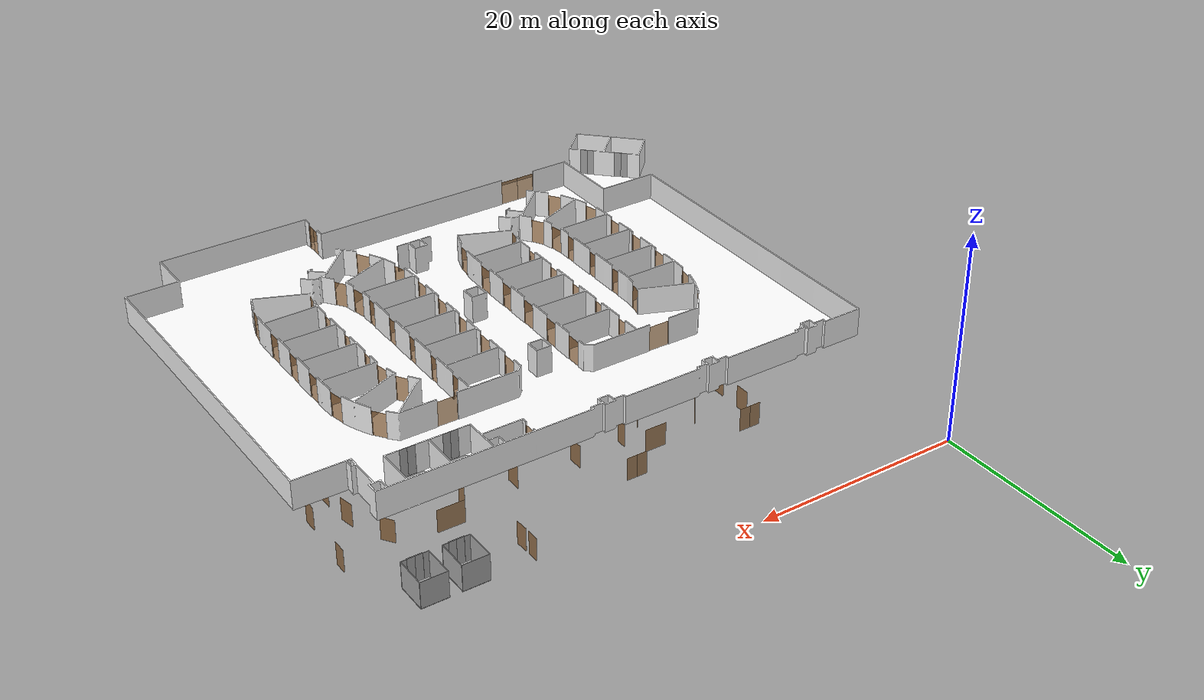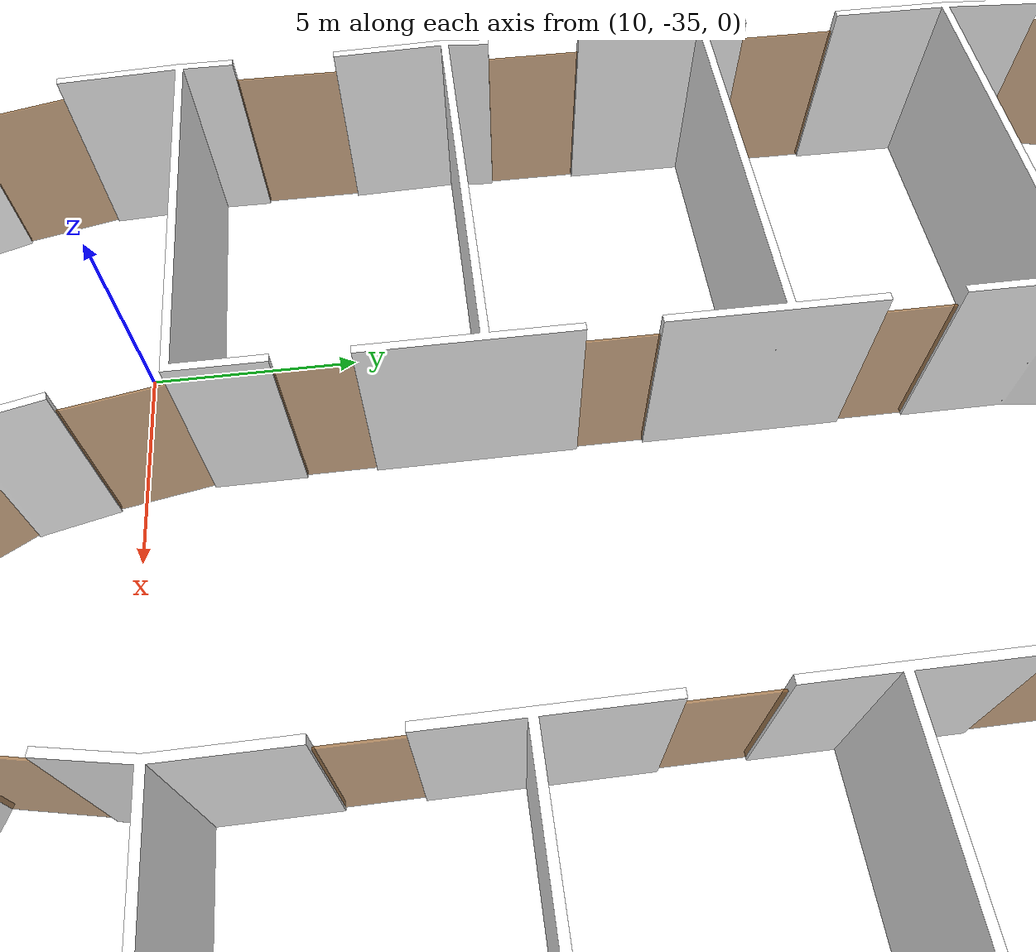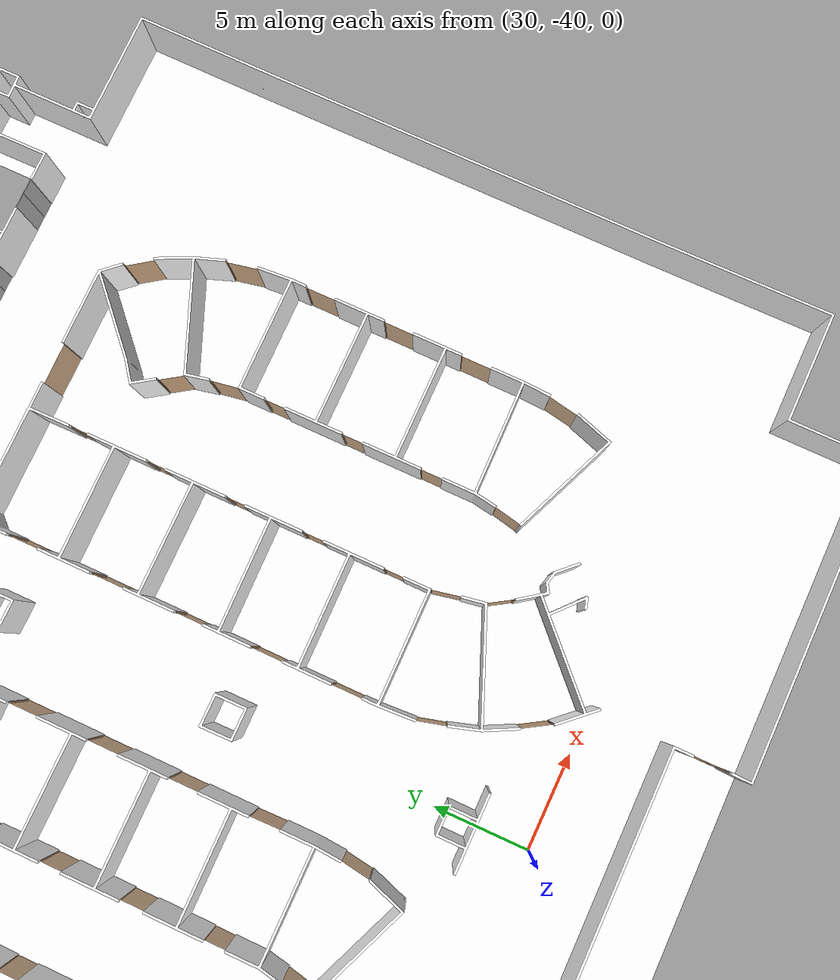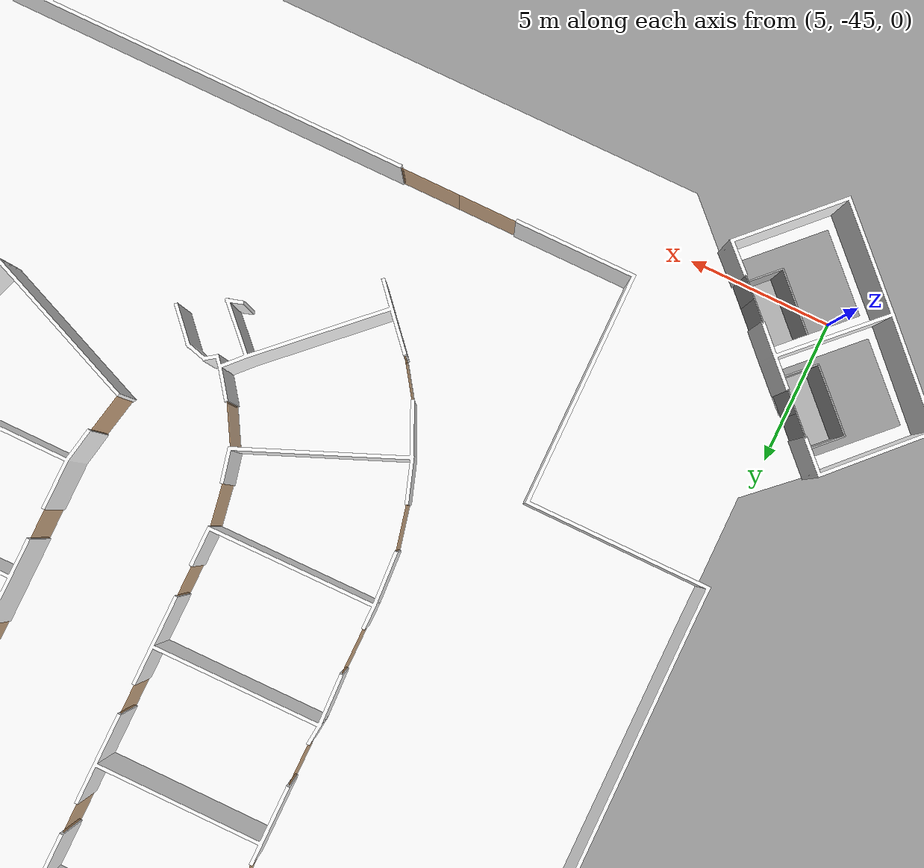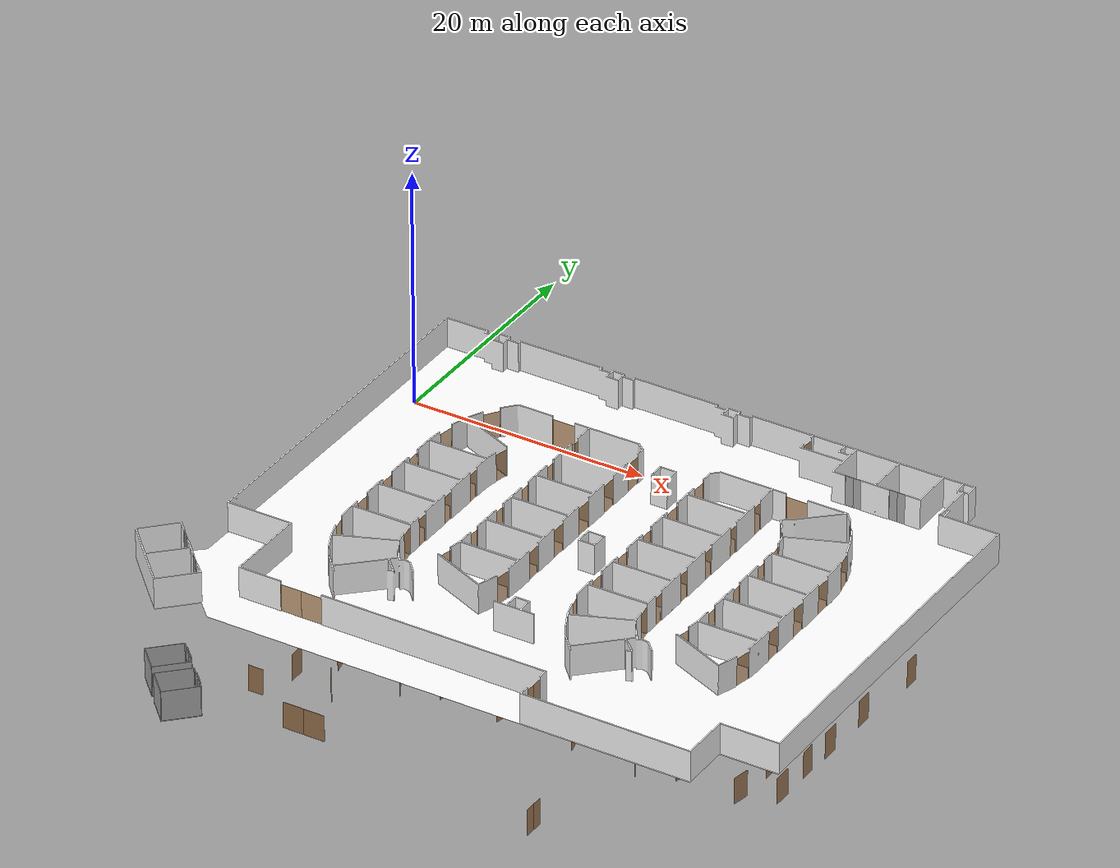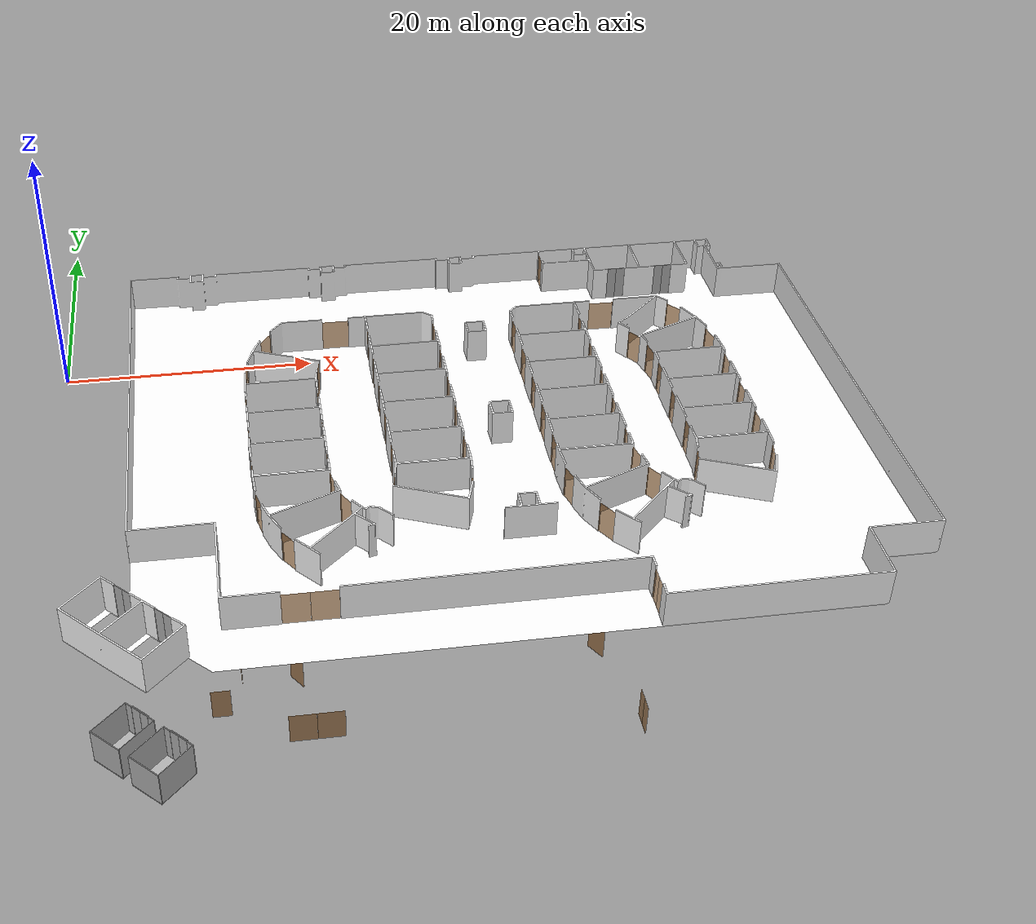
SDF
<sdf version="1.7">
 <world name="sim_world">
  <physics name="10ms" type="ode">
   <max_step_size>0.01</max_step_size>
   <real_time_factor>1.0</real_time_factor>
  </physics>
  <plugin filename="libignition-gazebo-physics-system.so" name="ignition::gazebo::systems::Physics"/>
  <plugin filename="libignition-gazebo-user-commands-system.so" name="ignition::gazebo::systems::UserCommands"/>
  <plugin filename="libignition-gazebo-scene-broadcaster-system.so" name="ignition::gazebo::systems::SceneBroadcaster"/>
  <scene><ambient>1 1 1</ambient><background>0.8 0.8 0.8</background><grid>false</grid></scene>
  <light type="directional" name="sun">
   <pose>0 0 10 0 0 0</pose>
   <diffuse>1 1 1 1</diffuse>
   <specular>0.2 0.2 0.2 1</specular>
   <attenuation>
    <range>1000</range>
    <constant>0.09</constant>
    <linear>0.001</linear>
    <quadratic>0.001</quadratic>
   </attenuation>
   <direction>-0.5 0.1 -0.9</direction>
  </light>
  <model name="L1_clinic_a">
   <pose>17.010597669320425 -41.768955040190804 0.0 0 0 3.141592653589793</pose>
   <link name="right">
    <pose>0.8791594554055622 0 1.11 0 0 0</pose>
    <visual name="right_visual">
     <geometry><box><size>1.7483189108111243 0.03 2.2</size></box></geometry>
     <material>
      <ambient>0.5 0.25 0 0.6</ambient>
      <diffuse>0.5 0.25 0 0.6</diffuse>
      <pbr><metal><metalness>0.0</metalness></metal></pbr>
     </material>
    </visual>
    <collision name="right_collision">
     <geometry><box><size>1.7483189108111243 0.03 2.2</size></box></geometry>
     <surface><contact><collide_bitmask>0x02</collide_bitmask></contact></surface>
    </collision>
    <inertial>
     <mass>50.0</mass>
     <inertia><ixx>20.17041666666667</ixx><iyy>32.90257922458249</iyy><izz>12.739662557915818</izz></inertia>
    </inertial>
   </link>
   <joint name="right_joint" type="prismatic">
    <parent>world</parent>
    <child>right</child>
    <axis>
     <xyz>1 0 0</xyz>
     <limit><lower>0.0</lower><upper>1.7583189108111243</upper><effort>500.0</effort></limit>
    </axis>
   </joint>
   <link name="left">
    <pose>-0.8791594554055622 0 1.11 0 0 0</pose>
    <visual name="left_visual">
     <geometry><box><size>1.7483189108111243 0.03 2.2</size></box></geometry>
     <material>
      <ambient>0.5 0.25 0 0.6</ambient>
      <diffuse>0.5 0.25 0 0.6</diffuse>
      <pbr><metal><metalness>0.0</metalness></metal></pbr>
     </material>
    </visual>
    <collision name="left_collision">
     <geometry><box><size>1.7483189108111243 0.03 2.2</size></box></geometry>
     <surface><contact><collide_bitmask>0x02</collide_bitmask></contact></surface>
    </collision>
    <inertial>
     <mass>50.0</mass>
     <inertia><ixx>20.17041666666667</ixx><iyy>32.90257922458249</iyy><izz>12.739662557915818</izz></inertia>
    </inertial>
   </link>
   <joint name="left_joint" type="prismatic">
    <parent>world</parent>
    <child>left</child>
    <axis>
     <xyz>1 0 0</xyz>
     <limit><lower>-1.7583189108111243</lower><upper>0.0</upper><effort>500.0</effort></limit>
    </axis>
   </joint>
   <plugin name="door" filename="libdoor.so">
    <v_max_door>0.2</v_max_door>
    <a_max_door>0.2</a_max_door>
    <a_nom_door>0.08</a_nom_door>
    <dx_min_door>0.001</dx_min_door>
    <f_max_door>100.0</f_max_door>
    <door name="L1_clinic_a" type="DoubleSlidingDoor" left_joint_name="left_joint" right_joint_name="right_joint"/>
   </plugin>
  </model>
  <model name="L1_left_consult_rm_13_outer">
   <pose>16.03554863274491 -14.728456597823172 0.0 0 0 0.9593844290063241</pose>
   <static>true</static>
   <link name="right">
    <pose>0 0 1.11 0 0 0</pose>
    <visual name="right_visual">
     <geometry><box><size>1.4433538767392087 0.03 2.2</size></box></geometry>
     <material>
      <ambient>0.5 0.25 0 0.6</ambient>
      <diffuse>0.5 0.25 0 0.6</diffuse>
      <pbr><metal><metalness>0.0</metalness></metal></pbr>
     </material>
    </visual>
    <collision name="right_collision">
     <geometry><box><size>1.4433538767392087 0.03 2.2</size></box></geometry>
     <surface><contact><collide_bitmask>0x02</collide_bitmask></contact></surface>
    </collision>
    <inertial>
     <mass>50.0</mass>
     <inertia><ixx>20.17041666666667</ixx><iyy>28.8469600562421</iyy><izz>8.684043389575429</izz></inertia>
    </inertial>
   </link>
   <joint name="right_joint" type="prismatic">
    <parent>world</parent>
    <child>right</child>
    <axis>
     <xyz>1 0 0</xyz>
     <limit><lower>0.0</lower><upper>1.4533538767392087</upper><effort>500.0</effort></limit>
    </axis>
   </joint>
  </model>
  <model name="L1_left_consult_rm_12_outer">
   <pose>14.50538056228608 -18.5739740779201 0.0 0 0 1.402401946784635</pose>
   <static>true</static>
   <link name="right">
    <pose>0 0 1.11 0 0 0</pose>
    <visual name="right_visual">
     <geometry><box><size>1.3727291591386541 0.03 2.2</size></box></geometry>
     <material>
      <ambient>0.5 0.25 0 0.6</ambient>
      <diffuse>0.5 0.25 0 0.6</diffuse>
      <pbr><metal><metalness>0.0</metalness></metal></pbr>
     </material>
    </visual>
    <collision name="right_collision">
     <geometry><box><size>1.3727291591386541 0.03 2.2</size></box></geometry>
     <surface><contact><collide_bitmask>0x02</collide_bitmask></contact></surface>
    </collision>
    <inertial>
     <mass>50.0</mass>
     <inertia><ixx>20.17041666666667</ixx><iyy>28.018272268122992</iyy><izz>7.855355601456319</izz></inertia>
    </inertial>
   </link>
   <joint name="right_joint" type="prismatic">
    <parent>world</parent>
    <child>right</child>
    <axis>
     <xyz>1 0 0</xyz>
     <limit><lower>0.0</lower><upper>1.3827291591386541</upper><effort>500.0</effort></limit>
    </axis>
   </joint>
  </model>
  <model name="L1_left_consult_rm_5_outer">
   <pose>28.19374447136651 -28.726235529402743 0.0 0 0 1.5919811640751727</pose>
   <static>true</static>
   <link name="right">
    <pose>0 0 1.11 0 0 0</pose>
    <visual name="right_visual">
     <geometry><box><size>1.37402272615404 0.03 2.2</size></box></geometry>
     <material>
      <ambient>0.5 0.25 0 0.6</ambient>
      <diffuse>0.5 0.25 0 0.6</diffuse>
      <pbr><metal><metalness>0.0</metalness></metal></pbr>
     </material>
    </visual>
    <collision name="right_collision">
     <geometry><box><size>1.37402272615404 0.03 2.2</size></box></geometry>
     <surface><contact><collide_bitmask>0x02</collide_bitmask></contact></surface>
    </collision>
    <inertial>
     <mass>50.0</mass>
     <inertia><ixx>20.17041666666667</ixx><iyy>28.03307688328242</iyy><izz>7.870160216615751</izz></inertia>
    </inertial>
   </link>
   <joint name="right_joint" type="prismatic">
    <parent>world</parent>
    <child>right</child>
    <axis>
     <xyz>1 0 0</xyz>
     <limit><lower>0.0</lower><upper>1.38402272615404</upper><effort>500.0</effort></limit>
    </axis>
   </joint>
  </model>
  <model name="L1_left_consult_rm_4_outer">
   <pose>28.179085419791573 -25.272043382946833 0.0 0 0 1.5707963267948966</pose>
   <static>true</static>
   <link name="right">
    <pose>0 0 1.11 0 0 0</pose>
    <visual name="right_visual">
     <geometry><box><size>1.3399250028845076 0.03 2.2</size></box></geometry>
     <material>
      <ambient>0.5 0.25 0 0.6</ambient>
      <diffuse>0.5 0.25 0 0.6</diffuse>
      <pbr><metal><metalness>0.0</metalness></metal></pbr>
     </material>
    </visual>
    <collision name="right_collision">
     <geometry><box><size>1.3399250028845076 0.03 2.2</size></box></geometry>
     <surface><contact><collide_bitmask>0x02</collide_bitmask></contact></surface>
    </collision>
    <inertial>
     <mass>50.0</mass>
     <inertia><ixx>20.17041666666667</ixx><iyy>27.64749588897937</iyy><izz>7.484579222312698</izz></inertia>
    </inertial>
   </link>
   <joint name="right_joint" type="prismatic">
    <parent>world</parent>
    <child>right</child>
    <axis>
     <xyz>1 0 0</xyz>
     <limit><lower>0.0</lower><upper>1.3499250028845076</upper><effort>500.0</effort></limit>
    </axis>
   </joint>
  </model>
  <model name="L1_left_consult_rm_3_outer">
   <pose>28.179085419791573 -21.845877081650727 0.0 0 0 1.5707963267948966</pose>
   <static>true</static>
   <link name="right">
    <pose>0 0 1.11 0 0 0</pose>
    <visual name="right_visual">
     <geometry><box><size>1.4299792315680138 0.03 2.2</size></box></geometry>
     <material>
      <ambient>0.5 0.25 0 0.6</ambient>
      <diffuse>0.5 0.25 0 0.6</diffuse>
      <pbr><metal><metalness>0.0</metalness></metal></pbr>
     </material>
    </visual>
    <collision name="right_collision">
     <geometry><box><size>1.4299792315680138 0.03 2.2</size></box></geometry>
     <surface><contact><collide_bitmask>0x02</collide_bitmask></contact></surface>
    </collision>
    <inertial>
     <mass>50.0</mass>
     <inertia><ixx>20.17041666666667</ixx><iyy>28.686835844649366</iyy><izz>8.523919177982698</izz></inertia>
    </inertial>
   </link>
   <joint name="right_joint" type="prismatic">
    <parent>world</parent>
    <child>right</child>
    <axis>
     <xyz>1 0 0</xyz>
     <limit><lower>0.0</lower><upper>1.4399792315680138</upper><effort>500.0</effort></limit>
    </axis>
   </joint>
  </model>
  <model name="L1_left_consult_rm_2_outer">
   <pose>28.179085419791573 -18.38420060766895 0.0 0 0 1.5707963267948966</pose>
   <static>true</static>
   <link name="right">
    <pose>0 0 1.11 0 0 0</pose>
    <visual name="right_visual">
     <geometry><box><size>1.3918306988192783 0.03 2.2</size></box></geometry>
     <material>
      <ambient>0.5 0.25 0 0.6</ambient>
      <diffuse>0.5 0.25 0 0.6</diffuse>
      <pbr><metal><metalness>0.0</metalness></metal></pbr>
     </material>
    </visual>
    <collision name="right_collision">
     <geometry><box><size>1.3918306988192783 0.03 2.2</size></box></geometry>
     <surface><contact><collide_bitmask>0x02</collide_bitmask></contact></surface>
    </collision>
    <inertial>
     <mass>50.0</mass>
     <inertia><ixx>20.17041666666667</ixx><iyy>28.23830289239901</iyy><izz>8.075386225732336</izz></inertia>
    </inertial>
   </link>
   <joint name="right_joint" type="prismatic">
    <parent>world</parent>
    <child>right</child>
    <axis>
     <xyz>1 0 0</xyz>
     <limit><lower>0.0</lower><upper>1.4018306988192784</upper><effort>500.0</effort></limit>
    </axis>
   </joint>
  </model>
  <model name="L1_left_consult_rm_1_outer">
   <pose>28.179085419791573 -15.017895465559029 0.0 0 0 -1.5707963267948966</pose>
   <static>true</static>
   <link name="right">
    <pose>0 0 1.11 0 0 0</pose>
    <visual name="right_visual">
     <geometry><box><size>1.4871885696703975 0.03 2.2</size></box></geometry>
     <material>
      <ambient>0.5 0.25 0 0.6</ambient>
      <diffuse>0.5 0.25 0 0.6</diffuse>
      <pbr><metal><metalness>0.0</metalness></metal></pbr>
     </material>
    </visual>
    <collision name="right_collision">
     <geometry><box><size>1.4871885696703975 0.03 2.2</size></box></geometry>
     <surface><contact><collide_bitmask>0x02</collide_bitmask></contact></surface>
    </collision>
    <inertial>
     <mass>50.0</mass>
     <inertia><ixx>20.17041666666667</ixx><iyy>29.38220767399285</iyy><izz>9.219291007326179</izz></inertia>
    </inertial>
   </link>
   <joint name="right_joint" type="prismatic">
    <parent>world</parent>
    <child>right</child>
    <axis>
     <xyz>1 0 0</xyz>
     <limit><lower>0.0</lower><upper>1.4971885696703975</upper><effort>500.0</effort></limit>
    </axis>
   </joint>
  </model>
  <model name="L1_left_consult_rm_7_outer">
   <pose>16.104374831737253 -36.70911888004311 0.0 0 0 -0.9670545342019088</pose>
   <static>true</static>
   <link name="right">
    <pose>0 0 1.11 0 0 0</pose>
    <visual name="right_visual">
     <geometry><box><size>1.3074913466446625 0.03 2.2</size></box></geometry>
     <material>
      <ambient>0.5 0.25 0 0.6</ambient>
      <diffuse>0.5 0.25 0 0.6</diffuse>
      <pbr><metal><metalness>0.0</metalness></metal></pbr>
     </material>
    </visual>
    <collision name="right_collision">
     <geometry><box><size>1.3074913466446625 0.03 2.2</size></box></geometry>
     <surface><contact><collide_bitmask>0x02</collide_bitmask></contact></surface>
    </collision>
    <inertial>
     <mass>50.0</mass>
     <inertia><ixx>20.17041666666667</ixx><iyy>27.289723423127807</iyy><izz>7.1268067564611375</izz></inertia>
    </inertial>
   </link>
   <joint name="right_joint" type="prismatic">
    <parent>world</parent>
    <child>right</child>
    <axis>
     <xyz>1 0 0</xyz>
     <limit><lower>0.0</lower><upper>1.3174913466446625</upper><effort>500.0</effort></limit>
    </axis>
   </joint>
  </model>
  <model name="L1_left_consult_rm_8_outer">
   <pose>14.54766162839892 -33.0019806930503 0.0 0 0 -1.3439871844568383</pose>
   <static>true</static>
   <link name="right">
    <pose>0 0 1.11 0 0 0</pose>
    <visual name="right_visual">
     <geometry><box><size>1.3621445813119888 0.03 2.2</size></box></geometry>
     <material>
      <ambient>0.5 0.25 0 0.6</ambient>
      <diffuse>0.5 0.25 0 0.6</diffuse>
      <pbr><metal><metalness>0.0</metalness></metal></pbr>
     </material>
    </visual>
    <collision name="right_collision">
     <geometry><box><size>1.3621445813119888 0.03 2.2</size></box></geometry>
     <surface><contact><collide_bitmask>0x02</collide_bitmask></contact></surface>
    </collision>
    <inertial>
     <mass>50.0</mass>
     <inertia><ixx>20.17041666666667</ixx><iyy>27.897657751656727</iyy><izz>7.734741084990055</izz></inertia>
    </inertial>
   </link>
   <joint name="right_joint" type="prismatic">
    <parent>world</parent>
    <child>right</child>
    <axis>
     <xyz>1 0 0</xyz>
     <limit><lower>0.0</lower><upper>1.3721445813119888</upper><effort>500.0</effort></limit>
    </axis>
   </joint>
  </model>
  <model name="L1_left_consult_rm_9_outer">
   <pose>14.307718933887172 -29.486527441252285 0.0 0 0 -1.5707963267948966</pose>
   <static>true</static>
   <link name="right">
    <pose>0 0 1.11 0 0 0</pose>
    <visual name="right_visual">
     <geometry><box><size>1.401791854159457 0.03 2.2</size></box></geometry>
     <material>
      <ambient>0.5 0.25 0 0.6</ambient>
      <diffuse>0.5 0.25 0 0.6</diffuse>
      <pbr><metal><metalness>0.0</metalness></metal></pbr>
     </material>
    </visual>
    <collision name="right_collision">
     <geometry><box><size>1.401791854159457 0.03 2.2</size></box></geometry>
     <surface><contact><collide_bitmask>0x02</collide_bitmask></contact></surface>
    </collision>
    <inertial>
     <mass>50.0</mass>
     <inertia><ixx>20.17041666666667</ixx><iyy>28.354251676615874</iyy><izz>8.191335009949201</izz></inertia>
    </inertial>
   </link>
   <joint name="right_joint" type="prismatic">
    <parent>world</parent>
    <child>right</child>
    <axis>
     <xyz>1 0 0</xyz>
     <limit><lower>0.0</lower><upper>1.411791854159457</upper><effort>500.0</effort></limit>
    </axis>
   </joint>
  </model>
  <model name="L1_left_consult_rm_10_outer">
   <pose>14.307718933887172 -26.181039190800377 0.0 0 0 -1.5707963267948966</pose>
   <static>true</static>
   <link name="right">
    <pose>0 0 1.11 0 0 0</pose>
    <visual name="right_visual">
     <geometry><box><size>1.2997034729433474 0.03 2.2</size></box></geometry>
     <material>
      <ambient>0.5 0.25 0 0.6</ambient>
      <diffuse>0.5 0.25 0 0.6</diffuse>
      <pbr><metal><metalness>0.0</metalness></metal></pbr>
     </material>
    </visual>
    <collision name="right_collision">
     <geometry><box><size>1.2997034729433474 0.03 2.2</size></box></geometry>
     <surface><contact><collide_bitmask>0x02</collide_bitmask></contact></surface>
    </collision>
    <inertial>
     <mass>50.0</mass>
     <inertia><ixx>20.17041666666667</ixx><iyy>27.205121323254165</iyy><izz>7.0422046565874945</izz></inertia>
    </inertial>
   </link>
   <joint name="right_joint" type="prismatic">
    <parent>world</parent>
    <child>right</child>
    <axis>
     <xyz>1 0 0</xyz>
     <limit><lower>0.0</lower><upper>1.3097034729433474</upper><effort>500.0</effort></limit>
    </axis>
   </joint>
  </model>
  <model name="L1_left_consult_rm_11_outer">
   <pose>14.307718933887172 -22.673729856544 0.0 0 0 -1.5707963267948966</pose>
   <static>true</static>
   <link name="right">
    <pose>0 0 1.11 0 0 0</pose>
    <visual name="right_visual">
     <geometry><box><size>1.346359370793431 0.03 2.2</size></box></geometry>
     <material>
      <ambient>0.5 0.25 0 0.6</ambient>
      <diffuse>0.5 0.25 0 0.6</diffuse>
      <pbr><metal><metalness>0.0</metalness></metal></pbr>
     </material>
    </visual>
    <collision name="right_collision">
     <geometry><box><size>1.346359370793431 0.03 2.2</size></box></geometry>
     <surface><contact><collide_bitmask>0x02</collide_bitmask></contact></surface>
    </collision>
    <inertial>
     <mass>50.0</mass>
     <inertia><ixx>20.17041666666667</ixx><iyy>27.719514813847017</iyy><izz>7.556598147180346</izz></inertia>
    </inertial>
   </link>
   <joint name="right_joint" type="prismatic">
    <parent>world</parent>
    <child>right</child>
    <axis>
     <xyz>1 0 0</xyz>
     <limit><lower>0.0</lower><upper>1.356359370793431</upper><effort>500.0</effort></limit>
    </axis>
   </joint>
  </model>
  <model name="L1_right_consult_rm_7_outer">
   <pose>35.78721395330952 -36.69358486212072 0.0 0 0 -1.0202506486553387</pose>
   <static>true</static>
   <link name="right">
    <pose>0 0 1.11 0 0 0</pose>
    <visual name="right_visual">
     <geometry><box><size>1.393912657434285 0.03 2.2</size></box></geometry>
     <material>
      <ambient>0.5 0.25 0 0.6</ambient>
      <diffuse>0.5 0.25 0 0.6</diffuse>
      <pbr><metal><metalness>0.0</metalness></metal></pbr>
     </material>
    </visual>
    <collision name="right_collision">
     <geometry><box><size>1.393912657434285 0.03 2.2</size></box></geometry>
     <surface><contact><collide_bitmask>0x02</collide_bitmask></contact></surface>
    </collision>
    <inertial>
     <mass>50.0</mass>
     <inertia><ixx>20.17041666666667</ixx><iyy>28.262468735647968</iyy><izz>8.099552068981295</izz></inertia>
    </inertial>
   </link>
   <joint name="right_joint" type="prismatic">
    <parent>world</parent>
    <child>right</child>
    <axis>
     <xyz>1 0 0</xyz>
     <limit><lower>0.0</lower><upper>1.403912657434285</upper><effort>500.0</effort></limit>
    </axis>
   </joint>
  </model>
  <model name="L1_right_consult_rm_8_outer">
   <pose>34.22348755817087 -32.956038229298905 0.0 0 0 -1.312559988648813</pose>
   <static>true</static>
   <link name="right">
    <pose>0 0 1.11 0 0 0</pose>
    <visual name="right_visual">
     <geometry><box><size>1.2887902244220548 0.03 2.2</size></box></geometry>
     <material>
      <ambient>0.5 0.25 0 0.6</ambient>
      <diffuse>0.5 0.25 0 0.6</diffuse>
      <pbr><metal><metalness>0.0</metalness></metal></pbr>
     </material>
    </visual>
    <collision name="right_collision">
     <geometry><box><size>1.2887902244220548 0.03 2.2</size></box></geometry>
     <surface><contact><collide_bitmask>0x02</collide_bitmask></contact></surface>
    </collision>
    <inertial>
     <mass>50.0</mass>
     <inertia><ixx>20.17041666666667</ixx><iyy>27.087417677357717</iyy><izz>6.924501010691044</izz></inertia>
    </inertial>
   </link>
   <joint name="right_joint" type="prismatic">
    <parent>world</parent>
    <child>right</child>
    <axis>
     <xyz>1 0 0</xyz>
     <limit><lower>0.0</lower><upper>1.2987902244220548</upper><effort>500.0</effort></limit>
    </axis>
   </joint>
  </model>
  <model name="L1_right_consult_rm_9_outer">
   <pose>33.97311257259339 -29.467264720587693 0.0 0 0 -1.5707963267948966</pose>
   <static>true</static>
   <link name="right">
    <pose>0 0 1.11 0 0 0</pose>
    <visual name="right_visual">
     <geometry><box><size>1.376027460482289 0.03 2.2</size></box></geometry>
     <material>
      <ambient>0.5 0.25 0 0.6</ambient>
      <diffuse>0.5 0.25 0 0.6</diffuse>
      <pbr><metal><metalness>0.0</metalness></metal></pbr>
     </material>
    </visual>
    <collision name="right_collision">
     <geometry><box><size>1.376027460482289 0.03 2.2</size></box></geometry>
     <surface><contact><collide_bitmask>0x02</collide_bitmask></contact></surface>
    </collision>
    <inertial>
     <mass>50.0</mass>
     <inertia><ixx>20.17041666666667</ixx><iyy>28.056048216672245</iyy><izz>7.893131550005574</izz></inertia>
    </inertial>
   </link>
   <joint name="right_joint" type="prismatic">
    <parent>world</parent>
    <child>right</child>
    <axis>
     <xyz>1 0 0</xyz>
     <limit><lower>0.0</lower><upper>1.386027460482289</upper><effort>500.0</effort></limit>
    </axis>
   </joint>
  </model>
  <model name="L1_right_consult_rm_10_outer">
   <pose>33.97311257259339 -26.0495923233722 0.0 0 0 -1.5707963267948966</pose>
   <static>true</static>
   <link name="right">
    <pose>0 0 1.11 0 0 0</pose>
    <visual name="right_visual">
     <geometry><box><size>1.4352559516941648 0.03 2.2</size></box></geometry>
     <material>
      <ambient>0.5 0.25 0 0.6</ambient>
      <diffuse>0.5 0.25 0 0.6</diffuse>
      <pbr><metal><metalness>0.0</metalness></metal></pbr>
     </material>
    </visual>
    <collision name="right_collision">
     <geometry><box><size>1.4352559516941648 0.03 2.2</size></box></geometry>
     <surface><contact><collide_bitmask>0x02</collide_bitmask></contact></surface>
    </collision>
    <inertial>
     <mass>50.0</mass>
     <inertia><ixx>20.17041666666667</ixx><iyy>28.749831861973014</iyy><izz>8.586915195306345</izz></inertia>
    </inertial>
   </link>
   <joint name="right_joint" type="prismatic">
    <parent>world</parent>
    <child>right</child>
    <axis>
     <xyz>1 0 0</xyz>
     <limit><lower>0.0</lower><upper>1.4452559516941648</upper><effort>500.0</effort></limit>
    </axis>
   </joint>
  </model>
  <model name="L1_right_consult_rm_11_outer">
   <pose>33.97311257259339 -22.67927579708475 0.0 0 0 -1.5707963267948966</pose>
   <static>true</static>
   <link name="right">
    <pose>0 0 1.11 0 0 0</pose>
    <visual name="right_visual">
     <geometry><box><size>1.3049532710280383 0.03 2.2</size></box></geometry>
     <material>
      <ambient>0.5 0.25 0 0.6</ambient>
      <diffuse>0.5 0.25 0 0.6</diffuse>
      <pbr><metal><metalness>0.0</metalness></metal></pbr>
     </material>
    </visual>
    <collision name="right_collision">
     <geometry><box><size>1.3049532710280383 0.03 2.2</size></box></geometry>
     <surface><contact><collide_bitmask>0x02</collide_bitmask></contact></surface>
    </collision>
    <inertial>
     <mass>50.0</mass>
     <inertia><ixx>20.17041666666667</ixx><iyy>27.26209599819491</iyy><izz>7.099179331528236</izz></inertia>
    </inertial>
   </link>
   <joint name="right_joint" type="prismatic">
    <parent>world</parent>
    <child>right</child>
    <axis>
     <xyz>1 0 0</xyz>
     <limit><lower>0.0</lower><upper>1.3149532710280383</upper><effort>500.0</effort></limit>
    </axis>
   </joint>
  </model>
  <model name="L1_right_consult_rm_12_outer">
   <pose>33.97311257259339 -19.137196646282852 0.0 0 0 -1.5707963267948966</pose>
   <static>true</static>
   <link name="right">
    <pose>0 0 1.11 0 0 0</pose>
    <visual name="right_visual">
     <geometry><box><size>1.5655586323602984 0.03 2.2</size></box></geometry>
     <material>
      <ambient>0.5 0.25 0 0.6</ambient>
      <diffuse>0.5 0.25 0 0.6</diffuse>
      <pbr><metal><metalness>0.0</metalness></metal></pbr>
     </material>
    </visual>
    <collision name="right_collision">
     <geometry><box><size>1.5655586323602984 0.03 2.2</size></box></geometry>
     <surface><contact><collide_bitmask>0x02</collide_bitmask></contact></surface>
    </collision>
    <inertial>
     <mass>50.0</mass>
     <inertia><ixx>20.17041666666667</ixx><iyy>30.379057630657705</iyy><izz>10.216140963991034</izz></inertia>
    </inertial>
   </link>
   <joint name="right_joint" type="prismatic">
    <parent>world</parent>
    <child>right</child>
    <axis>
     <xyz>1 0 0</xyz>
     <limit><lower>0.0</lower><upper>1.5755586323602984</upper><effort>500.0</effort></limit>
    </axis>
   </joint>
  </model>
  <model name="L1_right_consult_rm_13_outer">
   <pose>33.97311257259339 -15.447046267451267 0.0 0 0 -1.5707963267948966</pose>
   <static>true</static>
   <link name="right">
    <pose>0 0 1.11 0 0 0</pose>
    <visual name="right_visual">
     <geometry><box><size>1.4589473481789168 0.03 2.2</size></box></geometry>
     <material>
      <ambient>0.5 0.25 0 0.6</ambient>
      <diffuse>0.5 0.25 0 0.6</diffuse>
      <pbr><metal><metalness>0.0</metalness></metal></pbr>
     </material>
    </visual>
    <collision name="right_collision">
     <geometry><box><size>1.4589473481789168 0.03 2.2</size></box></geometry>
     <surface><contact><collide_bitmask>0x02</collide_bitmask></contact></surface>
    </collision>
    <inertial>
     <mass>50.0</mass>
     <inertia><ixx>20.17041666666667</ixx><iyy>29.035530686492898</iyy><izz>8.872614019826223</izz></inertia>
    </inertial>
   </link>
   <joint name="right_joint" type="prismatic">
    <parent>world</parent>
    <child>right</child>
    <axis>
     <xyz>1 0 0</xyz>
     <limit><lower>0.0</lower><upper>1.4689473481789168</upper><effort>500.0</effort></limit>
    </axis>
   </joint>
  </model>
  <model name="L1_right_consult_rm_1_outer">
   <pose>46.068297373178 -14.530337294719446 0.0 0 0 2.1863116312176896</pose>
   <static>true</static>
   <link name="right">
    <pose>0 0 1.11 0 0 0</pose>
    <visual name="right_visual">
     <geometry><box><size>1.3227213939192073 0.03 2.2</size></box></geometry>
     <material>
      <ambient>0.5 0.25 0 0.6</ambient>
      <diffuse>0.5 0.25 0 0.6</diffuse>
      <pbr><metal><metalness>0.0</metalness></metal></pbr>
     </material>
    </visual>
    <collision name="right_collision">
     <geometry><box><size>1.3227213939192073 0.03 2.2</size></box></geometry>
     <surface><contact><collide_bitmask>0x02</collide_bitmask></contact></surface>
    </collision>
    <inertial>
     <mass>50.0</mass>
     <inertia><ixx>20.17041666666667</ixx><iyy>27.456632858048216</iyy><izz>7.293716191381544</izz></inertia>
    </inertial>
   </link>
   <joint name="right_joint" type="prismatic">
    <parent>world</parent>
    <child>right</child>
    <axis>
     <xyz>1 0 0</xyz>
     <limit><lower>0.0</lower><upper>1.3327213939192073</upper><effort>500.0</effort></limit>
    </axis>
   </joint>
  </model>
  <model name="L1_right_consult_rm_2_outer">
   <pose>47.68885619783859 -18.3893427175878 0.0 0 0 1.769259662102772</pose>
   <static>true</static>
   <link name="right">
    <pose>0 0 1.11 0 0 0</pose>
    <visual name="right_visual">
     <geometry><box><size>1.409133850260675 0.03 2.2</size></box></geometry>
     <material>
      <ambient>0.5 0.25 0 0.6</ambient>
      <diffuse>0.5 0.25 0 0.6</diffuse>
      <pbr><metal><metalness>0.0</metalness></metal></pbr>
     </material>
    </visual>
    <collision name="right_collision">
     <geometry><box><size>1.409133850260675 0.03 2.2</size></box></geometry>
     <surface><contact><collide_bitmask>0x02</collide_bitmask></contact></surface>
    </collision>
    <inertial>
     <mass>50.0</mass>
     <inertia><ixx>20.17041666666667</ixx><iyy>28.440242533126984</iyy><izz>8.277325866460309</izz></inertia>
    </inertial>
   </link>
   <joint name="right_joint" type="prismatic">
    <parent>world</parent>
    <child>right</child>
    <axis>
     <xyz>1 0 0</xyz>
     <limit><lower>0.0</lower><upper>1.419133850260675</upper><effort>500.0</effort></limit>
    </axis>
   </joint>
  </model>
  <model name="L1_right_consult_rm_3_outer">
   <pose>47.92979500788435 -21.793661782239163 0.0 0 0 1.5707963267948966</pose>
   <static>true</static>
   <link name="right">
    <pose>0 0 1.11 0 0 0</pose>
    <visual name="right_visual">
     <geometry><box><size>1.3657163186031285 0.03 2.2</size></box></geometry>
     <material>
      <ambient>0.5 0.25 0 0.6</ambient>
      <diffuse>0.5 0.25 0 0.6</diffuse>
      <pbr><metal><metalness>0.0</metalness></metal></pbr>
     </material>
    </visual>
    <collision name="right_collision">
     <geometry><box><size>1.3657163186031285 0.03 2.2</size></box></geometry>
     <surface><contact><collide_bitmask>0x02</collide_bitmask></contact></surface>
    </collision>
    <inertial>
     <mass>50.0</mass>
     <inertia><ixx>20.17041666666667</ixx><iyy>27.938254428745346</iyy><izz>7.775337762078674</izz></inertia>
    </inertial>
   </link>
   <joint name="right_joint" type="prismatic">
    <parent>world</parent>
    <child>right</child>
    <axis>
     <xyz>1 0 0</xyz>
     <limit><lower>0.0</lower><upper>1.3757163186031285</upper><effort>500.0</effort></limit>
    </axis>
   </joint>
  </model>
  <model name="L1_right_consult_rm_4_outer">
   <pose>47.92979500788435 -25.260170762662995 0.0 0 0 1.5707963267948966</pose>
   <static>true</static>
   <link name="right">
    <pose>0 0 1.11 0 0 0</pose>
    <visual name="right_visual">
     <geometry><box><size>1.3501553786392877 0.03 2.2</size></box></geometry>
     <material>
      <ambient>0.5 0.25 0 0.6</ambient>
      <diffuse>0.5 0.25 0 0.6</diffuse>
      <pbr><metal><metalness>0.0</metalness></metal></pbr>
     </material>
    </visual>
    <collision name="right_collision">
     <geometry><box><size>1.3501553786392877 0.03 2.2</size></box></geometry>
     <surface><contact><collide_bitmask>0x02</collide_bitmask></contact></surface>
    </collision>
    <inertial>
     <mass>50.0</mass>
     <inertia><ixx>20.17041666666667</ixx><iyy>27.762164776952496</iyy><izz>7.599248110285827</izz></inertia>
    </inertial>
   </link>
   <joint name="right_joint" type="prismatic">
    <parent>world</parent>
    <child>right</child>
    <axis>
     <xyz>1 0 0</xyz>
     <limit><lower>0.0</lower><upper>1.3601553786392877</upper><effort>500.0</effort></limit>
    </axis>
   </joint>
  </model>
  <model name="L1_right_consult_rm_5_outer">
   <pose>47.92979500788435 -28.691694550209633 0.0 0 0 1.5707963267948966</pose>
   <static>true</static>
   <link name="right">
    <pose>0 0 1.11 0 0 0</pose>
    <visual name="right_visual">
     <geometry><box><size>1.3734967885850524 0.03 2.2</size></box></geometry>
     <material>
      <ambient>0.5 0.25 0 0.6</ambient>
      <diffuse>0.5 0.25 0 0.6</diffuse>
      <pbr><metal><metalness>0.0</metalness></metal></pbr>
     </material>
    </visual>
    <collision name="right_collision">
     <geometry><box><size>1.3734967885850524 0.03 2.2</size></box></geometry>
     <surface><contact><collide_bitmask>0x02</collide_bitmask></contact></surface>
    </collision>
    <inertial>
     <mass>50.0</mass>
     <inertia><ixx>20.17041666666667</ixx><iyy>28.027055951056056</iyy><izz>7.864139284389385</izz></inertia>
    </inertial>
   </link>
   <joint name="right_joint" type="prismatic">
    <parent>world</parent>
    <child>right</child>
    <axis>
     <xyz>1 0 0</xyz>
     <limit><lower>0.0</lower><upper>1.3834967885850524</upper><effort>500.0</effort></limit>
    </axis>
   </joint>
  </model>
  <model name="L1_right_consult_rm_6_outer">
   <pose>47.7432521826084 -32.589575400946146 0.0 0 0 1.3919487051964479</pose>
   <static>true</static>
   <link name="right">
    <pose>0 0 1.11 0 0 0</pose>
    <visual name="right_visual">
     <geometry><box><size>1.3880429351730292 0.03 2.2</size></box></geometry>
     <material>
      <ambient>0.5 0.25 0 0.6</ambient>
      <diffuse>0.5 0.25 0 0.6</diffuse>
      <pbr><metal><metalness>0.0</metalness></metal></pbr>
     </material>
    </visual>
    <collision name="right_collision">
     <geometry><box><size>1.3880429351730292 0.03 2.2</size></box></geometry>
     <surface><contact><collide_bitmask>0x02</collide_bitmask></contact></surface>
    </collision>
    <inertial>
     <mass>50.0</mass>
     <inertia><ixx>20.17041666666667</ixx><iyy>28.194429957848996</iyy><izz>8.031513291182327</izz></inertia>
    </inertial>
   </link>
   <joint name="right_joint" type="prismatic">
    <parent>world</parent>
    <child>right</child>
    <axis>
     <xyz>1 0 0</xyz>
     <limit><lower>0.0</lower><upper>1.3980429351730292</upper><effort>500.0</effort></limit>
    </axis>
   </joint>
  </model>
  <model name="L1_clinic_b">
   <pose>37.230733433329526 -43.36706088227379 0.0 0 0 1.5707963267948966</pose>
   <link name="right">
    <pose>0.41352928733510375 0 1.11 0 0 0</pose>
    <visual name="right_visual">
     <geometry><box><size>0.8170585746702075 0.03 2.2</size></box></geometry>
     <material>
      <ambient>0.5 0.25 0 0.6</ambient>
      <diffuse>0.5 0.25 0 0.6</diffuse>
      <pbr><metal><metalness>0.0</metalness></metal></pbr>
     </material>
    </visual>
    <collision name="right_collision">
     <geometry><box><size>0.8170585746702075 0.03 2.2</size></box></geometry>
     <surface><contact><collide_bitmask>0x02</collide_bitmask></contact></surface>
    </collision>
    <inertial>
     <mass>50.0</mass>
     <inertia><ixx>20.17041666666667</ixx><iyy>22.9482696435088</iyy><izz>2.7853529768421295</izz></inertia>
    </inertial>
   </link>
   <joint name="right_joint" type="prismatic">
    <parent>world</parent>
    <child>right</child>
    <axis>
     <xyz>1 0 0</xyz>
     <limit><lower>0.0</lower><upper>0.8270585746702075</upper><effort>500.0</effort></limit>
    </axis>
   </joint>
   <link name="left">
    <pose>-0.41352928733510375 0 1.11 0 0 0</pose>
    <visual name="left_visual">
     <geometry><box><size>0.8170585746702075 0.03 2.2</size></box></geometry>
     <material>
      <ambient>0.5 0.25 0 0.6</ambient>
      <diffuse>0.5 0.25 0 0.6</diffuse>
      <pbr><metal><metalness>0.0</metalness></metal></pbr>
     </material>
    </visual>
    <collision name="left_collision">
     <geometry><box><size>0.8170585746702075 0.03 2.2</size></box></geometry>
     <surface><contact><collide_bitmask>0x02</collide_bitmask></contact></surface>
    </collision>
    <inertial>
     <mass>50.0</mass>
     <inertia><ixx>20.17041666666667</ixx><iyy>22.9482696435088</iyy><izz>2.7853529768421295</izz></inertia>
    </inertial>
   </link>
   <joint name="left_joint" type="prismatic">
    <parent>world</parent>
    <child>left</child>
    <axis>
     <xyz>1 0 0</xyz>
     <limit><lower>-0.8270585746702075</lower><upper>0.0</upper><effort>500.0</effort></limit>
    </axis>
   </joint>
   <plugin name="door" filename="libdoor.so">
    <v_max_door>0.2</v_max_door>
    <a_max_door>0.2</a_max_door>
    <a_nom_door>0.08</a_nom_door>
    <dx_min_door>0.001</dx_min_door>
    <f_max_door>100.0</f_max_door>
    <door name="L1_clinic_b" type="DoubleSlidingDoor" left_joint_name="left_joint" right_joint_name="right_joint"/>
   </plugin>
  </model>
  <model name="L1_left_consult_rm_6_outer">
   <pose>28.03191608015079 -32.60593054113306 0.0 0 0 1.424311827427732</pose>
   <static>true</static>
   <link name="right">
    <pose>0 0 1.11 0 0 0</pose>
    <visual name="right_visual">
     <geometry><box><size>1.350293476713609 0.03 2.2</size></box></geometry>
     <material>
      <ambient>0.5 0.25 0 0.6</ambient>
      <diffuse>0.5 0.25 0 0.6</diffuse>
      <pbr><metal><metalness>0.0</metalness></metal></pbr>
     </material>
    </visual>
    <collision name="right_collision">
     <geometry><box><size>1.350293476713609 0.03 2.2</size></box></geometry>
     <surface><contact><collide_bitmask>0x02</collide_bitmask></contact></surface>
    </collision>
    <inertial>
     <mass>50.0</mass>
     <inertia><ixx>20.17041666666667</ixx><iyy>27.763718638563862</iyy><izz>7.600801971897191</izz></inertia>
    </inertial>
   </link>
   <joint name="right_joint" type="prismatic">
    <parent>world</parent>
    <child>right</child>
    <axis>
     <xyz>1 0 0</xyz>
     <limit><lower>0.0</lower><upper>1.360293476713609</upper><effort>500.0</effort></limit>
    </axis>
   </joint>
  </model>
  <model name="L1_left_treatment_1">
   <pose>11.806230529595025 -13.583354486365922 0.0 0 0 1.5707963267948966</pose>
   <link name="right">
    <pose>0 0 1.11 0 0 0</pose>
    <visual name="right_visual">
     <geometry><box><size>1.418106611284182 0.03 2.2</size></box></geometry>
     <material>
      <ambient>0.5 0.25 0 0.6</ambient>
      <diffuse>0.5 0.25 0 0.6</diffuse>
      <pbr><metal><metalness>0.0</metalness></metal></pbr>
     </material>
    </visual>
    <collision name="right_collision">
     <geometry><box><size>1.418106611284182 0.03 2.2</size></box></geometry>
     <surface><contact><collide_bitmask>0x02</collide_bitmask></contact></surface>
    </collision>
    <inertial>
     <mass>50.0</mass>
     <inertia><ixx>20.17041666666667</ixx><iyy>28.545943170699616</iyy><izz>8.383026504032943</izz></inertia>
    </inertial>
   </link>
   <joint name="right_joint" type="prismatic">
    <parent>world</parent>
    <child>right</child>
    <axis>
     <xyz>1 0 0</xyz>
     <limit><lower>0.0</lower><upper>1.428106611284182</upper><effort>500.0</effort></limit>
    </axis>
   </joint>
   <plugin name="door" filename="libdoor.so">
    <v_max_door>0.2</v_max_door>
    <a_max_door>0.2</a_max_door>
    <a_nom_door>0.08</a_nom_door>
    <dx_min_door>0.001</dx_min_door>
    <f_max_door>100.0</f_max_door>
    <door name="L1_left_treatment_1" type="SlidingDoor" left_joint_name="empty_joint" right_joint_name="right_joint"/>
   </plugin>
  </model>
  <model name="L1_left_negative_air_pressure">
   <pose>11.837715857082431 -26.84586554363296 0.0 0 0 -1.5791183096276138</pose>
   <link name="right">
    <pose>0 0 1.11 0 0 0</pose>
    <visual name="right_visual">
     <geometry><box><size>1.5784285274029304 0.03 2.2</size></box></geometry>
     <material>
      <ambient>0.5 0.25 0 0.6</ambient>
      <diffuse>0.5 0.25 0 0.6</diffuse>
      <pbr><metal><metalness>0.0</metalness></metal></pbr>
     </material>
    </visual>
    <collision name="right_collision">
     <geometry><box><size>1.5784285274029304 0.03 2.2</size></box></geometry>
     <surface><contact><collide_bitmask>0x02</collide_bitmask></contact></surface>
    </collision>
    <inertial>
     <mass>50.0</mass>
     <inertia><ixx>20.17041666666667</ixx><iyy>30.547652567164103</iyy><izz>10.384735900497432</izz></inertia>
    </inertial>
   </link>
   <joint name="right_joint" type="prismatic">
    <parent>world</parent>
    <child>right</child>
    <axis>
     <xyz>1 0 0</xyz>
     <limit><lower>0.0</lower><upper>1.5884285274029304</upper><effort>500.0</effort></limit>
    </axis>
   </joint>
   <plugin name="door" filename="libdoor.so">
    <v_max_door>0.2</v_max_door>
    <a_max_door>0.2</a_max_door>
    <a_nom_door>0.08</a_nom_door>
    <dx_min_door>0.001</dx_min_door>
    <f_max_door>100.0</f_max_door>
    <door name="L1_left_negative_air_pressure" type="SlidingDoor" left_joint_name="empty_joint" right_joint_name="right_joint"/>
   </plugin>
  </model>
  <model name="L1_left_treatment_2">
   <pose>11.806230529595025 -16.992142609899634 0.0 0 0 -1.5707963267948966</pose>
   <static>true</static>
   <link name="right">
    <pose>0 0 1.11 0 0 0</pose>
    <visual name="right_visual">
     <geometry><box><size>1.5319868466597464 0.03 2.2</size></box></geometry>
     <material>
      <ambient>0.5 0.25 0 0.6</ambient>
      <diffuse>0.5 0.25 0 0.6</diffuse>
      <pbr><metal><metalness>0.0</metalness></metal></pbr>
     </material>
    </visual>
    <collision name="right_collision">
     <geometry><box><size>1.5319868466597464 0.03 2.2</size></box></geometry>
     <surface><contact><collide_bitmask>0x02</collide_bitmask></contact></surface>
    </collision>
    <inertial>
     <mass>50.0</mass>
     <inertia><ixx>20.17041666666667</ixx><iyy>29.945765409743643</iyy><izz>9.782848743076972</izz></inertia>
    </inertial>
   </link>
   <joint name="right_joint" type="prismatic">
    <parent>world</parent>
    <child>right</child>
    <axis>
     <xyz>1 0 0</xyz>
     <limit><lower>0.0</lower><upper>1.5419868466597464</upper><effort>500.0</effort></limit>
    </axis>
   </joint>
  </model>
  <model name="L1_left_counsel_1">
   <pose>11.806230529595025 -20.376902811430348 0.0 0 0 1.5707963267948966</pose>
   <static>true</static>
   <link name="right">
    <pose>0 0 1.11 0 0 0</pose>
    <visual name="right_visual">
     <geometry><box><size>1.4607242029152745 0.03 2.2</size></box></geometry>
     <material>
      <ambient>0.5 0.25 0 0.6</ambient>
      <diffuse>0.5 0.25 0 0.6</diffuse>
      <pbr><metal><metalness>0.0</metalness></metal></pbr>
     </material>
    </visual>
    <collision name="right_collision">
     <geometry><box><size>1.4607242029152745 0.03 2.2</size></box></geometry>
     <surface><contact><collide_bitmask>0x02</collide_bitmask></contact></surface>
    </collision>
    <inertial>
     <mass>50.0</mass>
     <inertia><ixx>20.17041666666667</ixx><iyy>29.057146654093604</iyy><izz>8.894229987426936</izz></inertia>
    </inertial>
   </link>
   <joint name="right_joint" type="prismatic">
    <parent>world</parent>
    <child>right</child>
    <axis>
     <xyz>1 0 0</xyz>
     <limit><lower>0.0</lower><upper>1.4707242029152745</upper><effort>500.0</effort></limit>
    </axis>
   </joint>
  </model>
  <model name="L1_left_counsel_4">
   <pose>11.84769047344334 -23.23487942771434 0.0 0 0 -1.5707963267948966</pose>
   <static>true</static>
   <link name="right">
    <pose>0 0 1.11 0 0 0</pose>
    <visual name="right_visual">
     <geometry><box><size>1.465758624668284 0.03 2.2</size></box></geometry>
     <material>
      <ambient>0.5 0.25 0 0.6</ambient>
      <diffuse>0.5 0.25 0 0.6</diffuse>
      <pbr><metal><metalness>0.0</metalness></metal></pbr>
     </material>
    </visual>
    <collision name="right_collision">
     <geometry><box><size>1.465758624668284 0.03 2.2</size></box></geometry>
     <surface><contact><collide_bitmask>0x02</collide_bitmask></contact></surface>
    </collision>
    <inertial>
     <mass>50.0</mass>
     <inertia><ixx>20.17041666666667</ixx><iyy>29.118534774122757</iyy><izz>8.955618107456084</izz></inertia>
    </inertial>
   </link>
   <joint name="right_joint" type="prismatic">
    <parent>world</parent>
    <child>right</child>
    <axis>
     <xyz>1 0 0</xyz>
     <limit><lower>0.0</lower><upper>1.4757586246682841</upper><effort>500.0</effort></limit>
    </axis>
   </joint>
  </model>
  <model name="L1_left_counsel_3">
   <pose>9.016407061266882 -22.377170108841987 0.0 0 0 -1.5707963267948966</pose>
   <static>true</static>
   <link name="right">
    <pose>0 0 1.11 0 0 0</pose>
    <visual name="right_visual">
     <geometry><box><size>1.1436094765585965 0.03 2.2</size></box></geometry>
     <material>
      <ambient>0.5 0.25 0 0.6</ambient>
      <diffuse>0.5 0.25 0 0.6</diffuse>
      <pbr><metal><metalness>0.0</metalness></metal></pbr>
     </material>
    </visual>
    <collision name="right_collision">
     <geometry><box><size>1.1436094765585965 0.03 2.2</size></box></geometry>
     <surface><contact><collide_bitmask>0x02</collide_bitmask></contact></surface>
    </collision>
    <inertial>
     <mass>50.0</mass>
     <inertia><ixx>20.17041666666667</ixx><iyy>25.616010978644287</iyy><izz>5.453094311977613</izz></inertia>
    </inertial>
   </link>
   <joint name="right_joint" type="prismatic">
    <parent>world</parent>
    <child>right</child>
    <axis>
     <xyz>1 0 0</xyz>
     <limit><lower>0.0</lower><upper>1.1536094765585965</upper><effort>500.0</effort></limit>
    </axis>
   </joint>
  </model>
  <model name="L1_left_counsel_2">
   <pose>9.016407061266882 -21.218930041152284 0.0 0 0 1.5707963267948966</pose>
   <static>true</static>
   <link name="right">
    <pose>0 0 1.11 0 0 0</pose>
    <visual name="right_visual">
     <geometry><box><size>1.1528706588208146 0.03 2.2</size></box></geometry>
     <material>
      <ambient>0.5 0.25 0 0.6</ambient>
      <diffuse>0.5 0.25 0 0.6</diffuse>
      <pbr><metal><metalness>0.0</metalness></metal></pbr>
     </material>
    </visual>
    <collision name="right_collision">
     <geometry><box><size>1.1528706588208146 0.03 2.2</size></box></geometry>
     <surface><contact><collide_bitmask>0x02</collide_bitmask></contact></surface>
    </collision>
    <inertial>
     <mass>50.0</mass>
     <inertia><ixx>20.17041666666667</ixx><iyy>25.70462814987475</iyy><izz>5.541711483208079</izz></inertia>
    </inertial>
   </link>
   <joint name="right_joint" type="prismatic">
    <parent>world</parent>
    <child>right</child>
    <axis>
     <xyz>1 0 0</xyz>
     <limit><lower>0.0</lower><upper>1.1628706588208146</upper><effort>500.0</effort></limit>
    </axis>
   </joint>
  </model>
  <model name="L1_right_procedure">
   <pose>50.74072535671709 -13.553592169531953 0.0 0 0 1.5707963267948966</pose>
   <link name="right">
    <pose>0 0 1.11 0 0 0</pose>
    <visual name="right_visual">
     <geometry><box><size>1.2479862312987977 0.03 2.2</size></box></geometry>
     <material>
      <ambient>0.5 0.25 0 0.6</ambient>
      <diffuse>0.5 0.25 0 0.6</diffuse>
      <pbr><metal><metalness>0.0</metalness></metal></pbr>
     </material>
    </visual>
    <collision name="right_collision">
     <geometry><box><size>1.2479862312987977 0.03 2.2</size></box></geometry>
     <surface><contact><collide_bitmask>0x02</collide_bitmask></contact></surface>
    </collision>
    <inertial>
     <mass>50.0</mass>
     <inertia><ixx>20.17041666666667</ixx><iyy>26.656123472964072</iyy><izz>6.493206806297401</izz></inertia>
    </inertial>
   </link>
   <joint name="right_joint" type="prismatic">
    <parent>world</parent>
    <child>right</child>
    <axis>
     <xyz>1 0 0</xyz>
     <limit><lower>0.0</lower><upper>1.2579862312987977</upper><effort>500.0</effort></limit>
    </axis>
   </joint>
   <plugin name="door" filename="libdoor.so">
    <v_max_door>0.2</v_max_door>
    <a_max_door>0.2</a_max_door>
    <a_nom_door>0.08</a_nom_door>
    <dx_min_door>0.001</dx_min_door>
    <f_max_door>100.0</f_max_door>
    <door name="L1_right_procedure" type="SlidingDoor" left_joint_name="empty_joint" right_joint_name="right_joint"/>
   </plugin>
  </model>
  <model name="L1_right_treatment">
   <pose>50.29120803046041 -19.682408368908906 0.0 0 0 1.5707963267948966</pose>
   <link name="right">
    <pose>0 0 1.11 0 0 0</pose>
    <visual name="right_visual">
     <geometry><box><size>1.3636702434521746 0.03 2.2</size></box></geometry>
     <material>
      <ambient>0.5 0.25 0 0.6</ambient>
      <diffuse>0.5 0.25 0 0.6</diffuse>
      <pbr><metal><metalness>0.0</metalness></metal></pbr>
     </material>
    </visual>
    <collision name="right_collision">
     <geometry><box><size>1.3636702434521746 0.03 2.2</size></box></geometry>
     <surface><contact><collide_bitmask>0x02</collide_bitmask></contact></surface>
    </collision>
    <inertial>
     <mass>50.0</mass>
     <inertia><ixx>20.17041666666667</ixx><iyy>27.91498555365381</iyy><izz>7.7520688869871375</izz></inertia>
    </inertial>
   </link>
   <joint name="right_joint" type="prismatic">
    <parent>world</parent>
    <child>right</child>
    <axis>
     <xyz>1 0 0</xyz>
     <limit><lower>0.0</lower><upper>1.3736702434521746</upper><effort>500.0</effort></limit>
    </axis>
   </joint>
   <plugin name="door" filename="libdoor.so">
    <v_max_door>0.2</v_max_door>
    <a_max_door>0.2</a_max_door>
    <a_nom_door>0.08</a_nom_door>
    <dx_min_door>0.001</dx_min_door>
    <f_max_door>100.0</f_max_door>
    <door name="L1_right_treatment" type="SlidingDoor" left_joint_name="empty_joint" right_joint_name="right_joint"/>
   </plugin>
  </model>
  <model name="L1_right_counsel">
   <pose>50.26705895927084 -24.383629475789412 0.0 0 0 1.5707224510909026</pose>
   <static>true</static>
   <link name="right">
    <pose>0 0 1.11 0 0 0</pose>
    <visual name="right_visual">
     <geometry><box><size>1.4476939388264292 0.03 2.2</size></box></geometry>
     <material>
      <ambient>0.5 0.25 0 0.6</ambient>
      <diffuse>0.5 0.25 0 0.6</diffuse>
      <pbr><metal><metalness>0.0</metalness></metal></pbr>
     </material>
    </visual>
    <collision name="right_collision">
     <geometry><box><size>1.4476939388264292 0.03 2.2</size></box></geometry>
     <surface><contact><collide_bitmask>0x02</collide_bitmask></contact></surface>
    </collision>
    <inertial>
     <mass>50.0</mass>
     <inertia><ixx>20.17041666666667</ixx><iyy>28.89924058547826</iyy><izz>8.736323918811587</izz></inertia>
    </inertial>
   </link>
   <joint name="right_joint" type="prismatic">
    <parent>world</parent>
    <child>right</child>
    <axis>
     <xyz>1 0 0</xyz>
     <limit><lower>0.0</lower><upper>1.4576939388264292</upper><effort>500.0</effort></limit>
    </axis>
   </joint>
  </model>
  <model name="L1_right_consult">
   <pose>50.16296488596596 -27.391548401984565 0.0 0 0 1.6204880391072638</pose>
   <static>true</static>
   <link name="right">
    <pose>0 0 1.11 0 0 0</pose>
    <visual name="right_visual">
     <geometry><box><size>1.295688480855341 0.03 2.2</size></box></geometry>
     <material>
      <ambient>0.5 0.25 0 0.6</ambient>
      <diffuse>0.5 0.25 0 0.6</diffuse>
      <pbr><metal><metalness>0.0</metalness></metal></pbr>
     </material>
    </visual>
    <collision name="right_collision">
     <geometry><box><size>1.295688480855341 0.03 2.2</size></box></geometry>
     <surface><contact><collide_bitmask>0x02</collide_bitmask></contact></surface>
    </collision>
    <inertial>
     <mass>50.0</mass>
     <inertia><ixx>20.17041666666667</ixx><iyy>27.161702664255095</iyy><izz>6.998785997588423</izz></inertia>
    </inertial>
   </link>
   <joint name="right_joint" type="prismatic">
    <parent>world</parent>
    <child>right</child>
    <axis>
     <xyz>1 0 0</xyz>
     <limit><lower>0.0</lower><upper>1.305688480855341</upper><effort>500.0</effort></limit>
    </axis>
   </joint>
  </model>
  <model name="L1_right_negative_air_pressure">
   <pose>50.20365755163267 -30.98576208607364 0.0 0 0 1.5688743082939884</pose>
   <link name="right">
    <pose>0 0 1.11 0 0 0</pose>
    <visual name="right_visual">
     <geometry><box><size>1.558804097655797 0.03 2.2</size></box></geometry>
     <material>
      <ambient>0.5 0.25 0 0.6</ambient>
      <diffuse>0.5 0.25 0 0.6</diffuse>
      <pbr><metal><metalness>0.0</metalness></metal></pbr>
     </material>
    </visual>
    <collision name="right_collision">
     <geometry><box><size>1.558804097655797 0.03 2.2</size></box></geometry>
     <surface><contact><collide_bitmask>0x02</collide_bitmask></contact></surface>
    </collision>
    <inertial>
     <mass>50.0</mass>
     <inertia><ixx>20.17041666666667</ixx><iyy>30.291125895285436</iyy><izz>10.128209228618767</izz></inertia>
    </inertial>
   </link>
   <joint name="right_joint" type="prismatic">
    <parent>world</parent>
    <child>right</child>
    <axis>
     <xyz>1 0 0</xyz>
     <limit><lower>0.0</lower><upper>1.568804097655797</upper><effort>500.0</effort></limit>
    </axis>
   </joint>
   <plugin name="door" filename="libdoor.so">
    <v_max_door>0.2</v_max_door>
    <a_max_door>0.2</a_max_door>
    <a_nom_door>0.08</a_nom_door>
    <dx_min_door>0.001</dx_min_door>
    <f_max_door>100.0</f_max_door>
    <door name="L1_right_negative_air_pressure" type="SlidingDoor" left_joint_name="empty_joint" right_joint_name="right_joint"/>
   </plugin>
  </model>
  <model name="L1_existing_ahu">
   <pose>12.856634360216926 -11.116353217183963 0.0 0 0 -3.1406699672959486</pose>
   <static>true</static>
   <link name="right">
    <pose>0.5252021388763539 0 1.11 0 0 0</pose>
    <visual name="right_visual">
     <geometry><box><size>1.0404042777527078 0.03 2.2</size></box></geometry>
     <material>
      <ambient>0.5 0.25 0 0.6</ambient>
      <diffuse>0.5 0.25 0 0.6</diffuse>
      <pbr><metal><metalness>0.0</metalness></metal></pbr>
     </material>
    </visual>
    <collision name="right_collision">
     <geometry><box><size>1.0404042777527078 0.03 2.2</size></box></geometry>
     <surface><contact><collide_bitmask>0x02</collide_bitmask></contact></surface>
    </collision>
    <inertial>
     <mass>50.0</mass>
     <inertia><ixx>20.17041666666667</ixx><iyy>24.676837754858894</iyy><izz>4.513921088192224</izz></inertia>
    </inertial>
   </link>
   <joint name="right_joint" type="revolute">
    <parent>world</parent>
    <child>right</child>
    <axis><xyz>0 0 -1</xyz><limit><lower>0</lower><upper>1.57</upper></limit></axis>
    <pose>0.5252021388763539 0 0 0 0 0</pose>
   </joint>
   <link name="left">
    <pose>-0.5252021388763539 0 1.11 0 0 0</pose>
    <visual name="left_visual">
     <geometry><box><size>1.0404042777527078 0.03 2.2</size></box></geometry>
     <material>
      <ambient>0.5 0.25 0 0.6</ambient>
      <diffuse>0.5 0.25 0 0.6</diffuse>
      <pbr><metal><metalness>0.0</metalness></metal></pbr>
     </material>
    </visual>
    <collision name="left_collision">
     <geometry><box><size>1.0404042777527078 0.03 2.2</size></box></geometry>
     <surface><contact><collide_bitmask>0x02</collide_bitmask></contact></surface>
    </collision>
    <inertial>
     <mass>50.0</mass>
     <inertia><ixx>20.17041666666667</ixx><iyy>24.676837754858894</iyy><izz>4.513921088192224</izz></inertia>
    </inertial>
   </link>
   <joint name="left_joint" type="revolute">
    <parent>world</parent>
    <child>left</child>
    <axis><xyz>0 0 -1</xyz><limit><lower>-1.57</lower><upper>0</upper></limit></axis>
    <pose>-0.5252021388763539 0 0 0 0 0</pose>
   </joint>
  </model>
  <model name="L1_left_consult_rm_2_inner">
   <pose>23.381523787546655 -18.60085573631785 0.0 0 0 -1.5707963267948966</pose>
   <static>true</static>
   <link name="right">
    <pose>0 0 1.11 0 0 0</pose>
    <visual name="right_visual">
     <geometry><box><size>0.9945421329948851 0.03 2.2</size></box></geometry>
     <material>
      <ambient>0.5 0.25 0 0.6</ambient>
      <diffuse>0.5 0.25 0 0.6</diffuse>
      <pbr><metal><metalness>0.0</metalness></metal></pbr>
     </material>
    </visual>
    <collision name="right_collision">
     <geometry><box><size>0.9945421329948851 0.03 2.2</size></box></geometry>
     <surface><contact><collide_bitmask>0x02</collide_bitmask></contact></surface>
    </collision>
    <inertial>
     <mass>50.0</mass>
     <inertia><ixx>20.17041666666667</ixx><iyy>24.287975226258403</iyy><izz>4.125058559591733</izz></inertia>
    </inertial>
   </link>
   <joint name="right_joint" type="prismatic">
    <parent>world</parent>
    <child>right</child>
    <axis>
     <xyz>1 0 0</xyz>
     <limit><lower>0.0</lower><upper>1.0045421329948852</upper><effort>500.0</effort></limit>
    </axis>
   </joint>
  </model>
  <model name="L1_wc_1">
   <pose>11.200928810430376 -39.07548555824779 0.0 0 0 0.003911519091325118</pose>
   <static>true</static>
   <link name="right">
    <pose>0 0 1.11 0 0 0</pose>
    <visual name="right_visual">
     <geometry><box><size>1.2426652499551487 0.03 2.2</size></box></geometry>
     <material>
      <ambient>0.5 0.25 0 0.6</ambient>
      <diffuse>0.5 0.25 0 0.6</diffuse>
      <pbr><metal><metalness>0.0</metalness></metal></pbr>
     </material>
    </visual>
    <collision name="right_collision">
     <geometry><box><size>1.2426652499551487 0.03 2.2</size></box></geometry>
     <surface><contact><collide_bitmask>0x02</collide_bitmask></contact></surface>
    </collision>
    <inertial>
     <mass>50.0</mass>
     <inertia><ixx>20.17041666666667</ixx><iyy>26.600903847692056</iyy><izz>6.437987181025385</izz></inertia>
    </inertial>
   </link>
   <joint name="right_joint" type="revolute">
    <parent>world</parent>
    <child>right</child>
    <axis><xyz>0 0 1</xyz><limit><lower>0</lower><upper>1.57</upper></limit></axis>
    <pose>0.6263326249775744 0 0 0 0 0</pose>
   </joint>
  </model>
  <model name="L1_hr">
   <pose>12.55797469328104 -35.737919695396364 0.0 0 0 -1.5363800665340395</pose>
   <static>true</static>
   <link name="right">
    <pose>0 0 1.11 0 0 0</pose>
    <visual name="right_visual">
     <geometry><box><size>1.3419909622330712 0.03 2.2</size></box></geometry>
     <material>
      <ambient>0.5 0.25 0 0.6</ambient>
      <diffuse>0.5 0.25 0 0.6</diffuse>
      <pbr><metal><metalness>0.0</metalness></metal></pbr>
     </material>
    </visual>
    <collision name="right_collision">
     <geometry><box><size>1.3419909622330712 0.03 2.2</size></box></geometry>
     <surface><contact><collide_bitmask>0x02</collide_bitmask></contact></surface>
    </collision>
    <inertial>
     <mass>50.0</mass>
     <inertia><ixx>20.17041666666667</ixx><iyy>27.670582261313523</iyy><izz>7.507665594646852</izz></inertia>
    </inertial>
   </link>
   <joint name="right_joint" type="revolute">
    <parent>world</parent>
    <child>right</child>
    <axis><xyz>0 0 -1</xyz><limit><lower>0</lower><upper>1.57</upper></limit></axis>
    <pose>0.6759954811165356 0 0 0 0 0</pose>
   </joint>
  </model>
  <model name="L1_dis_wc_2">
   <pose>10.318841583016047 -32.594380985346746 0.0 0 0 -0.002698587139888158</pose>
   <static>true</static>
   <link name="right">
    <pose>0 0 1.11 0 0 0</pose>
    <visual name="right_visual">
     <geometry><box><size>1.4066429798800912 0.03 2.2</size></box></geometry>
     <material>
      <ambient>0.5 0.25 0 0.6</ambient>
      <diffuse>0.5 0.25 0 0.6</diffuse>
      <pbr><metal><metalness>0.0</metalness></metal></pbr>
     </material>
    </visual>
    <collision name="right_collision">
     <geometry><box><size>1.4066429798800912 0.03 2.2</size></box></geometry>
     <surface><contact><collide_bitmask>0x02</collide_bitmask></contact></surface>
    </collision>
    <inertial>
     <mass>50.0</mass>
     <inertia><ixx>20.17041666666667</ixx><iyy>28.4110186368581</iyy><izz>8.248101970191428</izz></inertia>
    </inertial>
   </link>
   <joint name="right_joint" type="prismatic">
    <parent>world</parent>
    <child>right</child>
    <axis>
     <xyz>1 0 0</xyz>
     <limit><lower>0.0</lower><upper>1.4166429798800912</upper><effort>500.0</effort></limit>
    </axis>
   </joint>
  </model>
  <model name="L1_dis_wc_1">
   <pose>8.551961463020662 -32.596292450290406 0.0 0 0 3.141592653589793</pose>
   <static>true</static>
   <link name="right">
    <pose>0 0 1.11 0 0 0</pose>
    <visual name="right_visual">
     <geometry><box><size>1.3391442636821675 0.03 2.2</size></box></geometry>
     <material>
      <ambient>0.5 0.25 0 0.6</ambient>
      <diffuse>0.5 0.25 0 0.6</diffuse>
      <pbr><metal><metalness>0.0</metalness></metal></pbr>
     </material>
    </visual>
    <collision name="right_collision">
     <geometry><box><size>1.3391442636821675 0.03 2.2</size></box></geometry>
     <surface><contact><collide_bitmask>0x02</collide_bitmask></contact></surface>
    </collision>
    <inertial>
     <mass>50.0</mass>
     <inertia><ixx>20.17041666666667</ixx><iyy>27.638780662303567</iyy><izz>7.475863995636895</izz></inertia>
    </inertial>
   </link>
   <joint name="right_joint" type="prismatic">
    <parent>world</parent>
    <child>right</child>
    <axis>
     <xyz>1 0 0</xyz>
     <limit><lower>0.0</lower><upper>1.3491442636821676</upper><effort>500.0</effort></limit>
    </axis>
   </joint>
  </model>
  <model name="L1_left_consult_rm_13_inner">
   <pose>20.473727933541035 -17.004284450598067 0.0 0 0 0.9869285289705991</pose>
   <static>true</static>
   <link name="right">
    <pose>0 0 1.11 0 0 0</pose>
    <visual name="right_visual">
     <geometry><box><size>1.2252035838140947 0.03 2.2</size></box></geometry>
     <material>
      <ambient>0.5 0.25 0 0.6</ambient>
      <diffuse>0.5 0.25 0 0.6</diffuse>
      <pbr><metal><metalness>0.0</metalness></metal></pbr>
     </material>
    </visual>
    <collision name="right_collision">
     <geometry><box><size>1.2252035838140947 0.03 2.2</size></box></geometry>
     <surface><contact><collide_bitmask>0x02</collide_bitmask></contact></surface>
    </collision>
    <inertial>
     <mass>50.0</mass>
     <inertia><ixx>20.17041666666667</ixx><iyy>26.421349257462094</iyy><izz>6.258432590795422</izz></inertia>
    </inertial>
   </link>
   <joint name="right_joint" type="revolute">
    <parent>world</parent>
    <child>right</child>
    <axis><xyz>0 0 -1</xyz><limit><lower>0</lower><upper>1.57</upper></limit></axis>
    <pose>0.6176017919070473 0 0 0 0 0</pose>
   </joint>
  </model>
  <model name="L1_left_consult_rm_12_inner">
   <pose>19.442438752355695 -18.948876966270543 0.0 0 0 1.3549047324942773</pose>
   <static>true</static>
   <link name="right">
    <pose>0 0 1.11 0 0 0</pose>
    <visual name="right_visual">
     <geometry><box><size>1.1707228872175774 0.03 2.2</size></box></geometry>
     <material>
      <ambient>0.5 0.25 0 0.6</ambient>
      <diffuse>0.5 0.25 0 0.6</diffuse>
      <pbr><metal><metalness>0.0</metalness></metal></pbr>
     </material>
    </visual>
    <collision name="right_collision">
     <geometry><box><size>1.1707228872175774 0.03 2.2</size></box></geometry>
     <surface><contact><collide_bitmask>0x02</collide_bitmask></contact></surface>
    </collision>
    <inertial>
     <mass>50.0</mass>
     <inertia><ixx>20.17041666666667</ixx><iyy>25.87746699439609</iyy><izz>5.714550327729419</izz></inertia>
    </inertial>
   </link>
   <joint name="right_joint" type="revolute">
    <parent>world</parent>
    <child>right</child>
    <axis><xyz>0 0 -1</xyz><limit><lower>0</lower><upper>1.57</upper></limit></axis>
    <pose>0.5903614436087887 0 0 0 0 0</pose>
   </joint>
  </model>
  <model name="L1_left_consult_rm_11_inner">
   <pose>19.167982000692298 -22.335117880081555 0.0 0 0 1.5707963267948966</pose>
   <static>true</static>
   <link name="right">
    <pose>0 0 1.11 0 0 0</pose>
    <visual name="right_visual">
     <geometry><box><size>0.960216530133456 0.03 2.2</size></box></geometry>
     <material>
      <ambient>0.5 0.25 0 0.6</ambient>
      <diffuse>0.5 0.25 0 0.6</diffuse>
      <pbr><metal><metalness>0.0</metalness></metal></pbr>
     </material>
    </visual>
    <collision name="right_collision">
     <geometry><box><size>0.960216530133456 0.03 2.2</size></box></geometry>
     <surface><contact><collide_bitmask>0x02</collide_bitmask></contact></surface>
    </collision>
    <inertial>
     <mass>50.0</mass>
     <inertia><ixx>20.17041666666667</ixx><iyy>24.00839910308973</iyy><izz>3.8454824364230595</izz></inertia>
    </inertial>
   </link>
   <joint name="right_joint" type="prismatic">
    <parent>world</parent>
    <child>right</child>
    <axis>
     <xyz>1 0 0</xyz>
     <limit><lower>0.0</lower><upper>0.970216530133456</upper><effort>500.0</effort></limit>
    </axis>
   </joint>
  </model>
  <model name="L1_left_consult_rm_10_inner">
   <pose>19.167982000692298 -25.7948963501404 0.0 0 0 1.5707963267948966</pose>
   <static>true</static>
   <link name="right">
    <pose>0 0 1.11 0 0 0</pose>
    <visual name="right_visual">
     <geometry><box><size>0.9495554017153205 0.03 2.2</size></box></geometry>
     <material>
      <ambient>0.5 0.25 0 0.6</ambient>
      <diffuse>0.5 0.25 0 0.6</diffuse>
      <pbr><metal><metalness>0.0</metalness></metal></pbr>
     </material>
    </visual>
    <collision name="right_collision">
     <geometry><box><size>0.9495554017153205 0.03 2.2</size></box></geometry>
     <surface><contact><collide_bitmask>0x02</collide_bitmask></contact></surface>
    </collision>
    <inertial>
     <mass>50.0</mass>
     <inertia><ixx>20.17041666666667</ixx><iyy>23.923564420528106</iyy><izz>3.760647753861432</izz></inertia>
    </inertial>
   </link>
   <joint name="right_joint" type="prismatic">
    <parent>world</parent>
    <child>right</child>
    <axis>
     <xyz>1 0 0</xyz>
     <limit><lower>0.0</lower><upper>0.9595554017153205</upper><effort>500.0</effort></limit>
    </axis>
   </joint>
  </model>
  <model name="L1_left_consult_rm_9_inner">
   <pose>19.167982000692298 -29.246678973885643 0.0 0 0 1.5707963267948966</pose>
   <static>true</static>
   <link name="right">
    <pose>0 0 1.11 0 0 0</pose>
    <visual name="right_visual">
     <geometry><box><size>0.9762082227606628 0.03 2.2</size></box></geometry>
     <material>
      <ambient>0.5 0.25 0 0.6</ambient>
      <diffuse>0.5 0.25 0 0.6</diffuse>
      <pbr><metal><metalness>0.0</metalness></metal></pbr>
     </material>
    </visual>
    <collision name="right_collision">
     <geometry><box><size>0.9762082227606628 0.03 2.2</size></box></geometry>
     <surface><contact><collide_bitmask>0x02</collide_bitmask></contact></surface>
    </collision>
    <inertial>
     <mass>50.0</mass>
     <inertia><ixx>20.17041666666667</ixx><iyy>24.13742705910639</iyy><izz>3.9745103924397163</izz></inertia>
    </inertial>
   </link>
   <joint name="right_joint" type="prismatic">
    <parent>world</parent>
    <child>right</child>
    <axis>
     <xyz>1 0 0</xyz>
     <limit><lower>0.0</lower><upper>0.9862082227606628</upper><effort>500.0</effort></limit>
    </axis>
   </joint>
  </model>
  <model name="L1_left_consult_rm_8_inner">
   <pose>19.279587323564495 -31.432062228375862 0.0 0 0 1.7466565776642482</pose>
   <static>true</static>
   <link name="right">
    <pose>0 0 1.11 0 0 0</pose>
    <visual name="right_visual">
     <geometry><box><size>1.2738178645197111 0.03 2.2</size></box></geometry>
     <material>
      <ambient>0.5 0.25 0 0.6</ambient>
      <diffuse>0.5 0.25 0 0.6</diffuse>
      <pbr><metal><metalness>0.0</metalness></metal></pbr>
     </material>
    </visual>
    <collision name="right_collision">
     <geometry><box><size>1.2738178645197111 0.03 2.2</size></box></geometry>
     <surface><contact><collide_bitmask>0x02</collide_bitmask></contact></surface>
    </collision>
    <inertial>
     <mass>50.0</mass>
     <inertia><ixx>20.17041666666667</ixx><iyy>26.927549799873162</iyy><izz>6.764633133206488</izz></inertia>
    </inertial>
   </link>
   <joint name="right_joint" type="revolute">
    <parent>world</parent>
    <child>right</child>
    <axis><xyz>0 0 -1</xyz><limit><lower>0</lower><upper>1.57</upper></limit></axis>
    <pose>0.6419089322598556 0 0 0 0 0</pose>
   </joint>
  </model>
  <model name="L1_left_consult_rm_6_inner">
   <pose>23.07516441675322 -32.36259566939736 0.0 0 0 -1.7753735570339602</pose>
   <static>true</static>
   <link name="right">
    <pose>0 0 1.11 0 0 0</pose>
    <visual name="right_visual">
     <geometry><box><size>1.253056385051704 0.03 2.2</size></box></geometry>
     <material>
      <ambient>0.5 0.25 0 0.6</ambient>
      <diffuse>0.5 0.25 0 0.6</diffuse>
      <pbr><metal><metalness>0.0</metalness></metal></pbr>
     </material>
    </visual>
    <collision name="right_collision">
     <geometry><box><size>1.253056385051704 0.03 2.2</size></box></geometry>
     <surface><contact><collide_bitmask>0x02</collide_bitmask></contact></surface>
    </collision>
    <inertial>
     <mass>50.0</mass>
     <inertia><ixx>20.17041666666667</ixx><iyy>26.70895960049519</iyy><izz>6.5460429338285175</izz></inertia>
    </inertial>
   </link>
   <joint name="right_joint" type="revolute">
    <parent>world</parent>
    <child>right</child>
    <axis><xyz>0 0 -1</xyz><limit><lower>0</lower><upper>1.57</upper></limit></axis>
    <pose>0.631528192525852 0 0 0 0 0</pose>
   </joint>
  </model>
  <model name="L1_left_consult_rm_5_inner">
   <pose>23.381523787546655 -28.936119764624465 0.0 0 0 -1.5707963267948966</pose>
   <static>true</static>
   <link name="right">
    <pose>0 0 1.11 0 0 0</pose>
    <visual name="right_visual">
     <geometry><box><size>0.9625587477404716 0.03 2.2</size></box></geometry>
     <material>
      <ambient>0.5 0.25 0 0.6</ambient>
      <diffuse>0.5 0.25 0 0.6</diffuse>
      <pbr><metal><metalness>0.0</metalness></metal></pbr>
     </material>
    </visual>
    <collision name="right_collision">
     <geometry><box><size>0.9625587477404716 0.03 2.2</size></box></geometry>
     <surface><contact><collide_bitmask>0x02</collide_bitmask></contact></surface>
    </collision>
    <inertial>
     <mass>50.0</mass>
     <inertia><ixx>20.17041666666667</ixx><iyy>24.027163928548777</iyy><izz>3.8642472618821038</izz></inertia>
    </inertial>
   </link>
   <joint name="right_joint" type="prismatic">
    <parent>world</parent>
    <child>right</child>
    <axis>
     <xyz>1 0 0</xyz>
     <limit><lower>0.0</lower><upper>0.9725587477404716</upper><effort>500.0</effort></limit>
    </axis>
   </joint>
  </model>
  <model name="L1_left_consult_rm_4_inner">
   <pose>23.381523787546655 -25.472760663051446 0.0 0 0 -1.5707963267948966</pose>
   <static>true</static>
   <link name="right">
    <pose>0 0 1.11 0 0 0</pose>
    <visual name="right_visual">
     <geometry><box><size>1.0858616976270115 0.03 2.2</size></box></geometry>
     <material>
      <ambient>0.5 0.25 0 0.6</ambient>
      <diffuse>0.5 0.25 0 0.6</diffuse>
      <pbr><metal><metalness>0.0</metalness></metal></pbr>
     </material>
    </visual>
    <collision name="right_collision">
     <geometry><box><size>1.0858616976270115 0.03 2.2</size></box></geometry>
     <surface><contact><collide_bitmask>0x02</collide_bitmask></contact></surface>
    </collision>
    <inertial>
     <mass>50.0</mass>
     <inertia><ixx>20.17041666666667</ixx><iyy>25.079565109889238</iyy><izz>4.916648443222564</izz></inertia>
    </inertial>
   </link>
   <joint name="right_joint" type="prismatic">
    <parent>world</parent>
    <child>right</child>
    <axis>
     <xyz>1 0 0</xyz>
     <limit><lower>0.0</lower><upper>1.0958616976270115</upper><effort>500.0</effort></limit>
    </axis>
   </joint>
  </model>
  <model name="L1_left_consult_rm_7_inner">
   <pose>19.927641244567532 -33.51677050882661 0.0 0 0 2.0944857459239765</pose>
   <static>true</static>
   <link name="right">
    <pose>0 0 1.11 0 0 0</pose>
    <visual name="right_visual">
     <geometry><box><size>1.301220628393137 0.03 2.2</size></box></geometry>
     <material>
      <ambient>0.5 0.25 0 0.6</ambient>
      <diffuse>0.5 0.25 0 0.6</diffuse>
      <pbr><metal><metalness>0.0</metalness></metal></pbr>
     </material>
    </visual>
    <collision name="right_collision">
     <geometry><box><size>1.301220628393137 0.03 2.2</size></box></geometry>
     <surface><contact><collide_bitmask>0x02</collide_bitmask></contact></surface>
    </collision>
    <inertial>
     <mass>50.0</mass>
     <inertia><ixx>20.17041666666667</ixx><iyy>27.221563015649295</iyy><izz>7.058646348982625</izz></inertia>
    </inertial>
   </link>
   <joint name="right_joint" type="revolute">
    <parent>world</parent>
    <child>right</child>
    <axis><xyz>0 0 -1</xyz><limit><lower>0</lower><upper>1.57</upper></limit></axis>
    <pose>0.6556103141965685 0 0 0 0 0</pose>
   </joint>
  </model>
  <model name="L1_left_consult_rm_1_inner">
   <pose>23.381523787546655 -15.199148109688101 0.0 0 0 -1.5707963267948966</pose>
   <static>true</static>
   <link name="right">
    <pose>0 0 1.11 0 0 0</pose>
    <visual name="right_visual">
     <geometry><box><size>0.9793042575285555 0.03 2.2</size></box></geometry>
     <material>
      <ambient>0.5 0.25 0 0.6</ambient>
      <diffuse>0.5 0.25 0 0.6</diffuse>
      <pbr><metal><metalness>0.0</metalness></metal></pbr>
     </material>
    </visual>
    <collision name="right_collision">
     <geometry><box><size>0.9793042575285555 0.03 2.2</size></box></geometry>
     <surface><contact><collide_bitmask>0x02</collide_bitmask></contact></surface>
    </collision>
    <inertial>
     <mass>50.0</mass>
     <inertia><ixx>20.17041666666667</ixx><iyy>24.162653453389822</iyy><izz>3.999736786723148</izz></inertia>
    </inertial>
   </link>
   <joint name="right_joint" type="prismatic">
    <parent>world</parent>
    <child>right</child>
    <axis>
     <xyz>1 0 0</xyz>
     <limit><lower>0.0</lower><upper>0.9893042575285556</upper><effort>500.0</effort></limit>
    </axis>
   </joint>
  </model>
  <model name="L1_left_consult_rm_3_inner">
   <pose>23.381523787546655 -22.029202722972215 0.0 0 0 -1.5707963267948966</pose>
   <static>true</static>
   <link name="right">
    <pose>0 0 1.11 0 0 0</pose>
    <visual name="right_visual">
     <geometry><box><size>1.0173451021114575 0.03 2.2</size></box></geometry>
     <material>
      <ambient>0.5 0.25 0 0.6</ambient>
      <diffuse>0.5 0.25 0 0.6</diffuse>
      <pbr><metal><metalness>0.0</metalness></metal></pbr>
     </material>
    </visual>
    <collision name="right_collision">
     <geometry><box><size>1.0173451021114575 0.03 2.2</size></box></geometry>
     <surface><contact><collide_bitmask>0x02</collide_bitmask></contact></surface>
    </collision>
    <inertial>
     <mass>50.0</mass>
     <inertia><ixx>20.17041666666667</ixx><iyy>24.479129403292387</iyy><izz>4.316212736625716</izz></inertia>
    </inertial>
   </link>
   <joint name="right_joint" type="prismatic">
    <parent>world</parent>
    <child>right</child>
    <axis>
     <xyz>1 0 0</xyz>
     <limit><lower>0.0</lower><upper>1.0273451021114575</upper><effort>500.0</effort></limit>
    </axis>
   </joint>
  </model>
  <model name="L1_cleaning_supplies">
   <pose>37.73509095804011 -6.428418137763938 0.0 0 0 1.5707963267948966</pose>
   <static>true</static>
   <link name="right">
    <pose>0 0 1.11 0 0 0</pose>
    <visual name="right_visual">
     <geometry><box><size>1.1157720856890128 0.03 2.2</size></box></geometry>
     <material>
      <ambient>0.5 0.25 0 0.6</ambient>
      <diffuse>0.5 0.25 0 0.6</diffuse>
      <pbr><metal><metalness>0.0</metalness></metal></pbr>
     </material>
    </visual>
    <collision name="right_collision">
     <geometry><box><size>1.1157720856890128 0.03 2.2</size></box></geometry>
     <surface><contact><collide_bitmask>0x02</collide_bitmask></contact></surface>
    </collision>
    <inertial>
     <mass>50.0</mass>
     <inertia><ixx>20.17041666666667</ixx><iyy>25.35394728001171</iyy><izz>5.19103061334504</izz></inertia>
    </inertial>
   </link>
   <joint name="right_joint" type="revolute">
    <parent>world</parent>
    <child>right</child>
    <axis><xyz>0 0 -1</xyz><limit><lower>0</lower><upper>1.57</upper></limit></axis>
    <pose>0.5628860428445064 0 0 0 0 0</pose>
   </joint>
  </model>
  <model name="L1_wc_2">
   <pose>37.76922810661132 -8.000907657397798 0.0 0 0 1.6272475606047323</pose>
   <static>true</static>
   <link name="right">
    <pose>0 0 1.11 0 0 0</pose>
    <visual name="right_visual">
     <geometry><box><size>1.2000811286351407 0.03 2.2</size></box></geometry>
     <material>
      <ambient>0.5 0.25 0 0.6</ambient>
      <diffuse>0.5 0.25 0 0.6</diffuse>
      <pbr><metal><metalness>0.0</metalness></metal></pbr>
     </material>
    </visual>
    <collision name="right_collision">
     <geometry><box><size>1.2000811286351407 0.03 2.2</size></box></geometry>
     <surface><contact><collide_bitmask>0x02</collide_bitmask></contact></surface>
    </collision>
    <inertial>
     <mass>50.0</mass>
     <inertia><ixx>20.17041666666667</ixx><iyy>26.167477980442474</iyy><izz>6.004561313775805</izz></inertia>
    </inertial>
   </link>
   <joint name="right_joint" type="revolute">
    <parent>world</parent>
    <child>right</child>
    <axis><xyz>0 0 -1</xyz><limit><lower>0</lower><upper>1.57</upper></limit></axis>
    <pose>0.6050405643175704 0 0 0 0 0</pose>
   </joint>
  </model>
  <model name="L1_right_consult_rm_8_inner">
   <pose>38.98574093304107 -31.404170993423357 0.0 0 0 1.771758447609014</pose>
   <static>true</static>
   <link name="right">
    <pose>0 0 1.11 0 0 0</pose>
    <visual name="right_visual">
     <geometry><box><size>1.2956932791881277 0.03 2.2</size></box></geometry>
     <material>
      <ambient>0.5 0.25 0 0.6</ambient>
      <diffuse>0.5 0.25 0 0.6</diffuse>
      <pbr><metal><metalness>0.0</metalness></metal></pbr>
     </material>
    </visual>
    <collision name="right_collision">
     <geometry><box><size>1.2956932791881277 0.03 2.2</size></box></geometry>
     <surface><contact><collide_bitmask>0x02</collide_bitmask></contact></surface>
    </collision>
    <inertial>
     <mass>50.0</mass>
     <inertia><ixx>20.17041666666667</ixx><iyy>27.16175447388869</iyy><izz>6.9988378072220145</izz></inertia>
    </inertial>
   </link>
   <joint name="right_joint" type="revolute">
    <parent>world</parent>
    <child>right</child>
    <axis><xyz>0 0 -1</xyz><limit><lower>0</lower><upper>1.57</upper></limit></axis>
    <pose>0.6528466395940639 0 0 0 0 0</pose>
   </joint>
  </model>
  <model name="L1_right_consult_rm_6_inner">
   <pose>42.77321449175035 -32.35855736317837 0.0 0 0 -1.7708903021050455</pose>
   <static>true</static>
   <link name="right">
    <pose>0 0 1.11 0 0 0</pose>
    <visual name="right_visual">
     <geometry><box><size>1.2500822463848362 0.03 2.2</size></box></geometry>
     <material>
      <ambient>0.5 0.25 0 0.6</ambient>
      <diffuse>0.5 0.25 0 0.6</diffuse>
      <pbr><metal><metalness>0.0</metalness></metal></pbr>
     </material>
    </visual>
    <collision name="right_collision">
     <geometry><box><size>1.2500822463848362 0.03 2.2</size></box></geometry>
     <surface><contact><collide_bitmask>0x02</collide_bitmask></contact></surface>
    </collision>
    <inertial>
     <mass>50.0</mass>
     <inertia><ixx>20.17041666666667</ixx><iyy>26.677940094693998</iyy><izz>6.515023428027327</izz></inertia>
    </inertial>
   </link>
   <joint name="right_joint" type="revolute">
    <parent>world</parent>
    <child>right</child>
    <axis><xyz>0 0 -1</xyz><limit><lower>0</lower><upper>1.57</upper></limit></axis>
    <pose>0.6300411231924181 0 0 0 0 0</pose>
   </joint>
  </model>
  <model name="L1_right_consult_rm_7_inner">
   <pose>39.589911926464396 -33.49505788238917 0.0 0 0 2.12630436733766</pose>
   <static>true</static>
   <link name="right">
    <pose>0 0 1.11 0 0 0</pose>
    <visual name="right_visual">
     <geometry><box><size>1.2030296841661985 0.03 2.2</size></box></geometry>
     <material>
      <ambient>0.5 0.25 0 0.6</ambient>
      <diffuse>0.5 0.25 0 0.6</diffuse>
      <pbr><metal><metalness>0.0</metalness></metal></pbr>
     </material>
    </visual>
    <collision name="right_collision">
     <geometry><box><size>1.2030296841661985 0.03 2.2</size></box></geometry>
     <surface><contact><collide_bitmask>0x02</collide_bitmask></contact></surface>
    </collision>
    <inertial>
     <mass>50.0</mass>
     <inertia><ixx>20.17041666666667</ixx><iyy>26.197001754104267</iyy><izz>6.034085087437597</izz></inertia>
    </inertial>
   </link>
   <joint name="right_joint" type="revolute">
    <parent>world</parent>
    <child>right</child>
    <axis><xyz>0 0 -1</xyz><limit><lower>0</lower><upper>1.57</upper></limit></axis>
    <pose>0.6065148420830992 0 0 0 0 0</pose>
   </joint>
  </model>
  <model name="L1_right_consult_rm_9_inner">
   <pose>38.85542479135422 -29.212568747355895 0.0 0 0 1.5707963267948966</pose>
   <static>true</static>
   <link name="right">
    <pose>0 0 1.11 0 0 0</pose>
    <visual name="right_visual">
     <geometry><box><size>0.9140183069881915 0.03 2.2</size></box></geometry>
     <material>
      <ambient>0.5 0.25 0 0.6</ambient>
      <diffuse>0.5 0.25 0 0.6</diffuse>
      <pbr><metal><metalness>0.0</metalness></metal></pbr>
     </material>
    </visual>
    <collision name="right_collision">
     <geometry><box><size>0.9140183069881915 0.03 2.2</size></box></geometry>
     <surface><contact><collide_bitmask>0x02</collide_bitmask></contact></surface>
    </collision>
    <inertial>
     <mass>50.0</mass>
     <inertia><ixx>20.17041666666667</ixx><iyy>23.647622772956506</iyy><izz>3.4847061062898335</izz></inertia>
    </inertial>
   </link>
   <joint name="right_joint" type="prismatic">
    <parent>world</parent>
    <child>right</child>
    <axis>
     <xyz>1 0 0</xyz>
     <limit><lower>0.0</lower><upper>0.9240183069881915</upper><effort>500.0</effort></limit>
    </axis>
   </joint>
  </model>
  <model name="L1_right_consult_rm_5_inner">
   <pose>43.04524825968236 -28.930062305295976 0.0 0 0 -1.5707963267948966</pose>
   <static>true</static>
   <link name="right">
    <pose>0 0 1.11 0 0 0</pose>
    <visual name="right_visual">
     <geometry><box><size>1.0004111380331595 0.03 2.2</size></box></geometry>
     <material>
      <ambient>0.5 0.25 0 0.6</ambient>
      <diffuse>0.5 0.25 0 0.6</diffuse>
      <pbr><metal><metalness>0.0</metalness></metal></pbr>
     </material>
    </visual>
    <collision name="right_collision">
     <geometry><box><size>1.0004111380331595 0.03 2.2</size></box></geometry>
     <surface><contact><collide_bitmask>0x02</collide_bitmask></contact></surface>
    </collision>
    <inertial>
     <mass>50.0</mass>
     <inertia><ixx>20.17041666666667</ixx><iyy>24.33676018792001</iyy><izz>4.173843521253339</izz></inertia>
    </inertial>
   </link>
   <joint name="right_joint" type="prismatic">
    <parent>world</parent>
    <child>right</child>
    <axis>
     <xyz>1 0 0</xyz>
     <limit><lower>0.0</lower><upper>1.0104111380331595</upper><effort>500.0</effort></limit>
    </axis>
   </joint>
  </model>
  <model name="L1_right_consult_rm_4_inner">
   <pose>43.04524825968236 -25.4842832967963 0.0 0 0 -1.5707963267948966</pose>
   <static>true</static>
   <link name="right">
    <pose>0 0 1.11 0 0 0</pose>
    <visual name="right_visual">
     <geometry><box><size>1.0004111380331524 0.03 2.2</size></box></geometry>
     <material>
      <ambient>0.5 0.25 0 0.6</ambient>
      <diffuse>0.5 0.25 0 0.6</diffuse>
      <pbr><metal><metalness>0.0</metalness></metal></pbr>
     </material>
    </visual>
    <collision name="right_collision">
     <geometry><box><size>1.0004111380331524 0.03 2.2</size></box></geometry>
     <surface><contact><collide_bitmask>0x02</collide_bitmask></contact></surface>
    </collision>
    <inertial>
     <mass>50.0</mass>
     <inertia><ixx>20.17041666666667</ixx><iyy>24.33676018791995</iyy><izz>4.17384352125328</izz></inertia>
    </inertial>
   </link>
   <joint name="right_joint" type="prismatic">
    <parent>world</parent>
    <child>right</child>
    <axis>
     <xyz>1 0 0</xyz>
     <limit><lower>0.0</lower><upper>1.0104111380331524</upper><effort>500.0</effort></limit>
    </axis>
   </joint>
  </model>
  <model name="L1_right_consult_rm_10_inner">
   <pose>38.85542479135422 -25.72973154878661 0.0 0 0 1.5707963267948966</pose>
   <static>true</static>
   <link name="right">
    <pose>0 0 1.11 0 0 0</pose>
    <visual name="right_visual">
     <geometry><box><size>1.0088108149686563 0.03 2.2</size></box></geometry>
     <material>
      <ambient>0.5 0.25 0 0.6</ambient>
      <diffuse>0.5 0.25 0 0.6</diffuse>
      <pbr><metal><metalness>0.0</metalness></metal></pbr>
     </material>
    </visual>
    <collision name="right_collision">
     <geometry><box><size>1.0088108149686563 0.03 2.2</size></box></geometry>
     <surface><contact><collide_bitmask>0x02</collide_bitmask></contact></surface>
    </collision>
    <inertial>
     <mass>50.0</mass>
     <inertia><ixx>20.17041666666667</ixx><iyy>24.407080251657188</iyy><izz>4.2441635849905195</izz></inertia>
    </inertial>
   </link>
   <joint name="right_joint" type="prismatic">
    <parent>world</parent>
    <child>right</child>
    <axis>
     <xyz>1 0 0</xyz>
     <limit><lower>0.0</lower><upper>1.0188108149686563</upper><effort>500.0</effort></limit>
    </axis>
   </joint>
  </model>
  <model name="L1_right_consult_rm_11_inner">
   <pose>38.85542479135422 -22.34758278527751 0.0 0 0 1.5707963267948966</pose>
   <static>true</static>
   <link name="right">
    <pose>0 0 1.11 0 0 0</pose>
    <visual name="right_visual">
     <geometry><box><size>0.9258640052305702 0.03 2.2</size></box></geometry>
     <material>
      <ambient>0.5 0.25 0 0.6</ambient>
      <diffuse>0.5 0.25 0 0.6</diffuse>
      <pbr><metal><metalness>0.0</metalness></metal></pbr>
     </material>
    </visual>
    <collision name="right_collision">
     <geometry><box><size>0.9258640052305702 0.03 2.2</size></box></geometry>
     <surface><contact><collide_bitmask>0x02</collide_bitmask></contact></surface>
    </collision>
    <inertial>
     <mass>50.0</mass>
     <inertia><ixx>20.17041666666667</ixx><iyy>23.738433984089976</iyy><izz>3.575517317423306</izz></inertia>
    </inertial>
   </link>
   <joint name="right_joint" type="prismatic">
    <parent>world</parent>
    <child>right</child>
    <axis>
     <xyz>1 0 0</xyz>
     <limit><lower>0.0</lower><upper>0.9358640052305702</upper><effort>500.0</effort></limit>
    </axis>
   </joint>
  </model>
  <model name="L1_right_consult_rm_3_inner">
   <pose>43.04524825968236 -22.06440329218109 0.0 0 0 -1.5707963267948966</pose>
   <static>true</static>
   <link name="right">
    <pose>0 0 1.11 0 0 0</pose>
    <visual name="right_visual">
     <geometry><box><size>0.9831271874158689 0.03 2.2</size></box></geometry>
     <material>
      <ambient>0.5 0.25 0 0.6</ambient>
      <diffuse>0.5 0.25 0 0.6</diffuse>
      <pbr><metal><metalness>0.0</metalness></metal></pbr>
     </material>
    </visual>
    <collision name="right_collision">
     <geometry><box><size>0.9831271874158689 0.03 2.2</size></box></geometry>
     <surface><contact><collide_bitmask>0x02</collide_bitmask></contact></surface>
    </collision>
    <inertial>
     <mass>50.0</mass>
     <inertia><ixx>20.17041666666667</ixx><iyy>24.193912777650993</iyy><izz>4.030996110984321</izz></inertia>
    </inertial>
   </link>
   <joint name="right_joint" type="prismatic">
    <parent>world</parent>
    <child>right</child>
    <axis>
     <xyz>1 0 0</xyz>
     <limit><lower>0.0</lower><upper>0.9931271874158689</upper><effort>500.0</effort></limit>
    </axis>
   </joint>
  </model>
  <model name="L1_right_consult_rm_2_inner">
   <pose>42.93730433444871 -19.879491173416426 0.0 0 0 -1.4067292151199144</pose>
   <static>true</static>
   <link name="right">
    <pose>0 0 1.11 0 0 0</pose>
    <visual name="right_visual">
     <geometry><box><size>1.3117728040741947 0.03 2.2</size></box></geometry>
     <material>
      <ambient>0.5 0.25 0 0.6</ambient>
      <diffuse>0.5 0.25 0 0.6</diffuse>
      <pbr><metal><metalness>0.0</metalness></metal></pbr>
     </material>
    </visual>
    <collision name="right_collision">
     <geometry><box><size>1.3117728040741947 0.03 2.2</size></box></geometry>
     <surface><contact><collide_bitmask>0x02</collide_bitmask></contact></surface>
    </collision>
    <inertial>
     <mass>50.0</mass>
     <inertia><ixx>20.17041666666667</ixx><iyy>27.336449539619487</iyy><izz>7.173532872952816</izz></inertia>
    </inertial>
   </link>
   <joint name="right_joint" type="revolute">
    <parent>world</parent>
    <child>right</child>
    <axis><xyz>0 0 -1</xyz><limit><lower>0</lower><upper>1.57</upper></limit></axis>
    <pose>0.6608864020370974 0 0 0 0 0</pose>
   </joint>
  </model>
  <model name="L1_right_consult_rm_12_inner">
   <pose>38.85542479135422 -18.86473212568749 0.0 0 0 1.5707963267948966</pose>
   <static>true</static>
   <link name="right">
    <pose>0 0 1.11 0 0 0</pose>
    <visual name="right_visual">
     <geometry><box><size>0.9258640052305667 0.03 2.2</size></box></geometry>
     <material>
      <ambient>0.5 0.25 0 0.6</ambient>
      <diffuse>0.5 0.25 0 0.6</diffuse>
      <pbr><metal><metalness>0.0</metalness></metal></pbr>
     </material>
    </visual>
    <collision name="right_collision">
     <geometry><box><size>0.9258640052305667 0.03 2.2</size></box></geometry>
     <surface><contact><collide_bitmask>0x02</collide_bitmask></contact></surface>
    </collision>
    <inertial>
     <mass>50.0</mass>
     <inertia><ixx>20.17041666666667</ixx><iyy>23.738433984089948</iyy><izz>3.5755173174232784</izz></inertia>
    </inertial>
   </link>
   <joint name="right_joint" type="prismatic">
    <parent>world</parent>
    <child>right</child>
    <axis>
     <xyz>1 0 0</xyz>
     <limit><lower>0.0</lower><upper>0.9358640052305667</upper><effort>500.0</effort></limit>
    </axis>
   </joint>
  </model>
  <model name="L1_right_consult_rm_1_inner">
   <pose>42.30254990192688 -17.806843967539727 0.0 0 0 -0.9867955334441539</pose>
   <static>true</static>
   <link name="right">
    <pose>0 0 1.11 0 0 0</pose>
    <visual name="right_visual">
     <geometry><box><size>1.1804239723782883 0.03 2.2</size></box></geometry>
     <material>
      <ambient>0.5 0.25 0 0.6</ambient>
      <diffuse>0.5 0.25 0 0.6</diffuse>
      <pbr><metal><metalness>0.0</metalness></metal></pbr>
     </material>
    </visual>
    <collision name="right_collision">
     <geometry><box><size>1.1804239723782883 0.03 2.2</size></box></geometry>
     <surface><contact><collide_bitmask>0x02</collide_bitmask></contact></surface>
    </collision>
    <inertial>
     <mass>50.0</mass>
     <inertia><ixx>20.17041666666667</ixx><iyy>25.972503144022248</iyy><izz>5.809586477355575</izz></inertia>
    </inertial>
   </link>
   <joint name="right_joint" type="revolute">
    <parent>world</parent>
    <child>right</child>
    <axis><xyz>0 0 -1</xyz><limit><lower>0</lower><upper>1.57</upper></limit></axis>
    <pose>0.5952119861891442 0 0 0 0 0</pose>
   </joint>
  </model>
  <model name="L1_right_consult_rm_13_inner">
   <pose>38.85542479135422 -15.441109957309347 0.0 0 0 1.5707963267948966</pose>
   <static>true</static>
   <link name="right">
    <pose>0 0 1.11 0 0 0</pose>
    <visual name="right_visual">
     <geometry><box><size>0.90217260874582 0.03 2.2</size></box></geometry>
     <material>
      <ambient>0.5 0.25 0 0.6</ambient>
      <diffuse>0.5 0.25 0 0.6</diffuse>
      <pbr><metal><metalness>0.0</metalness></metal></pbr>
     </material>
    </visual>
    <collision name="right_collision">
     <geometry><box><size>0.90217260874582 0.03 2.2</size></box></geometry>
     <surface><contact><collide_bitmask>0x02</collide_bitmask></contact></surface>
    </collision>
    <inertial>
     <mass>50.0</mass>
     <inertia><ixx>20.17041666666667</ixx><iyy>23.557980899880164</iyy><izz>3.395064233213493</izz></inertia>
    </inertial>
   </link>
   <joint name="right_joint" type="prismatic">
    <parent>world</parent>
    <child>right</child>
    <axis>
     <xyz>1 0 0</xyz>
     <limit><lower>0.0</lower><upper>0.91217260874582</upper><effort>500.0</effort></limit>
    </axis>
   </joint>
  </model>
  <model name="L1_existing_single_ahu">
   <pose>24.978579670012714 -10.622360678435454 0.0 0 0 3.141592653589793</pose>
   <static>true</static>
   <link name="right">
    <pose>0.502641244567517 0 1.11 0 0 0</pose>
    <visual name="right_visual">
     <geometry><box><size>0.995282489135034 0.03 2.2</size></box></geometry>
     <material>
      <ambient>0.5 0.25 0 0.6</ambient>
      <diffuse>0.5 0.25 0 0.6</diffuse>
      <pbr><metal><metalness>0.0</metalness></metal></pbr>
     </material>
    </visual>
    <collision name="right_collision">
     <geometry><box><size>0.995282489135034 0.03 2.2</size></box></geometry>
     <surface><contact><collide_bitmask>0x02</collide_bitmask></contact></surface>
    </collision>
    <inertial>
     <mass>50.0</mass>
     <inertia><ixx>20.17041666666667</ixx><iyy>24.29411347157846</iyy><izz>4.131196804911788</izz></inertia>
    </inertial>
   </link>
   <joint name="right_joint" type="revolute">
    <parent>world</parent>
    <child>right</child>
    <axis><xyz>0 0 -1</xyz><limit><lower>0</lower><upper>1.57</upper></limit></axis>
    <pose>0.502641244567517 0 0 0 0 0</pose>
   </joint>
   <link name="left">
    <pose>-0.502641244567517 0 1.11 0 0 0</pose>
    <visual name="left_visual">
     <geometry><box><size>0.995282489135034 0.03 2.2</size></box></geometry>
     <material>
      <ambient>0.5 0.25 0 0.6</ambient>
      <diffuse>0.5 0.25 0 0.6</diffuse>
      <pbr><metal><metalness>0.0</metalness></metal></pbr>
     </material>
    </visual>
    <collision name="left_collision">
     <geometry><box><size>0.995282489135034 0.03 2.2</size></box></geometry>
     <surface><contact><collide_bitmask>0x02</collide_bitmask></contact></surface>
    </collision>
    <inertial>
     <mass>50.0</mass>
     <inertia><ixx>20.17041666666667</ixx><iyy>24.29411347157846</iyy><izz>4.131196804911788</izz></inertia>
    </inertial>
   </link>
   <joint name="left_joint" type="revolute">
    <parent>world</parent>
    <child>left</child>
    <axis><xyz>0 0 -1</xyz><limit><lower>-1.57</lower><upper>0</upper></limit></axis>
    <pose>-0.502641244567517 0 0 0 0 0</pose>
   </joint>
  </model>
  <model name="L1_left_inner">
   <pose>21.332204530594996 -13.113995615553259 0.0 0 0 0.0</pose>
   <link name="right">
    <pose>0 0 1.11 0 0 0</pose>
    <visual name="right_visual">
     <geometry><box><size>2.0904845967462773 0.03 2.2</size></box></geometry>
     <material>
      <ambient>0.5 0.25 0 0.6</ambient>
      <diffuse>0.5 0.25 0 0.6</diffuse>
      <pbr><metal><metalness>0.0</metalness></metal></pbr>
     </material>
    </visual>
    <collision name="right_collision">
     <geometry><box><size>2.0904845967462773 0.03 2.2</size></box></geometry>
     <surface><contact><collide_bitmask>0x02</collide_bitmask></contact></surface>
    </collision>
    <inertial>
     <mass>50.0</mass>
     <inertia><ixx>20.17041666666667</ixx><iyy>38.37552437180603</iyy><izz>18.212607705139355</izz></inertia>
    </inertial>
   </link>
   <joint name="right_joint" type="prismatic">
    <parent>world</parent>
    <child>right</child>
    <axis>
     <xyz>1 0 0</xyz>
     <limit><lower>0.0</lower><upper>2.100484596746277</upper><effort>500.0</effort></limit>
    </axis>
   </joint>
   <plugin name="door" filename="libdoor.so">
    <v_max_door>0.2</v_max_door>
    <a_max_door>0.2</a_max_door>
    <a_nom_door>0.08</a_nom_door>
    <dx_min_door>0.001</dx_min_door>
    <f_max_door>100.0</f_max_door>
    <door name="L1_left_inner" type="SlidingDoor" left_joint_name="empty_joint" right_joint_name="right_joint"/>
   </plugin>
  </model>
  <model name="L1_right_inner">
   <pose>41.063624475981726 -13.26668397369333 0.0 0 0 3.141247508642615</pose>
   <link name="right">
    <pose>0 0 1.11 0 0 0</pose>
    <visual name="right_visual">
     <geometry><box><size>2.5640703813862693 0.03 2.2</size></box></geometry>
     <material>
      <ambient>0.5 0.25 0 0.6</ambient>
      <diffuse>0.5 0.25 0 0.6</diffuse>
      <pbr><metal><metalness>0.0</metalness></metal></pbr>
     </material>
    </visual>
    <collision name="right_collision">
     <geometry><box><size>2.5640703813862693 0.03 2.2</size></box></geometry>
     <surface><contact><collide_bitmask>0x02</collide_bitmask></contact></surface>
    </collision>
    <inertial>
     <mass>50.0</mass>
     <inertia><ixx>20.17041666666667</ixx><iyy>47.56023716959304</iyy><izz>27.39732050292637</izz></inertia>
    </inertial>
   </link>
   <joint name="right_joint" type="prismatic">
    <parent>world</parent>
    <child>right</child>
    <axis>
     <xyz>1 0 0</xyz>
     <limit><lower>0.0</lower><upper>2.574070381386269</upper><effort>500.0</effort></limit>
    </axis>
   </joint>
   <plugin name="door" filename="libdoor.so">
    <v_max_door>0.2</v_max_door>
    <a_max_door>0.2</a_max_door>
    <a_nom_door>0.08</a_nom_door>
    <dx_min_door>0.001</dx_min_door>
    <f_max_door>100.0</f_max_door>
    <door name="L1_right_inner" type="SlidingDoor" left_joint_name="empty_joint" right_joint_name="right_joint"/>
   </plugin>
  </model>
  <model name="L2_clinic_a">
   <pose>17.010597669320425 -41.768955040190804 10.0 0 0 3.141592653589793</pose>
   <link name="right">
    <pose>0.8791594554055622 0 1.11 0 0 0</pose>
    <visual name="right_visual">
     <geometry><box><size>1.7483189108111243 0.03 2.2</size></box></geometry>
     <material>
      <ambient>0.5 0.25 0 0.6</ambient>
      <diffuse>0.5 0.25 0 0.6</diffuse>
      <pbr><metal><metalness>0.0</metalness></metal></pbr>
     </material>
    </visual>
    <collision name="right_collision">
     <geometry><box><size>1.7483189108111243 0.03 2.2</size></box></geometry>
     <surface><contact><collide_bitmask>0x02</collide_bitmask></contact></surface>
    </collision>
    <inertial>
     <mass>50.0</mass>
     <inertia><ixx>20.17041666666667</ixx><iyy>32.90257922458249</iyy><izz>12.739662557915818</izz></inertia>
    </inertial>
   </link>
   <joint name="right_joint" type="prismatic">
    <parent>world</parent>
    <child>right</child>
    <axis>
     <xyz>1 0 0</xyz>
     <limit><lower>0.0</lower><upper>1.7583189108111243</upper><effort>500.0</effort></limit>
    </axis>
   </joint>
   <link name="left">
    <pose>-0.8791594554055622 0 1.11 0 0 0</pose>
    <visual name="left_visual">
     <geometry><box><size>1.7483189108111243 0.03 2.2</size></box></geometry>
     <material>
      <ambient>0.5 0.25 0 0.6</ambient>
      <diffuse>0.5 0.25 0 0.6</diffuse>
      <pbr><metal><metalness>0.0</metalness></metal></pbr>
     </material>
    </visual>
    <collision name="left_collision">
     <geometry><box><size>1.7483189108111243 0.03 2.2</size></box></geometry>
     <surface><contact><collide_bitmask>0x02</collide_bitmask></contact></surface>
    </collision>
    <inertial>
     <mass>50.0</mass>
     <inertia><ixx>20.17041666666667</ixx><iyy>32.90257922458249</iyy><izz>12.739662557915818</izz></inertia>
    </inertial>
   </link>
   <joint name="left_joint" type="prismatic">
    <parent>world</parent>
    <child>left</child>
    <axis>
     <xyz>1 0 0</xyz>
     <limit><lower>-1.7583189108111243</lower><upper>0.0</upper><effort>500.0</effort></limit>
    </axis>
   </joint>
   <plugin name="door" filename="libdoor.so">
    <v_max_door>0.2</v_max_door>
    <a_max_door>0.2</a_max_door>
    <a_nom_door>0.08</a_nom_door>
    <dx_min_door>0.001</dx_min_door>
    <f_max_door>100.0</f_max_door>
    <door name="L2_clinic_a" type="DoubleSlidingDoor" left_joint_name="left_joint" right_joint_name="right_joint"/>
   </plugin>
  </model>
  <model name="L2_left_consult_rm_13_outer">
   <pose>16.03554863274491 -14.728456597823172 10.0 0 0 0.9593844290063241</pose>
   <static>true</static>
   <link name="right">
    <pose>0 0 1.11 0 0 0</pose>
    <visual name="right_visual">
     <geometry><box><size>1.4433538767392087 0.03 2.2</size></box></geometry>
     <material>
      <ambient>0.5 0.25 0 0.6</ambient>
      <diffuse>0.5 0.25 0 0.6</diffuse>
      <pbr><metal><metalness>0.0</metalness></metal></pbr>
     </material>
    </visual>
    <collision name="right_collision">
     <geometry><box><size>1.4433538767392087 0.03 2.2</size></box></geometry>
     <surface><contact><collide_bitmask>0x02</collide_bitmask></contact></surface>
    </collision>
    <inertial>
     <mass>50.0</mass>
     <inertia><ixx>20.17041666666667</ixx><iyy>28.8469600562421</iyy><izz>8.684043389575429</izz></inertia>
    </inertial>
   </link>
   <joint name="right_joint" type="prismatic">
    <parent>world</parent>
    <child>right</child>
    <axis>
     <xyz>1 0 0</xyz>
     <limit><lower>0.0</lower><upper>1.4533538767392087</upper><effort>500.0</effort></limit>
    </axis>
   </joint>
  </model>
  <model name="L2_left_consult_rm_12_outer">
   <pose>14.50538056228608 -18.5739740779201 10.0 0 0 1.402401946784635</pose>
   <static>true</static>
   <link name="right">
    <pose>0 0 1.11 0 0 0</pose>
    <visual name="right_visual">
     <geometry><box><size>1.3727291591386541 0.03 2.2</size></box></geometry>
     <material>
      <ambient>0.5 0.25 0 0.6</ambient>
      <diffuse>0.5 0.25 0 0.6</diffuse>
      <pbr><metal><metalness>0.0</metalness></metal></pbr>
     </material>
    </visual>
    <collision name="right_collision">
     <geometry><box><size>1.3727291591386541 0.03 2.2</size></box></geometry>
     <surface><contact><collide_bitmask>0x02</collide_bitmask></contact></surface>
    </collision>
    <inertial>
     <mass>50.0</mass>
     <inertia><ixx>20.17041666666667</ixx><iyy>28.018272268122992</iyy><izz>7.855355601456319</izz></inertia>
    </inertial>
   </link>
   <joint name="right_joint" type="prismatic">
    <parent>world</parent>
    <child>right</child>
    <axis>
     <xyz>1 0 0</xyz>
     <limit><lower>0.0</lower><upper>1.3827291591386541</upper><effort>500.0</effort></limit>
    </axis>
   </joint>
  </model>
  <model name="L2_left_consult_rm_5_outer">
   <pose>28.19374447136651 -28.726235529402743 10.0 0 0 1.5919811640751727</pose>
   <static>true</static>
   <link name="right">
    <pose>0 0 1.11 0 0 0</pose>
    <visual name="right_visual">
     <geometry><box><size>1.37402272615404 0.03 2.2</size></box></geometry>
     <material>
      <ambient>0.5 0.25 0 0.6</ambient>
      <diffuse>0.5 0.25 0 0.6</diffuse>
      <pbr><metal><metalness>0.0</metalness></metal></pbr>
     </material>
    </visual>
    <collision name="right_collision">
     <geometry><box><size>1.37402272615404 0.03 2.2</size></box></geometry>
     <surface><contact><collide_bitmask>0x02</collide_bitmask></contact></surface>
    </collision>
    <inertial>
     <mass>50.0</mass>
     <inertia><ixx>20.17041666666667</ixx><iyy>28.03307688328242</iyy><izz>7.870160216615751</izz></inertia>
    </inertial>
   </link>
   <joint name="right_joint" type="prismatic">
    <parent>world</parent>
    <child>right</child>
    <axis>
     <xyz>1 0 0</xyz>
     <limit><lower>0.0</lower><upper>1.38402272615404</upper><effort>500.0</effort></limit>
    </axis>
   </joint>
  </model>
  <model name="L2_left_consult_rm_4_outer">
   <pose>28.179085419791573 -25.272043382946833 10.0 0 0 1.5707963267948966</pose>
   <static>true</static>
   <link name="right">
    <pose>0 0 1.11 0 0 0</pose>
    <visual name="right_visual">
     <geometry><box><size>1.3399250028845076 0.03 2.2</size></box></geometry>
     <material>
      <ambient>0.5 0.25 0 0.6</ambient>
      <diffuse>0.5 0.25 0 0.6</diffuse>
      <pbr><metal><metalness>0.0</metalness></metal></pbr>
     </material>
    </visual>
    <collision name="right_collision">
     <geometry><box><size>1.3399250028845076 0.03 2.2</size></box></geometry>
     <surface><contact><collide_bitmask>0x02</collide_bitmask></contact></surface>
    </collision>
    <inertial>
     <mass>50.0</mass>
     <inertia><ixx>20.17041666666667</ixx><iyy>27.64749588897937</iyy><izz>7.484579222312698</izz></inertia>
    </inertial>
   </link>
   <joint name="right_joint" type="prismatic">
    <parent>world</parent>
    <child>right</child>
    <axis>
     <xyz>1 0 0</xyz>
     <limit><lower>0.0</lower><upper>1.3499250028845076</upper><effort>500.0</effort></limit>
    </axis>
   </joint>
  </model>
  <model name="L2_left_consult_rm_3_outer">
   <pose>28.179085419791573 -21.845877081650727 10.0 0 0 1.5707963267948966</pose>
   <static>true</static>
   <link name="right">
    <pose>0 0 1.11 0 0 0</pose>
    <visual name="right_visual">
     <geometry><box><size>1.4299792315680138 0.03 2.2</size></box></geometry>
     <material>
      <ambient>0.5 0.25 0 0.6</ambient>
      <diffuse>0.5 0.25 0 0.6</diffuse>
      <pbr><metal><metalness>0.0</metalness></metal></pbr>
     </material>
    </visual>
    <collision name="right_collision">
     <geometry><box><size>1.4299792315680138 0.03 2.2</size></box></geometry>
     <surface><contact><collide_bitmask>0x02</collide_bitmask></contact></surface>
    </collision>
    <inertial>
     <mass>50.0</mass>
     <inertia><ixx>20.17041666666667</ixx><iyy>28.686835844649366</iyy><izz>8.523919177982698</izz></inertia>
    </inertial>
   </link>
   <joint name="right_joint" type="prismatic">
    <parent>world</parent>
    <child>right</child>
    <axis>
     <xyz>1 0 0</xyz>
     <limit><lower>0.0</lower><upper>1.4399792315680138</upper><effort>500.0</effort></limit>
    </axis>
   </joint>
  </model>
  <model name="L2_left_consult_rm_2_outer">
   <pose>28.179085419791573 -18.38420060766895 10.0 0 0 1.5707963267948966</pose>
   <static>true</static>
   <link name="right">
    <pose>0 0 1.11 0 0 0</pose>
    <visual name="right_visual">
     <geometry><box><size>1.3918306988192783 0.03 2.2</size></box></geometry>
     <material>
      <ambient>0.5 0.25 0 0.6</ambient>
      <diffuse>0.5 0.25 0 0.6</diffuse>
      <pbr><metal><metalness>0.0</metalness></metal></pbr>
     </material>
    </visual>
    <collision name="right_collision">
     <geometry><box><size>1.3918306988192783 0.03 2.2</size></box></geometry>
     <surface><contact><collide_bitmask>0x02</collide_bitmask></contact></surface>
    </collision>
    <inertial>
     <mass>50.0</mass>
     <inertia><ixx>20.17041666666667</ixx><iyy>28.23830289239901</iyy><izz>8.075386225732336</izz></inertia>
    </inertial>
   </link>
   <joint name="right_joint" type="prismatic">
    <parent>world</parent>
    <child>right</child>
    <axis>
     <xyz>1 0 0</xyz>
     <limit><lower>0.0</lower><upper>1.4018306988192784</upper><effort>500.0</effort></limit>
    </axis>
   </joint>
  </model>
  <model name="L2_left_consult_rm_1_outer">
   <pose>28.179085419791573 -15.017895465559029 10.0 0 0 -1.5707963267948966</pose>
   <static>true</static>
   <link name="right">
    <pose>0 0 1.11 0 0 0</pose>
    <visual name="right_visual">
     <geometry><box><size>1.4871885696703975 0.03 2.2</size></box></geometry>
     <material>
      <ambient>0.5 0.25 0 0.6</ambient>
      <diffuse>0.5 0.25 0 0.6</diffuse>
      <pbr><metal><metalness>0.0</metalness></metal></pbr>
     </material>
    </visual>
    <collision name="right_collision">
     <geometry><box><size>1.4871885696703975 0.03 2.2</size></box></geometry>
     <surface><contact><collide_bitmask>0x02</collide_bitmask></contact></surface>
    </collision>
    <inertial>
     <mass>50.0</mass>
     <inertia><ixx>20.17041666666667</ixx><iyy>29.38220767399285</iyy><izz>9.219291007326179</izz></inertia>
    </inertial>
   </link>
   <joint name="right_joint" type="prismatic">
    <parent>world</parent>
    <child>right</child>
    <axis>
     <xyz>1 0 0</xyz>
     <limit><lower>0.0</lower><upper>1.4971885696703975</upper><effort>500.0</effort></limit>
    </axis>
   </joint>
  </model>
  <model name="L2_left_consult_rm_7_outer">
   <pose>16.104374831737253 -36.70911888004311 10.0 0 0 -0.9670545342019088</pose>
   <static>true</static>
   <link name="right">
    <pose>0 0 1.11 0 0 0</pose>
    <visual name="right_visual">
     <geometry><box><size>1.3074913466446625 0.03 2.2</size></box></geometry>
     <material>
      <ambient>0.5 0.25 0 0.6</ambient>
      <diffuse>0.5 0.25 0 0.6</diffuse>
      <pbr><metal><metalness>0.0</metalness></metal></pbr>
     </material>
    </visual>
    <collision name="right_collision">
     <geometry><box><size>1.3074913466446625 0.03 2.2</size></box></geometry>
     <surface><contact><collide_bitmask>0x02</collide_bitmask></contact></surface>
    </collision>
    <inertial>
     <mass>50.0</mass>
     <inertia><ixx>20.17041666666667</ixx><iyy>27.289723423127807</iyy><izz>7.1268067564611375</izz></inertia>
    </inertial>
   </link>
   <joint name="right_joint" type="prismatic">
    <parent>world</parent>
    <child>right</child>
    <axis>
     <xyz>1 0 0</xyz>
     <limit><lower>0.0</lower><upper>1.3174913466446625</upper><effort>500.0</effort></limit>
    </axis>
   </joint>
  </model>
  <model name="L2_left_consult_rm_8_outer">
   <pose>14.54766162839892 -33.0019806930503 10.0 0 0 -1.3439871844568383</pose>
   <static>true</static>
   <link name="right">
    <pose>0 0 1.11 0 0 0</pose>
    <visual name="right_visual">
     <geometry><box><size>1.3621445813119888 0.03 2.2</size></box></geometry>
     <material>
      <ambient>0.5 0.25 0 0.6</ambient>
      <diffuse>0.5 0.25 0 0.6</diffuse>
      <pbr><metal><metalness>0.0</metalness></metal></pbr>
     </material>
    </visual>
    <collision name="right_collision">
     <geometry><box><size>1.3621445813119888 0.03 2.2</size></box></geometry>
     <surface><contact><collide_bitmask>0x02</collide_bitmask></contact></surface>
    </collision>
    <inertial>
     <mass>50.0</mass>
     <inertia><ixx>20.17041666666667</ixx><iyy>27.897657751656727</iyy><izz>7.734741084990055</izz></inertia>
    </inertial>
   </link>
   <joint name="right_joint" type="prismatic">
    <parent>world</parent>
    <child>right</child>
    <axis>
     <xyz>1 0 0</xyz>
     <limit><lower>0.0</lower><upper>1.3721445813119888</upper><effort>500.0</effort></limit>
    </axis>
   </joint>
  </model>
  <model name="L2_left_consult_rm_9_outer">
   <pose>14.307718933887172 -29.486527441252285 10.0 0 0 -1.5707963267948966</pose>
   <static>true</static>
   <link name="right">
    <pose>0 0 1.11 0 0 0</pose>
    <visual name="right_visual">
     <geometry><box><size>1.401791854159457 0.03 2.2</size></box></geometry>
     <material>
      <ambient>0.5 0.25 0 0.6</ambient>
      <diffuse>0.5 0.25 0 0.6</diffuse>
      <pbr><metal><metalness>0.0</metalness></metal></pbr>
     </material>
    </visual>
    <collision name="right_collision">
     <geometry><box><size>1.401791854159457 0.03 2.2</size></box></geometry>
     <surface><contact><collide_bitmask>0x02</collide_bitmask></contact></surface>
    </collision>
    <inertial>
     <mass>50.0</mass>
     <inertia><ixx>20.17041666666667</ixx><iyy>28.354251676615874</iyy><izz>8.191335009949201</izz></inertia>
    </inertial>
   </link>
   <joint name="right_joint" type="prismatic">
    <parent>world</parent>
    <child>right</child>
    <axis>
     <xyz>1 0 0</xyz>
     <limit><lower>0.0</lower><upper>1.411791854159457</upper><effort>500.0</effort></limit>
    </axis>
   </joint>
  </model>
  <model name="L2_left_consult_rm_10_outer">
   <pose>14.307718933887172 -26.181039190800377 10.0 0 0 -1.5707963267948966</pose>
   <static>true</static>
   <link name="right">
    <pose>0 0 1.11 0 0 0</pose>
    <visual name="right_visual">
     <geometry><box><size>1.2997034729433474 0.03 2.2</size></box></geometry>
     <material>
      <ambient>0.5 0.25 0 0.6</ambient>
      <diffuse>0.5 0.25 0 0.6</diffuse>
      <pbr><metal><metalness>0.0</metalness></metal></pbr>
     </material>
    </visual>
    <collision name="right_collision">
     <geometry><box><size>1.2997034729433474 0.03 2.2</size></box></geometry>
     <surface><contact><collide_bitmask>0x02</collide_bitmask></contact></surface>
    </collision>
    <inertial>
     <mass>50.0</mass>
     <inertia><ixx>20.17041666666667</ixx><iyy>27.205121323254165</iyy><izz>7.0422046565874945</izz></inertia>
    </inertial>
   </link>
   <joint name="right_joint" type="prismatic">
    <parent>world</parent>
    <child>right</child>
    <axis>
     <xyz>1 0 0</xyz>
     <limit><lower>0.0</lower><upper>1.3097034729433474</upper><effort>500.0</effort></limit>
    </axis>
   </joint>
  </model>
  <model name="L2_left_consult_rm_11_outer">
   <pose>14.307718933887172 -22.673729856544 10.0 0 0 -1.5707963267948966</pose>
   <static>true</static>
   <link name="right">
    <pose>0 0 1.11 0 0 0</pose>
    <visual name="right_visual">
     <geometry><box><size>1.346359370793431 0.03 2.2</size></box></geometry>
     <material>
      <ambient>0.5 0.25 0 0.6</ambient>
      <diffuse>0.5 0.25 0 0.6</diffuse>
      <pbr><metal><metalness>0.0</metalness></metal></pbr>
     </material>
    </visual>
    <collision name="right_collision">
     <geometry><box><size>1.346359370793431 0.03 2.2</size></box></geometry>
     <surface><contact><collide_bitmask>0x02</collide_bitmask></contact></surface>
    </collision>
    <inertial>
     <mass>50.0</mass>
     <inertia><ixx>20.17041666666667</ixx><iyy>27.719514813847017</iyy><izz>7.556598147180346</izz></inertia>
    </inertial>
   </link>
   <joint name="right_joint" type="prismatic">
    <parent>world</parent>
    <child>right</child>
    <axis>
     <xyz>1 0 0</xyz>
     <limit><lower>0.0</lower><upper>1.356359370793431</upper><effort>500.0</effort></limit>
    </axis>
   </joint>
  </model>
  <model name="L2_right_consult_rm_7_outer">
   <pose>35.78721395330952 -36.69358486212072 10.0 0 0 -1.0202506486553387</pose>
   <static>true</static>
   <link name="right">
    <pose>0 0 1.11 0 0 0</pose>
    <visual name="right_visual">
     <geometry><box><size>1.393912657434285 0.03 2.2</size></box></geometry>
     <material>
      <ambient>0.5 0.25 0 0.6</ambient>
      <diffuse>0.5 0.25 0 0.6</diffuse>
      <pbr><metal><metalness>0.0</metalness></metal></pbr>
     </material>
    </visual>
    <collision name="right_collision">
     <geometry><box><size>1.393912657434285 0.03 2.2</size></box></geometry>
     <surface><contact><collide_bitmask>0x02</collide_bitmask></contact></surface>
    </collision>
    <inertial>
     <mass>50.0</mass>
     <inertia><ixx>20.17041666666667</ixx><iyy>28.262468735647968</iyy><izz>8.099552068981295</izz></inertia>
    </inertial>
   </link>
   <joint name="right_joint" type="prismatic">
    <parent>world</parent>
    <child>right</child>
    <axis>
     <xyz>1 0 0</xyz>
     <limit><lower>0.0</lower><upper>1.403912657434285</upper><effort>500.0</effort></limit>
    </axis>
   </joint>
  </model>
  <model name="L2_right_consult_rm_8_outer">
   <pose>34.22348755817087 -32.956038229298905 10.0 0 0 -1.312559988648813</pose>
   <static>true</static>
   <link name="right">
    <pose>0 0 1.11 0 0 0</pose>
    <visual name="right_visual">
     <geometry><box><size>1.2887902244220548 0.03 2.2</size></box></geometry>
     <material>
      <ambient>0.5 0.25 0 0.6</ambient>
      <diffuse>0.5 0.25 0 0.6</diffuse>
      <pbr><metal><metalness>0.0</metalness></metal></pbr>
     </material>
    </visual>
    <collision name="right_collision">
     <geometry><box><size>1.2887902244220548 0.03 2.2</size></box></geometry>
     <surface><contact><collide_bitmask>0x02</collide_bitmask></contact></surface>
    </collision>
    <inertial>
     <mass>50.0</mass>
     <inertia><ixx>20.17041666666667</ixx><iyy>27.087417677357717</iyy><izz>6.924501010691044</izz></inertia>
    </inertial>
   </link>
   <joint name="right_joint" type="prismatic">
    <parent>world</parent>
    <child>right</child>
    <axis>
     <xyz>1 0 0</xyz>
     <limit><lower>0.0</lower><upper>1.2987902244220548</upper><effort>500.0</effort></limit>
    </axis>
   </joint>
  </model>
  <model name="L2_right_consult_rm_9_outer">
   <pose>33.97311257259339 -29.467264720587693 10.0 0 0 -1.5707963267948966</pose>
   <static>true</static>
   <link name="right">
    <pose>0 0 1.11 0 0 0</pose>
    <visual name="right_visual">
     <geometry><box><size>1.376027460482289 0.03 2.2</size></box></geometry>
     <material>
      <ambient>0.5 0.25 0 0.6</ambient>
      <diffuse>0.5 0.25 0 0.6</diffuse>
      <pbr><metal><metalness>0.0</metalness></metal></pbr>
     </material>
    </visual>
    <collision name="right_collision">
     <geometry><box><size>1.376027460482289 0.03 2.2</size></box></geometry>
     <surface><contact><collide_bitmask>0x02</collide_bitmask></contact></surface>
    </collision>
    <inertial>
     <mass>50.0</mass>
     <inertia><ixx>20.17041666666667</ixx><iyy>28.056048216672245</iyy><izz>7.893131550005574</izz></inertia>
    </inertial>
   </link>
   <joint name="right_joint" type="prismatic">
    <parent>world</parent>
    <child>right</child>
    <axis>
     <xyz>1 0 0</xyz>
     <limit><lower>0.0</lower><upper>1.386027460482289</upper><effort>500.0</effort></limit>
    </axis>
   </joint>
  </model>
  <model name="L2_right_consult_rm_10_outer">
   <pose>33.97311257259339 -26.0495923233722 10.0 0 0 -1.5707963267948966</pose>
   <static>true</static>
   <link name="right">
    <pose>0 0 1.11 0 0 0</pose>
    <visual name="right_visual">
     <geometry><box><size>1.4352559516941648 0.03 2.2</size></box></geometry>
     <material>
      <ambient>0.5 0.25 0 0.6</ambient>
      <diffuse>0.5 0.25 0 0.6</diffuse>
      <pbr><metal><metalness>0.0</metalness></metal></pbr>
     </material>
    </visual>
    <collision name="right_collision">
     <geometry><box><size>1.4352559516941648 0.03 2.2</size></box></geometry>
     <surface><contact><collide_bitmask>0x02</collide_bitmask></contact></surface>
    </collision>
    <inertial>
     <mass>50.0</mass>
     <inertia><ixx>20.17041666666667</ixx><iyy>28.749831861973014</iyy><izz>8.586915195306345</izz></inertia>
    </inertial>
   </link>
   <joint name="right_joint" type="prismatic">
    <parent>world</parent>
    <child>right</child>
    <axis>
     <xyz>1 0 0</xyz>
     <limit><lower>0.0</lower><upper>1.4452559516941648</upper><effort>500.0</effort></limit>
    </axis>
   </joint>
  </model>
  <model name="L2_right_consult_rm_11_outer">
   <pose>33.97311257259339 -22.67927579708475 10.0 0 0 -1.5707963267948966</pose>
   <static>true</static>
   <link name="right">
    <pose>0 0 1.11 0 0 0</pose>
    <visual name="right_visual">
     <geometry><box><size>1.3049532710280383 0.03 2.2</size></box></geometry>
     <material>
      <ambient>0.5 0.25 0 0.6</ambient>
      <diffuse>0.5 0.25 0 0.6</diffuse>
      <pbr><metal><metalness>0.0</metalness></metal></pbr>
     </material>
    </visual>
    <collision name="right_collision">
     <geometry><box><size>1.3049532710280383 0.03 2.2</size></box></geometry>
     <surface><contact><collide_bitmask>0x02</collide_bitmask></contact></surface>
    </collision>
    <inertial>
     <mass>50.0</mass>
     <inertia><ixx>20.17041666666667</ixx><iyy>27.26209599819491</iyy><izz>7.099179331528236</izz></inertia>
    </inertial>
   </link>
   <joint name="right_joint" type="prismatic">
    <parent>world</parent>
    <child>right</child>
    <axis>
     <xyz>1 0 0</xyz>
     <limit><lower>0.0</lower><upper>1.3149532710280383</upper><effort>500.0</effort></limit>
    </axis>
   </joint>
  </model>
  <model name="L2_right_consult_rm_12_outer">
   <pose>33.97311257259339 -19.137196646282852 10.0 0 0 -1.5707963267948966</pose>
   <static>true</static>
   <link name="right">
    <pose>0 0 1.11 0 0 0</pose>
    <visual name="right_visual">
     <geometry><box><size>1.5655586323602984 0.03 2.2</size></box></geometry>
     <material>
      <ambient>0.5 0.25 0 0.6</ambient>
      <diffuse>0.5 0.25 0 0.6</diffuse>
      <pbr><metal><metalness>0.0</metalness></metal></pbr>
     </material>
    </visual>
    <collision name="right_collision">
     <geometry><box><size>1.5655586323602984 0.03 2.2</size></box></geometry>
     <surface><contact><collide_bitmask>0x02</collide_bitmask></contact></surface>
    </collision>
    <inertial>
     <mass>50.0</mass>
     <inertia><ixx>20.17041666666667</ixx><iyy>30.379057630657705</iyy><izz>10.216140963991034</izz></inertia>
    </inertial>
   </link>
   <joint name="right_joint" type="prismatic">
    <parent>world</parent>
    <child>right</child>
    <axis>
     <xyz>1 0 0</xyz>
     <limit><lower>0.0</lower><upper>1.5755586323602984</upper><effort>500.0</effort></limit>
    </axis>
   </joint>
  </model>
  <model name="L2_right_consult_rm_13_outer">
   <pose>33.97311257259339 -15.447046267451267 10.0 0 0 -1.5707963267948966</pose>
   <static>true</static>
   <link name="right">
    <pose>0 0 1.11 0 0 0</pose>
    <visual name="right_visual">
     <geometry><box><size>1.4589473481789168 0.03 2.2</size></box></geometry>
     <material>
      <ambient>0.5 0.25 0 0.6</ambient>
      <diffuse>0.5 0.25 0 0.6</diffuse>
      <pbr><metal><metalness>0.0</metalness></metal></pbr>
     </material>
    </visual>
    <collision name="right_collision">
     <geometry><box><size>1.4589473481789168 0.03 2.2</size></box></geometry>
     <surface><contact><collide_bitmask>0x02</collide_bitmask></contact></surface>
    </collision>
    <inertial>
     <mass>50.0</mass>
     <inertia><ixx>20.17041666666667</ixx><iyy>29.035530686492898</iyy><izz>8.872614019826223</izz></inertia>
    </inertial>
   </link>
   <joint name="right_joint" type="prismatic">
    <parent>world</parent>
    <child>right</child>
    <axis>
     <xyz>1 0 0</xyz>
     <limit><lower>0.0</lower><upper>1.4689473481789168</upper><effort>500.0</effort></limit>
    </axis>
   </joint>
  </model>
  <model name="L2_right_consult_rm_1_outer">
   <pose>46.068297373178 -14.530337294719446 10.0 0 0 2.1863116312176896</pose>
   <static>true</static>
   <link name="right">
    <pose>0 0 1.11 0 0 0</pose>
    <visual name="right_visual">
     <geometry><box><size>1.3227213939192073 0.03 2.2</size></box></geometry>
     <material>
      <ambient>0.5 0.25 0 0.6</ambient>
      <diffuse>0.5 0.25 0 0.6</diffuse>
      <pbr><metal><metalness>0.0</metalness></metal></pbr>
     </material>
    </visual>
    <collision name="right_collision">
     <geometry><box><size>1.3227213939192073 0.03 2.2</size></box></geometry>
     <surface><contact><collide_bitmask>0x02</collide_bitmask></contact></surface>
    </collision>
    <inertial>
     <mass>50.0</mass>
     <inertia><ixx>20.17041666666667</ixx><iyy>27.456632858048216</iyy><izz>7.293716191381544</izz></inertia>
    </inertial>
   </link>
   <joint name="right_joint" type="prismatic">
    <parent>world</parent>
    <child>right</child>
    <axis>
     <xyz>1 0 0</xyz>
     <limit><lower>0.0</lower><upper>1.3327213939192073</upper><effort>500.0</effort></limit>
    </axis>
   </joint>
  </model>
  <model name="L2_right_consult_rm_2_outer">
   <pose>47.68885619783859 -18.3893427175878 10.0 0 0 1.769259662102772</pose>
   <static>true</static>
   <link name="right">
    <pose>0 0 1.11 0 0 0</pose>
    <visual name="right_visual">
     <geometry><box><size>1.409133850260675 0.03 2.2</size></box></geometry>
     <material>
      <ambient>0.5 0.25 0 0.6</ambient>
      <diffuse>0.5 0.25 0 0.6</diffuse>
      <pbr><metal><metalness>0.0</metalness></metal></pbr>
     </material>
    </visual>
    <collision name="right_collision">
     <geometry><box><size>1.409133850260675 0.03 2.2</size></box></geometry>
     <surface><contact><collide_bitmask>0x02</collide_bitmask></contact></surface>
    </collision>
    <inertial>
     <mass>50.0</mass>
     <inertia><ixx>20.17041666666667</ixx><iyy>28.440242533126984</iyy><izz>8.277325866460309</izz></inertia>
    </inertial>
   </link>
   <joint name="right_joint" type="prismatic">
    <parent>world</parent>
    <child>right</child>
    <axis>
     <xyz>1 0 0</xyz>
     <limit><lower>0.0</lower><upper>1.419133850260675</upper><effort>500.0</effort></limit>
    </axis>
   </joint>
  </model>
  <model name="L2_right_consult_rm_3_outer">
   <pose>47.92979500788435 -21.793661782239163 10.0 0 0 1.5707963267948966</pose>
   <static>true</static>
   <link name="right">
    <pose>0 0 1.11 0 0 0</pose>
    <visual name="right_visual">
     <geometry><box><size>1.3657163186031285 0.03 2.2</size></box></geometry>
     <material>
      <ambient>0.5 0.25 0 0.6</ambient>
      <diffuse>0.5 0.25 0 0.6</diffuse>
      <pbr><metal><metalness>0.0</metalness></metal></pbr>
     </material>
    </visual>
    <collision name="right_collision">
     <geometry><box><size>1.3657163186031285 0.03 2.2</size></box></geometry>
     <surface><contact><collide_bitmask>0x02</collide_bitmask></contact></surface>
    </collision>
    <inertial>
     <mass>50.0</mass>
     <inertia><ixx>20.17041666666667</ixx><iyy>27.938254428745346</iyy><izz>7.775337762078674</izz></inertia>
    </inertial>
   </link>
   <joint name="right_joint" type="prismatic">
    <parent>world</parent>
    <child>right</child>
    <axis>
     <xyz>1 0 0</xyz>
     <limit><lower>0.0</lower><upper>1.3757163186031285</upper><effort>500.0</effort></limit>
    </axis>
   </joint>
  </model>
  <model name="L2_right_consult_rm_4_outer">
   <pose>47.92979500788435 -25.260170762662995 10.0 0 0 1.5707963267948966</pose>
   <static>true</static>
   <link name="right">
    <pose>0 0 1.11 0 0 0</pose>
    <visual name="right_visual">
     <geometry><box><size>1.3501553786392877 0.03 2.2</size></box></geometry>
     <material>
      <ambient>0.5 0.25 0 0.6</ambient>
      <diffuse>0.5 0.25 0 0.6</diffuse>
      <pbr><metal><metalness>0.0</metalness></metal></pbr>
     </material>
    </visual>
    <collision name="right_collision">
     <geometry><box><size>1.3501553786392877 0.03 2.2</size></box></geometry>
     <surface><contact><collide_bitmask>0x02</collide_bitmask></contact></surface>
    </collision>
    <inertial>
     <mass>50.0</mass>
     <inertia><ixx>20.17041666666667</ixx><iyy>27.762164776952496</iyy><izz>7.599248110285827</izz></inertia>
    </inertial>
   </link>
   <joint name="right_joint" type="prismatic">
    <parent>world</parent>
    <child>right</child>
    <axis>
     <xyz>1 0 0</xyz>
     <limit><lower>0.0</lower><upper>1.3601553786392877</upper><effort>500.0</effort></limit>
    </axis>
   </joint>
  </model>
  <model name="L2_right_consult_rm_5_outer">
   <pose>47.92979500788435 -28.691694550209633 10.0 0 0 1.5707963267948966</pose>
   <static>true</static>
   <link name="right">
    <pose>0 0 1.11 0 0 0</pose>
    <visual name="right_visual">
     <geometry><box><size>1.3734967885850524 0.03 2.2</size></box></geometry>
     <material>
      <ambient>0.5 0.25 0 0.6</ambient>
      <diffuse>0.5 0.25 0 0.6</diffuse>
      <pbr><metal><metalness>0.0</metalness></metal></pbr>
     </material>
    </visual>
    <collision name="right_collision">
     <geometry><box><size>1.3734967885850524 0.03 2.2</size></box></geometry>
     <surface><contact><collide_bitmask>0x02</collide_bitmask></contact></surface>
    </collision>
    <inertial>
     <mass>50.0</mass>
     <inertia><ixx>20.17041666666667</ixx><iyy>28.027055951056056</iyy><izz>7.864139284389385</izz></inertia>
    </inertial>
   </link>
   <joint name="right_joint" type="prismatic">
    <parent>world</parent>
    <child>right</child>
    <axis>
     <xyz>1 0 0</xyz>
     <limit><lower>0.0</lower><upper>1.3834967885850524</upper><effort>500.0</effort></limit>
    </axis>
   </joint>
  </model>
  <model name="L2_right_consult_rm_6_outer">
   <pose>47.7432521826084 -32.589575400946146 10.0 0 0 1.3919487051964479</pose>
   <static>true</static>
   <link name="right">
    <pose>0 0 1.11 0 0 0</pose>
    <visual name="right_visual">
     <geometry><box><size>1.3880429351730292 0.03 2.2</size></box></geometry>
     <material>
      <ambient>0.5 0.25 0 0.6</ambient>
      <diffuse>0.5 0.25 0 0.6</diffuse>
      <pbr><metal><metalness>0.0</metalness></metal></pbr>
     </material>
    </visual>
    <collision name="right_collision">
     <geometry><box><size>1.3880429351730292 0.03 2.2</size></box></geometry>
     <surface><contact><collide_bitmask>0x02</collide_bitmask></contact></surface>
    </collision>
    <inertial>
     <mass>50.0</mass>
     <inertia><ixx>20.17041666666667</ixx><iyy>28.194429957848996</iyy><izz>8.031513291182327</izz></inertia>
    </inertial>
   </link>
   <joint name="right_joint" type="prismatic">
    <parent>world</parent>
    <child>right</child>
    <axis>
     <xyz>1 0 0</xyz>
     <limit><lower>0.0</lower><upper>1.3980429351730292</upper><effort>500.0</effort></limit>
    </axis>
   </joint>
  </model>
  <model name="L2_clinic_b">
   <pose>37.230733433329526 -43.36706088227379 10.0 0 0 1.5707963267948966</pose>
   <link name="right">
    <pose>0.41352928733510375 0 1.11 0 0 0</pose>
    <visual name="right_visual">
     <geometry><box><size>0.8170585746702075 0.03 2.2</size></box></geometry>
     <material>
      <ambient>0.5 0.25 0 0.6</ambient>
      <diffuse>0.5 0.25 0 0.6</diffuse>
      <pbr><metal><metalness>0.0</metalness></metal></pbr>
     </material>
    </visual>
    <collision name="right_collision">
     <geometry><box><size>0.8170585746702075 0.03 2.2</size></box></geometry>
     <surface><contact><collide_bitmask>0x02</collide_bitmask></contact></surface>
    </collision>
    <inertial>
     <mass>50.0</mass>
     <inertia><ixx>20.17041666666667</ixx><iyy>22.9482696435088</iyy><izz>2.7853529768421295</izz></inertia>
    </inertial>
   </link>
   <joint name="right_joint" type="prismatic">
    <parent>world</parent>
    <child>right</child>
    <axis>
     <xyz>1 0 0</xyz>
     <limit><lower>0.0</lower><upper>0.8270585746702075</upper><effort>500.0</effort></limit>
    </axis>
   </joint>
   <link name="left">
    <pose>-0.41352928733510375 0 1.11 0 0 0</pose>
    <visual name="left_visual">
     <geometry><box><size>0.8170585746702075 0.03 2.2</size></box></geometry>
     <material>
      <ambient>0.5 0.25 0 0.6</ambient>
      <diffuse>0.5 0.25 0 0.6</diffuse>
      <pbr><metal><metalness>0.0</metalness></metal></pbr>
     </material>
    </visual>
    <collision name="left_collision">
     <geometry><box><size>0.8170585746702075 0.03 2.2</size></box></geometry>
     <surface><contact><collide_bitmask>0x02</collide_bitmask></contact></surface>
    </collision>
    <inertial>
     <mass>50.0</mass>
     <inertia><ixx>20.17041666666667</ixx><iyy>22.9482696435088</iyy><izz>2.7853529768421295</izz></inertia>
    </inertial>
   </link>
   <joint name="left_joint" type="prismatic">
    <parent>world</parent>
    <child>left</child>
    <axis>
     <xyz>1 0 0</xyz>
     <limit><lower>-0.8270585746702075</lower><upper>0.0</upper><effort>500.0</effort></limit>
    </axis>
   </joint>
   <plugin name="door" filename="libdoor.so">
    <v_max_door>0.2</v_max_door>
    <a_max_door>0.2</a_max_door>
    <a_nom_door>0.08</a_nom_door>
    <dx_min_door>0.001</dx_min_door>
    <f_max_door>100.0</f_max_door>
    <door name="L2_clinic_b" type="DoubleSlidingDoor" left_joint_name="left_joint" right_joint_name="right_joint"/>
   </plugin>
  </model>
  <model name="L2_left_consult_rm_6_outer">
   <pose>28.03191608015079 -32.60593054113306 10.0 0 0 1.424311827427732</pose>
   <static>true</static>
   <link name="right">
    <pose>0 0 1.11 0 0 0</pose>
    <visual name="right_visual">
     <geometry><box><size>1.350293476713609 0.03 2.2</size></box></geometry>
     <material>
      <ambient>0.5 0.25 0 0.6</ambient>
      <diffuse>0.5 0.25 0 0.6</diffuse>
      <pbr><metal><metalness>0.0</metalness></metal></pbr>
     </material>
    </visual>
    <collision name="right_collision">
     <geometry><box><size>1.350293476713609 0.03 2.2</size></box></geometry>
     <surface><contact><collide_bitmask>0x02</collide_bitmask></contact></surface>
    </collision>
    <inertial>
     <mass>50.0</mass>
     <inertia><ixx>20.17041666666667</ixx><iyy>27.763718638563862</iyy><izz>7.600801971897191</izz></inertia>
    </inertial>
   </link>
   <joint name="right_joint" type="prismatic">
    <parent>world</parent>
    <child>right</child>
    <axis>
     <xyz>1 0 0</xyz>
     <limit><lower>0.0</lower><upper>1.360293476713609</upper><effort>500.0</effort></limit>
    </axis>
   </joint>
  </model>
  <model name="L2_left_consult_rm_12_inner">
   <pose>19.442438752355695 -18.948876966270543 10.0 0 0 1.3549047324942773</pose>
   <static>true</static>
   <link name="right">
    <pose>0 0 1.11 0 0 0</pose>
    <visual name="right_visual">
     <geometry><box><size>1.1707228872175774 0.03 2.2</size></box></geometry>
     <material>
      <ambient>0.5 0.25 0 0.6</ambient>
      <diffuse>0.5 0.25 0 0.6</diffuse>
      <pbr><metal><metalness>0.0</metalness></metal></pbr>
     </material>
    </visual>
    <collision name="right_collision">
     <geometry><box><size>1.1707228872175774 0.03 2.2</size></box></geometry>
     <surface><contact><collide_bitmask>0x02</collide_bitmask></contact></surface>
    </collision>
    <inertial>
     <mass>50.0</mass>
     <inertia><ixx>20.17041666666667</ixx><iyy>25.87746699439609</iyy><izz>5.714550327729419</izz></inertia>
    </inertial>
   </link>
   <joint name="right_joint" type="revolute">
    <parent>world</parent>
    <child>right</child>
    <axis><xyz>0 0 -1</xyz><limit><lower>0</lower><upper>1.57</upper></limit></axis>
    <pose>0.5903614436087887 0 0 0 0 0</pose>
   </joint>
  </model>
  <model name="L2_left_consult_rm_11_inner">
   <pose>19.167982000692298 -22.335117880081555 10.0 0 0 1.5707963267948966</pose>
   <static>true</static>
   <link name="right">
    <pose>0 0 1.11 0 0 0</pose>
    <visual name="right_visual">
     <geometry><box><size>0.960216530133456 0.03 2.2</size></box></geometry>
     <material>
      <ambient>0.5 0.25 0 0.6</ambient>
      <diffuse>0.5 0.25 0 0.6</diffuse>
      <pbr><metal><metalness>0.0</metalness></metal></pbr>
     </material>
    </visual>
    <collision name="right_collision">
     <geometry><box><size>0.960216530133456 0.03 2.2</size></box></geometry>
     <surface><contact><collide_bitmask>0x02</collide_bitmask></contact></surface>
    </collision>
    <inertial>
     <mass>50.0</mass>
     <inertia><ixx>20.17041666666667</ixx><iyy>24.00839910308973</iyy><izz>3.8454824364230595</izz></inertia>
    </inertial>
   </link>
   <joint name="right_joint" type="prismatic">
    <parent>world</parent>
    <child>right</child>
    <axis>
     <xyz>1 0 0</xyz>
     <limit><lower>0.0</lower><upper>0.970216530133456</upper><effort>500.0</effort></limit>
    </axis>
   </joint>
  </model>
  <model name="L2_left_consult_rm_10_inner">
   <pose>19.167982000692298 -25.7948963501404 10.0 0 0 1.5707963267948966</pose>
   <static>true</static>
   <link name="right">
    <pose>0 0 1.11 0 0 0</pose>
    <visual name="right_visual">
     <geometry><box><size>0.9495554017153205 0.03 2.2</size></box></geometry>
     <material>
      <ambient>0.5 0.25 0 0.6</ambient>
      <diffuse>0.5 0.25 0 0.6</diffuse>
      <pbr><metal><metalness>0.0</metalness></metal></pbr>
     </material>
    </visual>
    <collision name="right_collision">
     <geometry><box><size>0.9495554017153205 0.03 2.2</size></box></geometry>
     <surface><contact><collide_bitmask>0x02</collide_bitmask></contact></surface>
    </collision>
    <inertial>
     <mass>50.0</mass>
     <inertia><ixx>20.17041666666667</ixx><iyy>23.923564420528106</iyy><izz>3.760647753861432</izz></inertia>
    </inertial>
   </link>
   <joint name="right_joint" type="prismatic">
    <parent>world</parent>
    <child>right</child>
    <axis>
     <xyz>1 0 0</xyz>
     <limit><lower>0.0</lower><upper>0.9595554017153205</upper><effort>500.0</effort></limit>
    </axis>
   </joint>
  </model>
  <model name="L2_left_consult_rm_9_inner">
   <pose>19.167982000692298 -29.246678973885643 10.0 0 0 1.5707963267948966</pose>
   <static>true</static>
   <link name="right">
    <pose>0 0 1.11 0 0 0</pose>
    <visual name="right_visual">
     <geometry><box><size>0.9762082227606628 0.03 2.2</size></box></geometry>
     <material>
      <ambient>0.5 0.25 0 0.6</ambient>
      <diffuse>0.5 0.25 0 0.6</diffuse>
      <pbr><metal><metalness>0.0</metalness></metal></pbr>
     </material>
    </visual>
    <collision name="right_collision">
     <geometry><box><size>0.9762082227606628 0.03 2.2</size></box></geometry>
     <surface><contact><collide_bitmask>0x02</collide_bitmask></contact></surface>
    </collision>
    <inertial>
     <mass>50.0</mass>
     <inertia><ixx>20.17041666666667</ixx><iyy>24.13742705910639</iyy><izz>3.9745103924397163</izz></inertia>
    </inertial>
   </link>
   <joint name="right_joint" type="prismatic">
    <parent>world</parent>
    <child>right</child>
    <axis>
     <xyz>1 0 0</xyz>
     <limit><lower>0.0</lower><upper>0.9862082227606628</upper><effort>500.0</effort></limit>
    </axis>
   </joint>
  </model>
  <model name="L2_left_consult_rm_8_inner">
   <pose>19.279587323564495 -31.432062228375862 10.0 0 0 1.7466565776642482</pose>
   <static>true</static>
   <link name="right">
    <pose>0 0 1.11 0 0 0</pose>
    <visual name="right_visual">
     <geometry><box><size>1.2738178645197111 0.03 2.2</size></box></geometry>
     <material>
      <ambient>0.5 0.25 0 0.6</ambient>
      <diffuse>0.5 0.25 0 0.6</diffuse>
      <pbr><metal><metalness>0.0</metalness></metal></pbr>
     </material>
    </visual>
    <collision name="right_collision">
     <geometry><box><size>1.2738178645197111 0.03 2.2</size></box></geometry>
     <surface><contact><collide_bitmask>0x02</collide_bitmask></contact></surface>
    </collision>
    <inertial>
     <mass>50.0</mass>
     <inertia><ixx>20.17041666666667</ixx><iyy>26.927549799873162</iyy><izz>6.764633133206488</izz></inertia>
    </inertial>
   </link>
   <joint name="right_joint" type="revolute">
    <parent>world</parent>
    <child>right</child>
    <axis><xyz>0 0 -1</xyz><limit><lower>0</lower><upper>1.57</upper></limit></axis>
    <pose>0.6419089322598556 0 0 0 0 0</pose>
   </joint>
  </model>
  <model name="L2_left_consult_rm_7_inner">
   <pose>19.927641244567532 -33.51677050882661 10.0 0 0 2.0944857459239765</pose>
   <static>true</static>
   <link name="right">
    <pose>0 0 1.11 0 0 0</pose>
    <visual name="right_visual">
     <geometry><box><size>1.301220628393137 0.03 2.2</size></box></geometry>
     <material>
      <ambient>0.5 0.25 0 0.6</ambient>
      <diffuse>0.5 0.25 0 0.6</diffuse>
      <pbr><metal><metalness>0.0</metalness></metal></pbr>
     </material>
    </visual>
    <collision name="right_collision">
     <geometry><box><size>1.301220628393137 0.03 2.2</size></box></geometry>
     <surface><contact><collide_bitmask>0x02</collide_bitmask></contact></surface>
    </collision>
    <inertial>
     <mass>50.0</mass>
     <inertia><ixx>20.17041666666667</ixx><iyy>27.221563015649295</iyy><izz>7.058646348982625</izz></inertia>
    </inertial>
   </link>
   <joint name="right_joint" type="revolute">
    <parent>world</parent>
    <child>right</child>
    <axis><xyz>0 0 -1</xyz><limit><lower>0</lower><upper>1.57</upper></limit></axis>
    <pose>0.6556103141965685 0 0 0 0 0</pose>
   </joint>
  </model>
  <model name="L2_left_consult_rm_6_inner">
   <pose>23.07516441675322 -32.36259566939736 10.0 0 0 -1.7753735570339602</pose>
   <static>true</static>
   <link name="right">
    <pose>0 0 1.11 0 0 0</pose>
    <visual name="right_visual">
     <geometry><box><size>1.253056385051704 0.03 2.2</size></box></geometry>
     <material>
      <ambient>0.5 0.25 0 0.6</ambient>
      <diffuse>0.5 0.25 0 0.6</diffuse>
      <pbr><metal><metalness>0.0</metalness></metal></pbr>
     </material>
    </visual>
    <collision name="right_collision">
     <geometry><box><size>1.253056385051704 0.03 2.2</size></box></geometry>
     <surface><contact><collide_bitmask>0x02</collide_bitmask></contact></surface>
    </collision>
    <inertial>
     <mass>50.0</mass>
     <inertia><ixx>20.17041666666667</ixx><iyy>26.70895960049519</iyy><izz>6.5460429338285175</izz></inertia>
    </inertial>
   </link>
   <joint name="right_joint" type="revolute">
    <parent>world</parent>
    <child>right</child>
    <axis><xyz>0 0 -1</xyz><limit><lower>0</lower><upper>1.57</upper></limit></axis>
    <pose>0.631528192525852 0 0 0 0 0</pose>
   </joint>
  </model>
  <model name="L2_left_consult_rm_5_inner">
   <pose>23.381523787546655 -28.936119764624465 10.0 0 0 -1.5707963267948966</pose>
   <static>true</static>
   <link name="right">
    <pose>0 0 1.11 0 0 0</pose>
    <visual name="right_visual">
     <geometry><box><size>0.9625587477404716 0.03 2.2</size></box></geometry>
     <material>
      <ambient>0.5 0.25 0 0.6</ambient>
      <diffuse>0.5 0.25 0 0.6</diffuse>
      <pbr><metal><metalness>0.0</metalness></metal></pbr>
     </material>
    </visual>
    <collision name="right_collision">
     <geometry><box><size>0.9625587477404716 0.03 2.2</size></box></geometry>
     <surface><contact><collide_bitmask>0x02</collide_bitmask></contact></surface>
    </collision>
    <inertial>
     <mass>50.0</mass>
     <inertia><ixx>20.17041666666667</ixx><iyy>24.027163928548777</iyy><izz>3.8642472618821038</izz></inertia>
    </inertial>
   </link>
   <joint name="right_joint" type="prismatic">
    <parent>world</parent>
    <child>right</child>
    <axis>
     <xyz>1 0 0</xyz>
     <limit><lower>0.0</lower><upper>0.9725587477404716</upper><effort>500.0</effort></limit>
    </axis>
   </joint>
  </model>
  <model name="L2_left_consult_rm_4_inner">
   <pose>23.381523787546655 -25.472760663051446 10.0 0 0 -1.5707963267948966</pose>
   <static>true</static>
   <link name="right">
    <pose>0 0 1.11 0 0 0</pose>
    <visual name="right_visual">
     <geometry><box><size>1.0858616976270115 0.03 2.2</size></box></geometry>
     <material>
      <ambient>0.5 0.25 0 0.6</ambient>
      <diffuse>0.5 0.25 0 0.6</diffuse>
      <pbr><metal><metalness>0.0</metalness></metal></pbr>
     </material>
    </visual>
    <collision name="right_collision">
     <geometry><box><size>1.0858616976270115 0.03 2.2</size></box></geometry>
     <surface><contact><collide_bitmask>0x02</collide_bitmask></contact></surface>
    </collision>
    <inertial>
     <mass>50.0</mass>
     <inertia><ixx>20.17041666666667</ixx><iyy>25.079565109889238</iyy><izz>4.916648443222564</izz></inertia>
    </inertial>
   </link>
   <joint name="right_joint" type="prismatic">
    <parent>world</parent>
    <child>right</child>
    <axis>
     <xyz>1 0 0</xyz>
     <limit><lower>0.0</lower><upper>1.0958616976270115</upper><effort>500.0</effort></limit>
    </axis>
   </joint>
  </model>
  <model name="L2_left_consult_rm_3_inner">
   <pose>23.381523787546655 -22.029202722972215 10.0 0 0 -1.5707963267948966</pose>
   <static>true</static>
   <link name="right">
    <pose>0 0 1.11 0 0 0</pose>
    <visual name="right_visual">
     <geometry><box><size>1.0173451021114575 0.03 2.2</size></box></geometry>
     <material>
      <ambient>0.5 0.25 0 0.6</ambient>
      <diffuse>0.5 0.25 0 0.6</diffuse>
      <pbr><metal><metalness>0.0</metalness></metal></pbr>
     </material>
    </visual>
    <collision name="right_collision">
     <geometry><box><size>1.0173451021114575 0.03 2.2</size></box></geometry>
     <surface><contact><collide_bitmask>0x02</collide_bitmask></contact></surface>
    </collision>
    <inertial>
     <mass>50.0</mass>
     <inertia><ixx>20.17041666666667</ixx><iyy>24.479129403292387</iyy><izz>4.316212736625716</izz></inertia>
    </inertial>
   </link>
   <joint name="right_joint" type="prismatic">
    <parent>world</parent>
    <child>right</child>
    <axis>
     <xyz>1 0 0</xyz>
     <limit><lower>0.0</lower><upper>1.0273451021114575</upper><effort>500.0</effort></limit>
    </axis>
   </joint>
  </model>
  <model name="L2_left_consult_rm_2_inner">
   <pose>23.381523787546655 -18.60085573631785 10.0 0 0 -1.5707963267948966</pose>
   <static>true</static>
   <link name="right">
    <pose>0 0 1.11 0 0 0</pose>
    <visual name="right_visual">
     <geometry><box><size>0.9945421329948851 0.03 2.2</size></box></geometry>
     <material>
      <ambient>0.5 0.25 0 0.6</ambient>
      <diffuse>0.5 0.25 0 0.6</diffuse>
      <pbr><metal><metalness>0.0</metalness></metal></pbr>
     </material>
    </visual>
    <collision name="right_collision">
     <geometry><box><size>0.9945421329948851 0.03 2.2</size></box></geometry>
     <surface><contact><collide_bitmask>0x02</collide_bitmask></contact></surface>
    </collision>
    <inertial>
     <mass>50.0</mass>
     <inertia><ixx>20.17041666666667</ixx><iyy>24.287975226258403</iyy><izz>4.125058559591733</izz></inertia>
    </inertial>
   </link>
   <joint name="right_joint" type="prismatic">
    <parent>world</parent>
    <child>right</child>
    <axis>
     <xyz>1 0 0</xyz>
     <limit><lower>0.0</lower><upper>1.0045421329948852</upper><effort>500.0</effort></limit>
    </axis>
   </joint>
  </model>
  <model name="L2_left_consult_rm_1_inner">
   <pose>23.381523787546655 -15.199148109688101 10.0 0 0 -1.5707963267948966</pose>
   <static>true</static>
   <link name="right">
    <pose>0 0 1.11 0 0 0</pose>
    <visual name="right_visual">
     <geometry><box><size>0.9793042575285555 0.03 2.2</size></box></geometry>
     <material>
      <ambient>0.5 0.25 0 0.6</ambient>
      <diffuse>0.5 0.25 0 0.6</diffuse>
      <pbr><metal><metalness>0.0</metalness></metal></pbr>
     </material>
    </visual>
    <collision name="right_collision">
     <geometry><box><size>0.9793042575285555 0.03 2.2</size></box></geometry>
     <surface><contact><collide_bitmask>0x02</collide_bitmask></contact></surface>
    </collision>
    <inertial>
     <mass>50.0</mass>
     <inertia><ixx>20.17041666666667</ixx><iyy>24.162653453389822</iyy><izz>3.999736786723148</izz></inertia>
    </inertial>
   </link>
   <joint name="right_joint" type="prismatic">
    <parent>world</parent>
    <child>right</child>
    <axis>
     <xyz>1 0 0</xyz>
     <limit><lower>0.0</lower><upper>0.9893042575285556</upper><effort>500.0</effort></limit>
    </axis>
   </joint>
  </model>
  <model name="L2_right_consult_rm_13_inner">
   <pose>38.85542479135422 -15.441109957309347 10.0 0 0 1.5707963267948966</pose>
   <static>true</static>
   <link name="right">
    <pose>0 0 1.11 0 0 0</pose>
    <visual name="right_visual">
     <geometry><box><size>0.90217260874582 0.03 2.2</size></box></geometry>
     <material>
      <ambient>0.5 0.25 0 0.6</ambient>
      <diffuse>0.5 0.25 0 0.6</diffuse>
      <pbr><metal><metalness>0.0</metalness></metal></pbr>
     </material>
    </visual>
    <collision name="right_collision">
     <geometry><box><size>0.90217260874582 0.03 2.2</size></box></geometry>
     <surface><contact><collide_bitmask>0x02</collide_bitmask></contact></surface>
    </collision>
    <inertial>
     <mass>50.0</mass>
     <inertia><ixx>20.17041666666667</ixx><iyy>23.557980899880164</iyy><izz>3.395064233213493</izz></inertia>
    </inertial>
   </link>
   <joint name="right_joint" type="prismatic">
    <parent>world</parent>
    <child>right</child>
    <axis>
     <xyz>1 0 0</xyz>
     <limit><lower>0.0</lower><upper>0.91217260874582</upper><effort>500.0</effort></limit>
    </axis>
   </joint>
  </model>
  <model name="L2_right_consult_rm_1_inner">
   <pose>42.30254990192688 -17.806843967539727 10.0 0 0 -0.9867955334441539</pose>
   <static>true</static>
   <link name="right">
    <pose>0 0 1.11 0 0 0</pose>
    <visual name="right_visual">
     <geometry><box><size>1.1804239723782883 0.03 2.2</size></box></geometry>
     <material>
      <ambient>0.5 0.25 0 0.6</ambient>
      <diffuse>0.5 0.25 0 0.6</diffuse>
      <pbr><metal><metalness>0.0</metalness></metal></pbr>
     </material>
    </visual>
    <collision name="right_collision">
     <geometry><box><size>1.1804239723782883 0.03 2.2</size></box></geometry>
     <surface><contact><collide_bitmask>0x02</collide_bitmask></contact></surface>
    </collision>
    <inertial>
     <mass>50.0</mass>
     <inertia><ixx>20.17041666666667</ixx><iyy>25.972503144022248</iyy><izz>5.809586477355575</izz></inertia>
    </inertial>
   </link>
   <joint name="right_joint" type="revolute">
    <parent>world</parent>
    <child>right</child>
    <axis><xyz>0 0 -1</xyz><limit><lower>0</lower><upper>1.57</upper></limit></axis>
    <pose>0.5952119861891442 0 0 0 0 0</pose>
   </joint>
  </model>
  <model name="L2_right_consult_rm_12_inner">
   <pose>38.85542479135422 -18.86473212568749 10.0 0 0 1.5707963267948966</pose>
   <static>true</static>
   <link name="right">
    <pose>0 0 1.11 0 0 0</pose>
    <visual name="right_visual">
     <geometry><box><size>0.9258640052305667 0.03 2.2</size></box></geometry>
     <material>
      <ambient>0.5 0.25 0 0.6</ambient>
      <diffuse>0.5 0.25 0 0.6</diffuse>
      <pbr><metal><metalness>0.0</metalness></metal></pbr>
     </material>
    </visual>
    <collision name="right_collision">
     <geometry><box><size>0.9258640052305667 0.03 2.2</size></box></geometry>
     <surface><contact><collide_bitmask>0x02</collide_bitmask></contact></surface>
    </collision>
    <inertial>
     <mass>50.0</mass>
     <inertia><ixx>20.17041666666667</ixx><iyy>23.738433984089948</iyy><izz>3.5755173174232784</izz></inertia>
    </inertial>
   </link>
   <joint name="right_joint" type="prismatic">
    <parent>world</parent>
    <child>right</child>
    <axis>
     <xyz>1 0 0</xyz>
     <limit><lower>0.0</lower><upper>0.9358640052305667</upper><effort>500.0</effort></limit>
    </axis>
   </joint>
  </model>
  <model name="L2_right_consult_rm_11_inner">
   <pose>38.85542479135422 -22.34758278527751 10.0 0 0 1.5707963267948966</pose>
   <static>true</static>
   <link name="right">
    <pose>0 0 1.11 0 0 0</pose>
    <visual name="right_visual">
     <geometry><box><size>0.9258640052305702 0.03 2.2</size></box></geometry>
     <material>
      <ambient>0.5 0.25 0 0.6</ambient>
      <diffuse>0.5 0.25 0 0.6</diffuse>
      <pbr><metal><metalness>0.0</metalness></metal></pbr>
     </material>
    </visual>
    <collision name="right_collision">
     <geometry><box><size>0.9258640052305702 0.03 2.2</size></box></geometry>
     <surface><contact><collide_bitmask>0x02</collide_bitmask></contact></surface>
    </collision>
    <inertial>
     <mass>50.0</mass>
     <inertia><ixx>20.17041666666667</ixx><iyy>23.738433984089976</iyy><izz>3.575517317423306</izz></inertia>
    </inertial>
   </link>
   <joint name="right_joint" type="prismatic">
    <parent>world</parent>
    <child>right</child>
    <axis>
     <xyz>1 0 0</xyz>
     <limit><lower>0.0</lower><upper>0.9358640052305702</upper><effort>500.0</effort></limit>
    </axis>
   </joint>
  </model>
  <model name="L2_right_consult_rm_10_inner">
   <pose>38.85542479135422 -25.72973154878661 10.0 0 0 1.5707963267948966</pose>
   <static>true</static>
   <link name="right">
    <pose>0 0 1.11 0 0 0</pose>
    <visual name="right_visual">
     <geometry><box><size>1.0088108149686563 0.03 2.2</size></box></geometry>
     <material>
      <ambient>0.5 0.25 0 0.6</ambient>
      <diffuse>0.5 0.25 0 0.6</diffuse>
      <pbr><metal><metalness>0.0</metalness></metal></pbr>
     </material>
    </visual>
    <collision name="right_collision">
     <geometry><box><size>1.0088108149686563 0.03 2.2</size></box></geometry>
     <surface><contact><collide_bitmask>0x02</collide_bitmask></contact></surface>
    </collision>
    <inertial>
     <mass>50.0</mass>
     <inertia><ixx>20.17041666666667</ixx><iyy>24.407080251657188</iyy><izz>4.2441635849905195</izz></inertia>
    </inertial>
   </link>
   <joint name="right_joint" type="prismatic">
    <parent>world</parent>
    <child>right</child>
    <axis>
     <xyz>1 0 0</xyz>
     <limit><lower>0.0</lower><upper>1.0188108149686563</upper><effort>500.0</effort></limit>
    </axis>
   </joint>
  </model>
  <model name="L2_right_consult_rm_9_inner">
   <pose>38.85542479135422 -29.212568747355895 10.0 0 0 1.5707963267948966</pose>
   <static>true</static>
   <link name="right">
    <pose>0 0 1.11 0 0 0</pose>
    <visual name="right_visual">
     <geometry><box><size>0.9140183069881915 0.03 2.2</size></box></geometry>
     <material>
      <ambient>0.5 0.25 0 0.6</ambient>
      <diffuse>0.5 0.25 0 0.6</diffuse>
      <pbr><metal><metalness>0.0</metalness></metal></pbr>
     </material>
    </visual>
    <collision name="right_collision">
     <geometry><box><size>0.9140183069881915 0.03 2.2</size></box></geometry>
     <surface><contact><collide_bitmask>0x02</collide_bitmask></contact></surface>
    </collision>
    <inertial>
     <mass>50.0</mass>
     <inertia><ixx>20.17041666666667</ixx><iyy>23.647622772956506</iyy><izz>3.4847061062898335</izz></inertia>
    </inertial>
   </link>
   <joint name="right_joint" type="prismatic">
    <parent>world</parent>
    <child>right</child>
    <axis>
     <xyz>1 0 0</xyz>
     <limit><lower>0.0</lower><upper>0.9240183069881915</upper><effort>500.0</effort></limit>
    </axis>
   </joint>
  </model>
  <model name="L2_right_consult_rm_8_inner">
   <pose>38.98574093304107 -31.404170993423357 10.0 0 0 1.771758447609014</pose>
   <static>true</static>
   <link name="right">
    <pose>0 0 1.11 0 0 0</pose>
    <visual name="right_visual">
     <geometry><box><size>1.2956932791881277 0.03 2.2</size></box></geometry>
     <material>
      <ambient>0.5 0.25 0 0.6</ambient>
      <diffuse>0.5 0.25 0 0.6</diffuse>
      <pbr><metal><metalness>0.0</metalness></metal></pbr>
     </material>
    </visual>
    <collision name="right_collision">
     <geometry><box><size>1.2956932791881277 0.03 2.2</size></box></geometry>
     <surface><contact><collide_bitmask>0x02</collide_bitmask></contact></surface>
    </collision>
    <inertial>
     <mass>50.0</mass>
     <inertia><ixx>20.17041666666667</ixx><iyy>27.16175447388869</iyy><izz>6.9988378072220145</izz></inertia>
    </inertial>
   </link>
   <joint name="right_joint" type="revolute">
    <parent>world</parent>
    <child>right</child>
    <axis><xyz>0 0 -1</xyz><limit><lower>0</lower><upper>1.57</upper></limit></axis>
    <pose>0.6528466395940639 0 0 0 0 0</pose>
   </joint>
  </model>
  <model name="L2_right_consult_rm_7_inner">
   <pose>39.589911926464396 -33.49505788238917 10.0 0 0 2.12630436733766</pose>
   <static>true</static>
   <link name="right">
    <pose>0 0 1.11 0 0 0</pose>
    <visual name="right_visual">
     <geometry><box><size>1.2030296841661985 0.03 2.2</size></box></geometry>
     <material>
      <ambient>0.5 0.25 0 0.6</ambient>
      <diffuse>0.5 0.25 0 0.6</diffuse>
      <pbr><metal><metalness>0.0</metalness></metal></pbr>
     </material>
    </visual>
    <collision name="right_collision">
     <geometry><box><size>1.2030296841661985 0.03 2.2</size></box></geometry>
     <surface><contact><collide_bitmask>0x02</collide_bitmask></contact></surface>
    </collision>
    <inertial>
     <mass>50.0</mass>
     <inertia><ixx>20.17041666666667</ixx><iyy>26.197001754104267</iyy><izz>6.034085087437597</izz></inertia>
    </inertial>
   </link>
   <joint name="right_joint" type="revolute">
    <parent>world</parent>
    <child>right</child>
    <axis><xyz>0 0 -1</xyz><limit><lower>0</lower><upper>1.57</upper></limit></axis>
    <pose>0.6065148420830992 0 0 0 0 0</pose>
   </joint>
  </model>
  <model name="L2_right_consult_rm_6_inner">
   <pose>42.77321449175035 -32.35855736317837 10.0 0 0 -1.7708903021050455</pose>
   <static>true</static>
   <link name="right">
    <pose>0 0 1.11 0 0 0</pose>
    <visual name="right_visual">
     <geometry><box><size>1.2500822463848362 0.03 2.2</size></box></geometry>
     <material>
      <ambient>0.5 0.25 0 0.6</ambient>
      <diffuse>0.5 0.25 0 0.6</diffuse>
      <pbr><metal><metalness>0.0</metalness></metal></pbr>
     </material>
    </visual>
    <collision name="right_collision">
     <geometry><box><size>1.2500822463848362 0.03 2.2</size></box></geometry>
     <surface><contact><collide_bitmask>0x02</collide_bitmask></contact></surface>
    </collision>
    <inertial>
     <mass>50.0</mass>
     <inertia><ixx>20.17041666666667</ixx><iyy>26.677940094693998</iyy><izz>6.515023428027327</izz></inertia>
    </inertial>
   </link>
   <joint name="right_joint" type="revolute">
    <parent>world</parent>
    <child>right</child>
    <axis><xyz>0 0 -1</xyz><limit><lower>0</lower><upper>1.57</upper></limit></axis>
    <pose>0.6300411231924181 0 0 0 0 0</pose>
   </joint>
  </model>
  <model name="L2_right_consult_rm_5_inner">
   <pose>43.04524825968236 -28.930062305295976 10.0 0 0 -1.5707963267948966</pose>
   <static>true</static>
   <link name="right">
    <pose>0 0 1.11 0 0 0</pose>
    <visual name="right_visual">
     <geometry><box><size>1.0004111380331595 0.03 2.2</size></box></geometry>
     <material>
      <ambient>0.5 0.25 0 0.6</ambient>
      <diffuse>0.5 0.25 0 0.6</diffuse>
      <pbr><metal><metalness>0.0</metalness></metal></pbr>
     </material>
    </visual>
    <collision name="right_collision">
     <geometry><box><size>1.0004111380331595 0.03 2.2</size></box></geometry>
     <surface><contact><collide_bitmask>0x02</collide_bitmask></contact></surface>
    </collision>
    <inertial>
     <mass>50.0</mass>
     <inertia><ixx>20.17041666666667</ixx><iyy>24.33676018792001</iyy><izz>4.173843521253339</izz></inertia>
    </inertial>
   </link>
   <joint name="right_joint" type="prismatic">
    <parent>world</parent>
    <child>right</child>
    <axis>
     <xyz>1 0 0</xyz>
     <limit><lower>0.0</lower><upper>1.0104111380331595</upper><effort>500.0</effort></limit>
    </axis>
   </joint>
  </model>
  <model name="L2_right_consult_rm_4_inner">
   <pose>43.04524825968236 -25.4842832967963 10.0 0 0 -1.5707963267948966</pose>
   <static>true</static>
   <link name="right">
    <pose>0 0 1.11 0 0 0</pose>
    <visual name="right_visual">
     <geometry><box><size>1.0004111380331524 0.03 2.2</size></box></geometry>
     <material>
      <ambient>0.5 0.25 0 0.6</ambient>
      <diffuse>0.5 0.25 0 0.6</diffuse>
      <pbr><metal><metalness>0.0</metalness></metal></pbr>
     </material>
    </visual>
    <collision name="right_collision">
     <geometry><box><size>1.0004111380331524 0.03 2.2</size></box></geometry>
     <surface><contact><collide_bitmask>0x02</collide_bitmask></contact></surface>
    </collision>
    <inertial>
     <mass>50.0</mass>
     <inertia><ixx>20.17041666666667</ixx><iyy>24.33676018791995</iyy><izz>4.17384352125328</izz></inertia>
    </inertial>
   </link>
   <joint name="right_joint" type="prismatic">
    <parent>world</parent>
    <child>right</child>
    <axis>
     <xyz>1 0 0</xyz>
     <limit><lower>0.0</lower><upper>1.0104111380331524</upper><effort>500.0</effort></limit>
    </axis>
   </joint>
  </model>
  <model name="L2_right_consult_rm_3_inner">
   <pose>43.04524825968236 -22.06440329218109 10.0 0 0 -1.5707963267948966</pose>
   <static>true</static>
   <link name="right">
    <pose>0 0 1.11 0 0 0</pose>
    <visual name="right_visual">
     <geometry><box><size>0.9831271874158689 0.03 2.2</size></box></geometry>
     <material>
      <ambient>0.5 0.25 0 0.6</ambient>
      <diffuse>0.5 0.25 0 0.6</diffuse>
      <pbr><metal><metalness>0.0</metalness></metal></pbr>
     </material>
    </visual>
    <collision name="right_collision">
     <geometry><box><size>0.9831271874158689 0.03 2.2</size></box></geometry>
     <surface><contact><collide_bitmask>0x02</collide_bitmask></contact></surface>
    </collision>
    <inertial>
     <mass>50.0</mass>
     <inertia><ixx>20.17041666666667</ixx><iyy>24.193912777650993</iyy><izz>4.030996110984321</izz></inertia>
    </inertial>
   </link>
   <joint name="right_joint" type="prismatic">
    <parent>world</parent>
    <child>right</child>
    <axis>
     <xyz>1 0 0</xyz>
     <limit><lower>0.0</lower><upper>0.9931271874158689</upper><effort>500.0</effort></limit>
    </axis>
   </joint>
  </model>
  <model name="L2_right_consult_rm_2_inner">
   <pose>42.93730433444871 -19.879491173416426 10.0 0 0 -1.4067292151199144</pose>
   <static>true</static>
   <link name="right">
    <pose>0 0 1.11 0 0 0</pose>
    <visual name="right_visual">
     <geometry><box><size>1.3117728040741947 0.03 2.2</size></box></geometry>
     <material>
      <ambient>0.5 0.25 0 0.6</ambient>
      <diffuse>0.5 0.25 0 0.6</diffuse>
      <pbr><metal><metalness>0.0</metalness></metal></pbr>
     </material>
    </visual>
    <collision name="right_collision">
     <geometry><box><size>1.3117728040741947 0.03 2.2</size></box></geometry>
     <surface><contact><collide_bitmask>0x02</collide_bitmask></contact></surface>
    </collision>
    <inertial>
     <mass>50.0</mass>
     <inertia><ixx>20.17041666666667</ixx><iyy>27.336449539619487</iyy><izz>7.173532872952816</izz></inertia>
    </inertial>
   </link>
   <joint name="right_joint" type="revolute">
    <parent>world</parent>
    <child>right</child>
    <axis><xyz>0 0 -1</xyz><limit><lower>0</lower><upper>1.57</upper></limit></axis>
    <pose>0.6608864020370974 0 0 0 0 0</pose>
   </joint>
  </model>
  <model name="L2_cleaning_supplies">
   <pose>37.73509095804011 -6.428418137763938 10.0 0 0 1.5707963267948966</pose>
   <static>true</static>
   <link name="right">
    <pose>0 0 1.11 0 0 0</pose>
    <visual name="right_visual">
     <geometry><box><size>1.1157720856890128 0.03 2.2</size></box></geometry>
     <material>
      <ambient>0.5 0.25 0 0.6</ambient>
      <diffuse>0.5 0.25 0 0.6</diffuse>
      <pbr><metal><metalness>0.0</metalness></metal></pbr>
     </material>
    </visual>
    <collision name="right_collision">
     <geometry><box><size>1.1157720856890128 0.03 2.2</size></box></geometry>
     <surface><contact><collide_bitmask>0x02</collide_bitmask></contact></surface>
    </collision>
    <inertial>
     <mass>50.0</mass>
     <inertia><ixx>20.17041666666667</ixx><iyy>25.35394728001171</iyy><izz>5.19103061334504</izz></inertia>
    </inertial>
   </link>
   <joint name="right_joint" type="revolute">
    <parent>world</parent>
    <child>right</child>
    <axis><xyz>0 0 -1</xyz><limit><lower>0</lower><upper>1.57</upper></limit></axis>
    <pose>0.5628860428445064 0 0 0 0 0</pose>
   </joint>
  </model>
  <model name="m">
   <pose>21.188777354717146 -13.113995615553259 10.0 0 0 0.0</pose>
   <link name="right">
    <pose>0 0 1.11 0 0 0</pose>
    <visual name="right_visual">
     <geometry><box><size>1.98497711626476 0.03 2.2</size></box></geometry>
     <material>
      <ambient>0.5 0.25 0 0.6</ambient>
      <diffuse>0.5 0.25 0 0.6</diffuse>
      <pbr><metal><metalness>0.0</metalness></metal></pbr>
     </material>
    </visual>
    <collision name="right_collision">
     <geometry><box><size>1.98497711626476 0.03 2.2</size></box></geometry>
     <surface><contact><collide_bitmask>0x02</collide_bitmask></contact></surface>
    </collision>
    <inertial>
     <mass>50.0</mass>
     <inertia><ixx>20.17041666666667</ixx><iyy>36.58389230039485</iyy><izz>16.42097563372818</izz></inertia>
    </inertial>
   </link>
   <joint name="right_joint" type="prismatic">
    <parent>world</parent>
    <child>right</child>
    <axis>
     <xyz>1 0 0</xyz>
     <limit><lower>0.0</lower><upper>1.99497711626476</upper><effort>500.0</effort></limit>
    </axis>
   </joint>
   <plugin name="door" filename="libdoor.so">
    <v_max_door>0.2</v_max_door>
    <a_max_door>0.2</a_max_door>
    <a_nom_door>0.08</a_nom_door>
    <dx_min_door>0.001</dx_min_door>
    <f_max_door>100.0</f_max_door>
    <door name="m" type="SlidingDoor" left_joint_name="empty_joint" right_joint_name="right_joint"/>
   </plugin>
  </model>
  <model name="L2_right_inner">
   <pose>40.88623514480216 -13.271597246259772 10.0 0 0 3.141592653589793</pose>
   <link name="right">
    <pose>0 0 1.11 0 0 0</pose>
    <visual name="right_visual">
     <geometry><box><size>1.8703430637283256 0.03 2.2</size></box></geometry>
     <material>
      <ambient>0.5 0.25 0 0.6</ambient>
      <diffuse>0.5 0.25 0 0.6</diffuse>
      <pbr><metal><metalness>0.0</metalness></metal></pbr>
     </material>
    </visual>
    <collision name="right_collision">
     <geometry><box><size>1.8703430637283256 0.03 2.2</size></box></geometry>
     <surface><contact><collide_bitmask>0x02</collide_bitmask></contact></surface>
    </collision>
    <inertial>
     <mass>50.0</mass>
     <inertia><ixx>20.17041666666667</ixx><iyy>34.74242990015275</iyy><izz>14.579513233486082</izz></inertia>
    </inertial>
   </link>
   <joint name="right_joint" type="prismatic">
    <parent>world</parent>
    <child>right</child>
    <axis>
     <xyz>1 0 0</xyz>
     <limit><lower>0.0</lower><upper>1.8803430637283256</upper><effort>500.0</effort></limit>
    </axis>
   </joint>
   <plugin name="door" filename="libdoor.so">
    <v_max_door>0.2</v_max_door>
    <a_max_door>0.2</a_max_door>
    <a_nom_door>0.08</a_nom_door>
    <dx_min_door>0.001</dx_min_door>
    <f_max_door>100.0</f_max_door>
    <door name="L2_right_inner" type="SlidingDoor" left_joint_name="empty_joint" right_joint_name="right_joint"/>
   </plugin>
  </model>
  <include><name>clinic_L2</name><uri>model://clinic_L2</uri><pose>0 0 10.0 0 0 0</pose></include>
  <model name="ShaftDoor_lift_1_L1_lift_1_door">
   <pose>43.072797723889636 -8.980481477122195 0.0 0 0 3.14</pose>
   <link name="right_door">
    <pose>0.35 0 1.25 0 0 0</pose>
    <visual name="right_door_visual">
     <geometry><box><size>0.7 0.03 2.5</size></box></geometry>
     <material>
      <ambient>0.5 0.5 0.5 1</ambient>
      <diffuse>0.7 0.7 0.7 1</diffuse>
      <specular>0.6 0.6 0.6 1</specular>
      <emissive>0.1 0.1 0.1 1</emissive>
     </material>
    </visual>
    <collision name="right_door_collision">
     <geometry><box><size>0.7 0.03 2.5</size></box></geometry>
     <surface><contact><collide_bitmask>0x02</collide_bitmask></contact></surface>
    </collision>
   </link>
   <joint name="right_joint" type="prismatic">
    <parent>world</parent>
    <child>right_door</child>
    <axis><xyz>1 0 0</xyz><limit><lower>0</lower><upper>0.7</upper></limit></axis>
   </joint>
   <link name="left_door">
    <pose>-0.35 0 1.25 0 0 0</pose>
    <visual name="left_door_visual">
     <geometry><box><size>0.7 0.03 2.5</size></box></geometry>
     <material>
      <ambient>0.5 0.5 0.5 1</ambient>
      <diffuse>0.7 0.7 0.7 1</diffuse>
      <specular>0.6 0.6 0.6 1</specular>
      <emissive>0.1 0.1 0.1 1</emissive>
     </material>
    </visual>
    <collision name="left_door_collision">
     <geometry><box><size>0.7 0.03 2.5</size></box></geometry>
     <surface><contact><collide_bitmask>0x02</collide_bitmask></contact></surface>
    </collision>
   </link>
   <joint name="left_joint" type="prismatic">
    <parent>world</parent>
    <child>left_door</child>
    <axis><xyz>1 0 0</xyz><limit><lower>-0.7</lower><upper>0</upper></limit></axis>
   </joint>
   <link name="ramp">
    <pose>0 0 -0.025 0 0 0</pose>
    <visual name="ramp_visual">
     <geometry><box><size>1.4 0.1 0.05</size></box></geometry>
     <material>
      <ambient>0.5 0.5 0.5 1</ambient>
      <diffuse>0.7 0.7 0.7 1</diffuse>
      <specular>0.6 0.6 0.6 1</specular>
      <emissive>0.1 0.1 0.1 1</emissive>
     </material>
    </visual>
    <collision name="ramp_collision">
     <geometry><box><size>1.4 0.1 0.05</size></box></geometry>
     <surface><contact><collide_bitmask>0x02</collide_bitmask></contact></surface>
    </collision>
   </link>
   <joint name="ramp_joint" type="fixed"><parent>world</parent><child>ramp</child></joint>
   <plugin name="door" filename="libdoor.so">
    <v_max_door>0.3</v_max_door>
    <a_max_door>0.2</a_max_door>
    <a_nom_door>0.1</a_nom_door>
    <dx_min_door>0.0001</dx_min_door>
    <f_max_door>35.0</f_max_door>
    <door left_joint_name="left_joint" name="ShaftDoor_lift_1_L1_lift_1_door" right_joint_name="right_joint" type="DoubleSlidingDoor"/>
   </plugin>
  </model>
  <model name="ShaftDoor_lift_1_L2_lift_1_door">
   <pose>43.072797723889636 -8.980481477122195 10.0 0 0 3.14</pose>
   <link name="right_door">
    <pose>0.35 0 1.25 0 0 0</pose>
    <visual name="right_door_visual">
     <geometry><box><size>0.7 0.03 2.5</size></box></geometry>
     <material>
      <ambient>0.5 0.5 0.5 1</ambient>
      <diffuse>0.7 0.7 0.7 1</diffuse>
      <specular>0.6 0.6 0.6 1</specular>
      <emissive>0.1 0.1 0.1 1</emissive>
     </material>
    </visual>
    <collision name="right_door_collision">
     <geometry><box><size>0.7 0.03 2.5</size></box></geometry>
     <surface><contact><collide_bitmask>0x02</collide_bitmask></contact></surface>
    </collision>
   </link>
   <joint name="right_joint" type="prismatic">
    <parent>world</parent>
    <child>right_door</child>
    <axis><xyz>1 0 0</xyz><limit><lower>0</lower><upper>0.7</upper></limit></axis>
   </joint>
   <link name="left_door">
    <pose>-0.35 0 1.25 0 0 0</pose>
    <visual name="left_door_visual">
     <geometry><box><size>0.7 0.03 2.5</size></box></geometry>
     <material>
      <ambient>0.5 0.5 0.5 1</ambient>
      <diffuse>0.7 0.7 0.7 1</diffuse>
      <specular>0.6 0.6 0.6 1</specular>
      <emissive>0.1 0.1 0.1 1</emissive>
     </material>
    </visual>
    <collision name="left_door_collision">
     <geometry><box><size>0.7 0.03 2.5</size></box></geometry>
     <surface><contact><collide_bitmask>0x02</collide_bitmask></contact></surface>
    </collision>
   </link>
   <joint name="left_joint" type="prismatic">
    <parent>world</parent>
    <child>left_door</child>
    <axis><xyz>1 0 0</xyz><limit><lower>-0.7</lower><upper>0</upper></limit></axis>
   </joint>
   <link name="ramp">
    <pose>0 0 -0.025 0 0 0</pose>
    <visual name="ramp_visual">
     <geometry><box><size>1.4 0.1 0.05</size></box></geometry>
     <material>
      <ambient>0.5 0.5 0.5 1</ambient>
      <diffuse>0.7 0.7 0.7 1</diffuse>
      <specular>0.6 0.6 0.6 1</specular>
      <emissive>0.1 0.1 0.1 1</emissive>
     </material>
    </visual>
    <collision name="ramp_collision">
     <geometry><box><size>1.4 0.1 0.05</size></box></geometry>
     <surface><contact><collide_bitmask>0x02</collide_bitmask></contact></surface>
    </collision>
   </link>
   <joint name="ramp_joint" type="fixed"><parent>world</parent><child>ramp</child></joint>
   <plugin name="door" filename="libdoor.so">
    <v_max_door>0.3</v_max_door>
    <a_max_door>0.2</a_max_door>
    <a_nom_door>0.1</a_nom_door>
    <dx_min_door>0.0001</dx_min_door>
    <f_max_door>35.0</f_max_door>
    <door left_joint_name="left_joint" name="ShaftDoor_lift_1_L2_lift_1_door" right_joint_name="right_joint" type="DoubleSlidingDoor"/>
   </plugin>
  </model>
  <model name="lift_1">
   <link name="platform">
    <inertial><mass>1200</mass><inertia><ixx>625.25</ixx><iyy>900.25</iyy><izz>1525.0</izz></inertia></inertial>
    <visual name="floor_visual">
     <pose>0 0 -0.025 0 0 0</pose>
     <geometry><box><size>2.5 3.0 0.05</size></box></geometry>
     <material>
      <ambient>0.5 0.5 0.5 1</ambient>
      <diffuse>0.7 0.7 0.7 1</diffuse>
      <specular>0.6 0.6 0.6 1</specular>
      <emissive>0.1 0.1 0.1 1</emissive>
     </material>
    </visual>
    <collision name="floor_collision">
     <pose>0 0 -0.025 0 0 0</pose>
     <geometry><box><size>2.5 3.0 0.05</size></box></geometry>
     <surface><contact><collide_bitmask>0x01</collide_bitmask></contact></surface>
    </collision>
    <visual name="frontwall1_visual">
     <pose>-0.975 1.475 1.25 0 0 0</pose>
     <geometry><box><size>0.55 0.05 2.5</size></box></geometry>
     <material>
      <ambient>0.5 0.5 0.5 1</ambient>
      <diffuse>0.7 0.7 0.7 1</diffuse>
      <specular>0.6 0.6 0.6 1</specular>
      <emissive>0.1 0.1 0.1 1</emissive>
     </material>
    </visual>
    <collision name="frontwall1_collision">
     <pose>-0.975 1.475 1.25 0 0 0</pose>
     <geometry><box><size>0.55 0.05 2.5</size></box></geometry>
     <surface><contact><collide_bitmask>0x01</collide_bitmask></contact></surface>
    </collision>
    <visual name="frontwall2_visual">
     <pose>0.975 1.475 1.25 0 0 0</pose>
     <geometry><box><size>0.55 0.05 2.5</size></box></geometry>
     <material>
      <ambient>0.5 0.5 0.5 1</ambient>
      <diffuse>0.7 0.7 0.7 1</diffuse>
      <specular>0.6 0.6 0.6 1</specular>
      <emissive>0.1 0.1 0.1 1</emissive>
     </material>
    </visual>
    <collision name="frontwall2_collision">
     <pose>0.975 1.475 1.25 0 0 0</pose>
     <geometry><box><size>0.55 0.05 2.5</size></box></geometry>
     <surface><contact><collide_bitmask>0x01</collide_bitmask></contact></surface>
    </collision>
    <visual name="backwall1_visual">
     <pose>0.0 -1.475 1.25 0 0 0</pose>
     <geometry><box><size>2.5 0.05 2.5</size></box></geometry>
     <material>
      <ambient>0.5 0.5 0.5 1</ambient>
      <diffuse>0.7 0.7 0.7 1</diffuse>
      <specular>0.6 0.6 0.6 1</specular>
      <emissive>0.1 0.1 0.1 1</emissive>
     </material>
    </visual>
    <collision name="backwall1_collision">
     <pose>0.0 -1.475 1.25 0 0 0</pose>
     <geometry><box><size>2.5 0.05 2.5</size></box></geometry>
     <surface><contact><collide_bitmask>0x01</collide_bitmask></contact></surface>
    </collision>
    <visual name="leftwall1_visual">
     <pose>-1.225 0.0 1.25 0 0 1.5707963267948966</pose>
     <geometry><box><size>2.9 0.05 2.5</size></box></geometry>
     <material>
      <ambient>0.5 0.5 0.5 1</ambient>
      <diffuse>0.7 0.7 0.7 1</diffuse>
      <specular>0.6 0.6 0.6 1</specular>
      <emissive>0.1 0.1 0.1 1</emissive>
     </material>
    </visual>
    <collision name="leftwall1_collision">
     <pose>-1.225 0.0 1.25 0 0 1.5707963267948966</pose>
     <geometry><box><size>2.9 0.05 2.5</size></box></geometry>
     <surface><contact><collide_bitmask>0x01</collide_bitmask></contact></surface>
    </collision>
    <visual name="rightwall1_visual">
     <pose>1.225 0.0 1.25 0 0 1.5707963267948966</pose>
     <geometry><box><size>2.9 0.05 2.5</size></box></geometry>
     <material>
      <ambient>0.5 0.5 0.5 1</ambient>
      <diffuse>0.7 0.7 0.7 1</diffuse>
      <specular>0.6 0.6 0.6 1</specular>
      <emissive>0.1 0.1 0.1 1</emissive>
     </material>
    </visual>
    <collision name="rightwall1_collision">
     <pose>1.225 0.0 1.25 0 0 1.5707963267948966</pose>
     <geometry><box><size>2.9 0.05 2.5</size></box></geometry>
     <surface><contact><collide_bitmask>0x01</collide_bitmask></contact></surface>
    </collision>
   </link>
   <joint name="cabin_joint" type="prismatic">
    <parent>world</parent>
    <child>platform</child>
    <axis><xyz>0 0 1</xyz></axis>
   </joint>
   <link name="CabinDoor_lift_1_lift_1_door_right_door">
    <pose>0.35 1.475 1.25 0 0 0.0</pose>
    <visual name="CabinDoor_lift_1_lift_1_door_right_door_visual">
     <geometry><box><size>0.7 0.03 2.5</size></box></geometry>
     <material>
      <ambient>0.5 0.5 0.5 1</ambient>
      <diffuse>0.7 0.7 0.7 1</diffuse>
      <specular>0.6 0.6 0.6 1</specular>
      <emissive>0.1 0.1 0.1 1</emissive>
     </material>
    </visual>
    <collision name="CabinDoor_lift_1_lift_1_door_right_door_collision">
     <geometry><box><size>0.7 0.03 2.5</size></box></geometry>
     <surface><contact><collide_bitmask>0x02</collide_bitmask></contact></surface>
    </collision>
   </link>
   <joint name="CabinDoor_lift_1_lift_1_door_right_joint" type="prismatic">
    <parent>platform</parent>
    <child>CabinDoor_lift_1_lift_1_door_right_door</child>
    <axis><xyz>1 0 0</xyz><limit><lower>0</lower><upper>0.7</upper></limit></axis>
   </joint>
   <link name="CabinDoor_lift_1_lift_1_door_left_door">
    <pose>-0.35 1.475 1.25 0 0 0.0</pose>
    <visual name="CabinDoor_lift_1_lift_1_door_left_door_visual">
     <geometry><box><size>0.7 0.03 2.5</size></box></geometry>
     <material>
      <ambient>0.5 0.5 0.5 1</ambient>
      <diffuse>0.7 0.7 0.7 1</diffuse>
      <specular>0.6 0.6 0.6 1</specular>
      <emissive>0.1 0.1 0.1 1</emissive>
     </material>
    </visual>
    <collision name="CabinDoor_lift_1_lift_1_door_left_door_collision">
     <geometry><box><size>0.7 0.03 2.5</size></box></geometry>
     <surface><contact><collide_bitmask>0x02</collide_bitmask></contact></surface>
    </collision>
   </link>
   <joint name="CabinDoor_lift_1_lift_1_door_left_joint" type="prismatic">
    <parent>platform</parent>
    <child>CabinDoor_lift_1_lift_1_door_left_door</child>
    <axis><xyz>1 0 0</xyz><limit><lower>-0.7</lower><upper>0</upper></limit></axis>
   </joint>
   <plugin name="door" filename="libdoor.so">
    <v_max_door>0.3</v_max_door>
    <a_max_door>0.2</a_max_door>
    <a_nom_door>0.1</a_nom_door>
    <dx_min_door>0.0001</dx_min_door>
    <f_max_door>35.0</f_max_door>
    <door left_joint_name="CabinDoor_lift_1_lift_1_door_left_joint" name="CabinDoor_lift_1_lift_1_door" right_joint_name="CabinDoor_lift_1_lift_1_door_right_joint" type="DoubleSlidingDoor"/>
   </plugin>
   <plugin name="lift" filename="liblift.so">
    <lift_name>lift_1</lift_name>
    <floor name="L1" elevation="0.0">
     <door_pair cabin_door="CabinDoor_lift_1_lift_1_door" shaft_door="ShaftDoor_lift_1_L1_lift_1_door"/>
    </floor>
    <floor name="L2" elevation="10.0">
     <door_pair cabin_door="CabinDoor_lift_1_lift_1_door" shaft_door="ShaftDoor_lift_1_L2_lift_1_door"/>
    </floor>
    <initial_floor>L1</initial_floor>
    <v_max_cabin>2.0</v_max_cabin>
    <a_max_cabin>1.2</a_max_cabin>
    <a_nom_cabin>1.0</a_nom_cabin>
    <dx_min_cabin>0.001</dx_min_cabin>
    <f_max_cabin>25323.0</f_max_cabin>
    <cabin_joint_name>cabin_joint</cabin_joint_name>
   </plugin>
   <pose>43.07526633591019 -7.430483442944508 0 0 0 3.14</pose>
  </model>
  <model name="ShaftDoor_lift_2_L1_name">
   <pose>46.70727332098206 -8.980481477122195 0.0 0 0 3.14</pose>
   <link name="right_door">
    <pose>0.35 0 1.25 0 0 0</pose>
    <visual name="right_door_visual">
     <geometry><box><size>0.7 0.03 2.5</size></box></geometry>
     <material>
      <ambient>0.5 0.5 0.5 1</ambient>
      <diffuse>0.7 0.7 0.7 1</diffuse>
      <specular>0.6 0.6 0.6 1</specular>
      <emissive>0.1 0.1 0.1 1</emissive>
     </material>
    </visual>
    <collision name="right_door_collision">
     <geometry><box><size>0.7 0.03 2.5</size></box></geometry>
     <surface><contact><collide_bitmask>0x02</collide_bitmask></contact></surface>
    </collision>
   </link>
   <joint name="right_joint" type="prismatic">
    <parent>world</parent>
    <child>right_door</child>
    <axis><xyz>1 0 0</xyz><limit><lower>0</lower><upper>0.7</upper></limit></axis>
   </joint>
   <link name="left_door">
    <pose>-0.35 0 1.25 0 0 0</pose>
    <visual name="left_door_visual">
     <geometry><box><size>0.7 0.03 2.5</size></box></geometry>
     <material>
      <ambient>0.5 0.5 0.5 1</ambient>
      <diffuse>0.7 0.7 0.7 1</diffuse>
      <specular>0.6 0.6 0.6 1</specular>
      <emissive>0.1 0.1 0.1 1</emissive>
     </material>
    </visual>
    <collision name="left_door_collision">
     <geometry><box><size>0.7 0.03 2.5</size></box></geometry>
     <surface><contact><collide_bitmask>0x02</collide_bitmask></contact></surface>
    </collision>
   </link>
   <joint name="left_joint" type="prismatic">
    <parent>world</parent>
    <child>left_door</child>
    <axis><xyz>1 0 0</xyz><limit><lower>-0.7</lower><upper>0</upper></limit></axis>
   </joint>
   <link name="ramp">
    <pose>0 0 -0.025 0 0 0</pose>
    <visual name="ramp_visual">
     <geometry><box><size>1.4 0.1 0.05</size></box></geometry>
     <material>
      <ambient>0.5 0.5 0.5 1</ambient>
      <diffuse>0.7 0.7 0.7 1</diffuse>
      <specular>0.6 0.6 0.6 1</specular>
      <emissive>0.1 0.1 0.1 1</emissive>
     </material>
    </visual>
    <collision name="ramp_collision">
     <geometry><box><size>1.4 0.1 0.05</size></box></geometry>
     <surface><contact><collide_bitmask>0x02</collide_bitmask></contact></surface>
    </collision>
   </link>
   <joint name="ramp_joint" type="fixed"><parent>world</parent><child>ramp</child></joint>
  </model>
  <model name="ShaftDoor_lift_2_L2_name">
   <pose>46.70727332098206 -8.980481477122195 10.0 0 0 3.14</pose>
   <link name="right_door">
    <pose>0.35 0 1.25 0 0 0</pose>
    <visual name="right_door_visual">
     <geometry><box><size>0.7 0.03 2.5</size></box></geometry>
     <material>
      <ambient>0.5 0.5 0.5 1</ambient>
      <diffuse>0.7 0.7 0.7 1</diffuse>
      <specular>0.6 0.6 0.6 1</specular>
      <emissive>0.1 0.1 0.1 1</emissive>
     </material>
    </visual>
    <collision name="right_door_collision">
     <geometry><box><size>0.7 0.03 2.5</size></box></geometry>
     <surface><contact><collide_bitmask>0x02</collide_bitmask></contact></surface>
    </collision>
   </link>
   <joint name="right_joint" type="prismatic">
    <parent>world</parent>
    <child>right_door</child>
    <axis><xyz>1 0 0</xyz><limit><lower>0</lower><upper>0.7</upper></limit></axis>
   </joint>
   <link name="left_door">
    <pose>-0.35 0 1.25 0 0 0</pose>
    <visual name="left_door_visual">
     <geometry><box><size>0.7 0.03 2.5</size></box></geometry>
     <material>
      <ambient>0.5 0.5 0.5 1</ambient>
      <diffuse>0.7 0.7 0.7 1</diffuse>
      <specular>0.6 0.6 0.6 1</specular>
      <emissive>0.1 0.1 0.1 1</emissive>
     </material>
    </visual>
    <collision name="left_door_collision">
     <geometry><box><size>0.7 0.03 2.5</size></box></geometry>
     <surface><contact><collide_bitmask>0x02</collide_bitmask></contact></surface>
    </collision>
   </link>
   <joint name="left_joint" type="prismatic">
    <parent>world</parent>
    <child>left_door</child>
    <axis><xyz>1 0 0</xyz><limit><lower>-0.7</lower><upper>0</upper></limit></axis>
   </joint>
   <link name="ramp">
    <pose>0 0 -0.025 0 0 0</pose>
    <visual name="ramp_visual">
     <geometry><box><size>1.4 0.1 0.05</size></box></geometry>
     <material>
      <ambient>0.5 0.5 0.5 1</ambient>
      <diffuse>0.7 0.7 0.7 1</diffuse>
      <specular>0.6 0.6 0.6 1</specular>
      <emissive>0.1 0.1 0.1 1</emissive>
     </material>
    </visual>
    <collision name="ramp_collision">
     <geometry><box><size>1.4 0.1 0.05</size></box></geometry>
     <surface><contact><collide_bitmask>0x02</collide_bitmask></contact></surface>
    </collision>
   </link>
   <joint name="ramp_joint" type="fixed"><parent>world</parent><child>ramp</child></joint>
  </model>
  <model name="lift_2">
   <link name="platform">
    <inertial><mass>1200</mass><inertia><ixx>625.25</ixx><iyy>900.25</iyy><izz>1525.0</izz></inertia></inertial>
    <visual name="floor_visual">
     <pose>0 0 -0.025 0 0 0</pose>
     <geometry><box><size>2.5 3.0 0.05</size></box></geometry>
     <material>
      <ambient>0.5 0.5 0.5 1</ambient>
      <diffuse>0.7 0.7 0.7 1</diffuse>
      <specular>0.6 0.6 0.6 1</specular>
      <emissive>0.1 0.1 0.1 1</emissive>
     </material>
    </visual>
    <collision name="floor_collision">
     <pose>0 0 -0.025 0 0 0</pose>
     <geometry><box><size>2.5 3.0 0.05</size></box></geometry>
     <surface><contact><collide_bitmask>0x01</collide_bitmask></contact></surface>
    </collision>
    <visual name="frontwall1_visual">
     <pose>-0.975 1.475 1.25 0 0 0</pose>
     <geometry><box><size>0.55 0.05 2.5</size></box></geometry>
     <material>
      <ambient>0.5 0.5 0.5 1</ambient>
      <diffuse>0.7 0.7 0.7 1</diffuse>
      <specular>0.6 0.6 0.6 1</specular>
      <emissive>0.1 0.1 0.1 1</emissive>
     </material>
    </visual>
    <collision name="frontwall1_collision">
     <pose>-0.975 1.475 1.25 0 0 0</pose>
     <geometry><box><size>0.55 0.05 2.5</size></box></geometry>
     <surface><contact><collide_bitmask>0x01</collide_bitmask></contact></surface>
    </collision>
    <visual name="frontwall2_visual">
     <pose>0.975 1.475 1.25 0 0 0</pose>
     <geometry><box><size>0.55 0.05 2.5</size></box></geometry>
     <material>
      <ambient>0.5 0.5 0.5 1</ambient>
      <diffuse>0.7 0.7 0.7 1</diffuse>
      <specular>0.6 0.6 0.6 1</specular>
      <emissive>0.1 0.1 0.1 1</emissive>
     </material>
    </visual>
    <collision name="frontwall2_collision">
     <pose>0.975 1.475 1.25 0 0 0</pose>
     <geometry><box><size>0.55 0.05 2.5</size></box></geometry>
     <surface><contact><collide_bitmask>0x01</collide_bitmask></contact></surface>
    </collision>
    <visual name="backwall1_visual">
     <pose>0.0 -1.475 1.25 0 0 0</pose>
     <geometry><box><size>2.5 0.05 2.5</size></box></geometry>
     <material>
      <ambient>0.5 0.5 0.5 1</ambient>
      <diffuse>0.7 0.7 0.7 1</diffuse>
      <specular>0.6 0.6 0.6 1</specular>
      <emissive>0.1 0.1 0.1 1</emissive>
     </material>
    </visual>
    <collision name="backwall1_collision">
     <pose>0.0 -1.475 1.25 0 0 0</pose>
     <geometry><box><size>2.5 0.05 2.5</size></box></geometry>
     <surface><contact><collide_bitmask>0x01</collide_bitmask></contact></surface>
    </collision>
    <visual name="leftwall1_visual">
     <pose>-1.225 0.0 1.25 0 0 1.5707963267948966</pose>
     <geometry><box><size>2.9 0.05 2.5</size></box></geometry>
     <material>
      <ambient>0.5 0.5 0.5 1</ambient>
      <diffuse>0.7 0.7 0.7 1</diffuse>
      <specular>0.6 0.6 0.6 1</specular>
      <emissive>0.1 0.1 0.1 1</emissive>
     </material>
    </visual>
    <collision name="leftwall1_collision">
     <pose>-1.225 0.0 1.25 0 0 1.5707963267948966</pose>
     <geometry><box><size>2.9 0.05 2.5</size></box></geometry>
     <surface><contact><collide_bitmask>0x01</collide_bitmask></contact></surface>
    </collision>
    <visual name="rightwall1_visual">
     <pose>1.225 0.0 1.25 0 0 1.5707963267948966</pose>
     <geometry><box><size>2.9 0.05 2.5</size></box></geometry>
     <material>
      <ambient>0.5 0.5 0.5 1</ambient>
      <diffuse>0.7 0.7 0.7 1</diffuse>
      <specular>0.6 0.6 0.6 1</specular>
      <emissive>0.1 0.1 0.1 1</emissive>
     </material>
    </visual>
    <collision name="rightwall1_collision">
     <pose>1.225 0.0 1.25 0 0 1.5707963267948966</pose>
     <geometry><box><size>2.9 0.05 2.5</size></box></geometry>
     <surface><contact><collide_bitmask>0x01</collide_bitmask></contact></surface>
    </collision>
   </link>
   <joint name="cabin_joint" type="prismatic">
    <parent>world</parent>
    <child>platform</child>
    <axis><xyz>0 0 1</xyz></axis>
   </joint>
   <link name="CabinDoor_lift_2_name_right_door">
    <pose>0.35 1.475 1.25 0 0 0.0</pose>
    <visual name="CabinDoor_lift_2_name_right_door_visual">
     <geometry><box><size>0.7 0.03 2.5</size></box></geometry>
     <material>
      <ambient>0.5 0.5 0.5 1</ambient>
      <diffuse>0.7 0.7 0.7 1</diffuse>
      <specular>0.6 0.6 0.6 1</specular>
      <emissive>0.1 0.1 0.1 1</emissive>
     </material>
    </visual>
    <collision name="CabinDoor_lift_2_name_right_door_collision">
     <geometry><box><size>0.7 0.03 2.5</size></box></geometry>
     <surface><contact><collide_bitmask>0x02</collide_bitmask></contact></surface>
    </collision>
   </link>
   <joint name="CabinDoor_lift_2_name_right_joint" type="prismatic">
    <parent>platform</parent>
    <child>CabinDoor_lift_2_name_right_door</child>
    <axis><xyz>1 0 0</xyz><limit><lower>0</lower><upper>0.7</upper></limit></axis>
   </joint>
   <link name="CabinDoor_lift_2_name_left_door">
    <pose>-0.35 1.475 1.25 0 0 0.0</pose>
    <visual name="CabinDoor_lift_2_name_left_door_visual">
     <geometry><box><size>0.7 0.03 2.5</size></box></geometry>
     <material>
      <ambient>0.5 0.5 0.5 1</ambient>
      <diffuse>0.7 0.7 0.7 1</diffuse>
      <specular>0.6 0.6 0.6 1</specular>
      <emissive>0.1 0.1 0.1 1</emissive>
     </material>
    </visual>
    <collision name="CabinDoor_lift_2_name_left_door_collision">
     <geometry><box><size>0.7 0.03 2.5</size></box></geometry>
     <surface><contact><collide_bitmask>0x02</collide_bitmask></contact></surface>
    </collision>
   </link>
   <joint name="CabinDoor_lift_2_name_left_joint" type="prismatic">
    <parent>platform</parent>
    <child>CabinDoor_lift_2_name_left_door</child>
    <axis><xyz>1 0 0</xyz><limit><lower>-0.7</lower><upper>0</upper></limit></axis>
   </joint>
   <static>true</static>
   <pose>46.70974193300262 -7.430483442944508 0 0 0 3.14</pose>
  </model>
  <model name="ShaftDoor_lift_24_L1_lift_24_door">
   <pose>6.318455073942428 -40.28272590672457 0.0 0 0 -0.785</pose>
   <link name="right_door">
    <pose>0.35 0 1.25 0 0 0</pose>
    <visual name="right_door_visual">
     <geometry><box><size>0.7 0.03 2.5</size></box></geometry>
     <material>
      <ambient>0.5 0.5 0.5 1</ambient>
      <diffuse>0.7 0.7 0.7 1</diffuse>
      <specular>0.6 0.6 0.6 1</specular>
      <emissive>0.1 0.1 0.1 1</emissive>
     </material>
    </visual>
    <collision name="right_door_collision">
     <geometry><box><size>0.7 0.03 2.5</size></box></geometry>
     <surface><contact><collide_bitmask>0x02</collide_bitmask></contact></surface>
    </collision>
   </link>
   <joint name="right_joint" type="prismatic">
    <parent>world</parent>
    <child>right_door</child>
    <axis><xyz>1 0 0</xyz><limit><lower>0</lower><upper>0.7</upper></limit></axis>
   </joint>
   <link name="left_door">
    <pose>-0.35 0 1.25 0 0 0</pose>
    <visual name="left_door_visual">
     <geometry><box><size>0.7 0.03 2.5</size></box></geometry>
     <material>
      <ambient>0.5 0.5 0.5 1</ambient>
      <diffuse>0.7 0.7 0.7 1</diffuse>
      <specular>0.6 0.6 0.6 1</specular>
      <emissive>0.1 0.1 0.1 1</emissive>
     </material>
    </visual>
    <collision name="left_door_collision">
     <geometry><box><size>0.7 0.03 2.5</size></box></geometry>
     <surface><contact><collide_bitmask>0x02</collide_bitmask></contact></surface>
    </collision>
   </link>
   <joint name="left_joint" type="prismatic">
    <parent>world</parent>
    <child>left_door</child>
    <axis><xyz>1 0 0</xyz><limit><lower>-0.7</lower><upper>0</upper></limit></axis>
   </joint>
   <link name="ramp">
    <pose>0 0 -0.025 0 0 0</pose>
    <visual name="ramp_visual">
     <geometry><box><size>1.4 0.1 0.05</size></box></geometry>
     <material>
      <ambient>0.5 0.5 0.5 1</ambient>
      <diffuse>0.7 0.7 0.7 1</diffuse>
      <specular>0.6 0.6 0.6 1</specular>
      <emissive>0.1 0.1 0.1 1</emissive>
     </material>
    </visual>
    <collision name="ramp_collision">
     <geometry><box><size>1.4 0.1 0.05</size></box></geometry>
     <surface><contact><collide_bitmask>0x02</collide_bitmask></contact></surface>
    </collision>
   </link>
   <joint name="ramp_joint" type="fixed"><parent>world</parent><child>ramp</child></joint>
  </model>
  <model name="ShaftDoor_lift_24_L2_lift_24_door">
   <pose>6.318455073942428 -40.28272590672457 10.0 0 0 -0.785</pose>
   <link name="right_door">
    <pose>0.35 0 1.25 0 0 0</pose>
    <visual name="right_door_visual">
     <geometry><box><size>0.7 0.03 2.5</size></box></geometry>
     <material>
      <ambient>0.5 0.5 0.5 1</ambient>
      <diffuse>0.7 0.7 0.7 1</diffuse>
      <specular>0.6 0.6 0.6 1</specular>
      <emissive>0.1 0.1 0.1 1</emissive>
     </material>
    </visual>
    <collision name="right_door_collision">
     <geometry><box><size>0.7 0.03 2.5</size></box></geometry>
     <surface><contact><collide_bitmask>0x02</collide_bitmask></contact></surface>
    </collision>
   </link>
   <joint name="right_joint" type="prismatic">
    <parent>world</parent>
    <child>right_door</child>
    <axis><xyz>1 0 0</xyz><limit><lower>0</lower><upper>0.7</upper></limit></axis>
   </joint>
   <link name="left_door">
    <pose>-0.35 0 1.25 0 0 0</pose>
    <visual name="left_door_visual">
     <geometry><box><size>0.7 0.03 2.5</size></box></geometry>
     <material>
      <ambient>0.5 0.5 0.5 1</ambient>
      <diffuse>0.7 0.7 0.7 1</diffuse>
      <specular>0.6 0.6 0.6 1</specular>
      <emissive>0.1 0.1 0.1 1</emissive>
     </material>
    </visual>
    <collision name="left_door_collision">
     <geometry><box><size>0.7 0.03 2.5</size></box></geometry>
     <surface><contact><collide_bitmask>0x02</collide_bitmask></contact></surface>
    </collision>
   </link>
   <joint name="left_joint" type="prismatic">
    <parent>world</parent>
    <child>left_door</child>
    <axis><xyz>1 0 0</xyz><limit><lower>-0.7</lower><upper>0</upper></limit></axis>
   </joint>
   <link name="ramp">
    <pose>0 0 -0.025 0 0 0</pose>
    <visual name="ramp_visual">
     <geometry><box><size>1.4 0.1 0.05</size></box></geometry>
     <material>
      <ambient>0.5 0.5 0.5 1</ambient>
      <diffuse>0.7 0.7 0.7 1</diffuse>
      <specular>0.6 0.6 0.6 1</specular>
      <emissive>0.1 0.1 0.1 1</emissive>
     </material>
    </visual>
    <collision name="ramp_collision">
     <geometry><box><size>1.4 0.1 0.05</size></box></geometry>
     <surface><contact><collide_bitmask>0x02</collide_bitmask></contact></surface>
    </collision>
   </link>
   <joint name="ramp_joint" type="fixed"><parent>world</parent><child>ramp</child></joint>
  </model>
  <model name="lift_24">
   <link name="platform">
    <inertial><mass>1200</mass><inertia><ixx>625.25</ixx><iyy>900.25</iyy><izz>1525.0</izz></inertia></inertial>
    <visual name="floor_visual">
     <pose>0 0 -0.025 0 0 0</pose>
     <geometry><box><size>2.5 3.0 0.05</size></box></geometry>
     <material>
      <ambient>0.5 0.5 0.5 1</ambient>
      <diffuse>0.7 0.7 0.7 1</diffuse>
      <specular>0.6 0.6 0.6 1</specular>
      <emissive>0.1 0.1 0.1 1</emissive>
     </material>
    </visual>
    <collision name="floor_collision">
     <pose>0 0 -0.025 0 0 0</pose>
     <geometry><box><size>2.5 3.0 0.05</size></box></geometry>
     <surface><contact><collide_bitmask>0x01</collide_bitmask></contact></surface>
    </collision>
    <visual name="frontwall1_visual">
     <pose>-0.975 1.475 1.25 0 0 0</pose>
     <geometry><box><size>0.55 0.05 2.5</size></box></geometry>
     <material>
      <ambient>0.5 0.5 0.5 1</ambient>
      <diffuse>0.7 0.7 0.7 1</diffuse>
      <specular>0.6 0.6 0.6 1</specular>
      <emissive>0.1 0.1 0.1 1</emissive>
     </material>
    </visual>
    <collision name="frontwall1_collision">
     <pose>-0.975 1.475 1.25 0 0 0</pose>
     <geometry><box><size>0.55 0.05 2.5</size></box></geometry>
     <surface><contact><collide_bitmask>0x01</collide_bitmask></contact></surface>
    </collision>
    <visual name="frontwall2_visual">
     <pose>0.975 1.475 1.25 0 0 0</pose>
     <geometry><box><size>0.55 0.05 2.5</size></box></geometry>
     <material>
      <ambient>0.5 0.5 0.5 1</ambient>
      <diffuse>0.7 0.7 0.7 1</diffuse>
      <specular>0.6 0.6 0.6 1</specular>
      <emissive>0.1 0.1 0.1 1</emissive>
     </material>
    </visual>
    <collision name="frontwall2_collision">
     <pose>0.975 1.475 1.25 0 0 0</pose>
     <geometry><box><size>0.55 0.05 2.5</size></box></geometry>
     <surface><contact><collide_bitmask>0x01</collide_bitmask></contact></surface>
    </collision>
    <visual name="backwall1_visual">
     <pose>0.0 -1.475 1.25 0 0 0</pose>
     <geometry><box><size>2.5 0.05 2.5</size></box></geometry>
     <material>
      <ambient>0.5 0.5 0.5 1</ambient>
      <diffuse>0.7 0.7 0.7 1</diffuse>
      <specular>0.6 0.6 0.6 1</specular>
      <emissive>0.1 0.1 0.1 1</emissive>
     </material>
    </visual>
    <collision name="backwall1_collision">
     <pose>0.0 -1.475 1.25 0 0 0</pose>
     <geometry><box><size>2.5 0.05 2.5</size></box></geometry>
     <surface><contact><collide_bitmask>0x01</collide_bitmask></contact></surface>
    </collision>
    <visual name="leftwall1_visual">
     <pose>-1.225 0.0 1.25 0 0 1.5707963267948966</pose>
     <geometry><box><size>2.9 0.05 2.5</size></box></geometry>
     <material>
      <ambient>0.5 0.5 0.5 1</ambient>
      <diffuse>0.7 0.7 0.7 1</diffuse>
      <specular>0.6 0.6 0.6 1</specular>
      <emissive>0.1 0.1 0.1 1</emissive>
     </material>
    </visual>
    <collision name="leftwall1_collision">
     <pose>-1.225 0.0 1.25 0 0 1.5707963267948966</pose>
     <geometry><box><size>2.9 0.05 2.5</size></box></geometry>
     <surface><contact><collide_bitmask>0x01</collide_bitmask></contact></surface>
    </collision>
    <visual name="rightwall1_visual">
     <pose>1.225 0.0 1.25 0 0 1.5707963267948966</pose>
     <geometry><box><size>2.9 0.05 2.5</size></box></geometry>
     <material>
      <ambient>0.5 0.5 0.5 1</ambient>
      <diffuse>0.7 0.7 0.7 1</diffuse>
      <specular>0.6 0.6 0.6 1</specular>
      <emissive>0.1 0.1 0.1 1</emissive>
     </material>
    </visual>
    <collision name="rightwall1_collision">
     <pose>1.225 0.0 1.25 0 0 1.5707963267948966</pose>
     <geometry><box><size>2.9 0.05 2.5</size></box></geometry>
     <surface><contact><collide_bitmask>0x01</collide_bitmask></contact></surface>
    </collision>
   </link>
   <joint name="cabin_joint" type="prismatic">
    <parent>world</parent>
    <child>platform</child>
    <axis><xyz>0 0 1</xyz></axis>
   </joint>
   <link name="CabinDoor_lift_24_lift_24_door_right_door">
    <pose>0.35 1.475 1.25 0 0 0.0</pose>
    <visual name="CabinDoor_lift_24_lift_24_door_right_door_visual">
     <geometry><box><size>0.7 0.03 2.5</size></box></geometry>
     <material>
      <ambient>0.5 0.5 0.5 1</ambient>
      <diffuse>0.7 0.7 0.7 1</diffuse>
      <specular>0.6 0.6 0.6 1</specular>
      <emissive>0.1 0.1 0.1 1</emissive>
     </material>
    </visual>
    <collision name="CabinDoor_lift_24_lift_24_door_right_door_collision">
     <geometry><box><size>0.7 0.03 2.5</size></box></geometry>
     <surface><contact><collide_bitmask>0x02</collide_bitmask></contact></surface>
    </collision>
   </link>
   <joint name="CabinDoor_lift_24_lift_24_door_right_joint" type="prismatic">
    <parent>platform</parent>
    <child>CabinDoor_lift_24_lift_24_door_right_door</child>
    <axis><xyz>1 0 0</xyz><limit><lower>0</lower><upper>0.7</upper></limit></axis>
   </joint>
   <link name="CabinDoor_lift_24_lift_24_door_left_door">
    <pose>-0.35 1.475 1.25 0 0 0.0</pose>
    <visual name="CabinDoor_lift_24_lift_24_door_left_door_visual">
     <geometry><box><size>0.7 0.03 2.5</size></box></geometry>
     <material>
      <ambient>0.5 0.5 0.5 1</ambient>
      <diffuse>0.7 0.7 0.7 1</diffuse>
      <specular>0.6 0.6 0.6 1</specular>
      <emissive>0.1 0.1 0.1 1</emissive>
     </material>
    </visual>
    <collision name="CabinDoor_lift_24_lift_24_door_left_door_collision">
     <geometry><box><size>0.7 0.03 2.5</size></box></geometry>
     <surface><contact><collide_bitmask>0x02</collide_bitmask></contact></surface>
    </collision>
   </link>
   <joint name="CabinDoor_lift_24_lift_24_door_left_joint" type="prismatic">
    <parent>platform</parent>
    <child>CabinDoor_lift_24_lift_24_door_left_door</child>
    <axis><xyz>1 0 0</xyz><limit><lower>-0.7</lower><upper>0</upper></limit></axis>
   </joint>
   <static>true</static>
   <pose>5.222876043229111 -41.37917772393373 0 0 0 -0.785</pose>
  </model>
  <model name="ShaftDoor_lift_25_L1_lift_25_door">
   <pose>8.633750639497602 -42.59802147227975 0.0 0 0 -0.785</pose>
   <link name="right_door">
    <pose>0.35 0 1.25 0 0 0</pose>
    <visual name="right_door_visual">
     <geometry><box><size>0.7 0.03 2.5</size></box></geometry>
     <material>
      <ambient>0.5 0.5 0.5 1</ambient>
      <diffuse>0.7 0.7 0.7 1</diffuse>
      <specular>0.6 0.6 0.6 1</specular>
      <emissive>0.1 0.1 0.1 1</emissive>
     </material>
    </visual>
    <collision name="right_door_collision">
     <geometry><box><size>0.7 0.03 2.5</size></box></geometry>
     <surface><contact><collide_bitmask>0x02</collide_bitmask></contact></surface>
    </collision>
   </link>
   <joint name="right_joint" type="prismatic">
    <parent>world</parent>
    <child>right_door</child>
    <axis><xyz>1 0 0</xyz><limit><lower>0</lower><upper>0.7</upper></limit></axis>
   </joint>
   <link name="left_door">
    <pose>-0.35 0 1.25 0 0 0</pose>
    <visual name="left_door_visual">
     <geometry><box><size>0.7 0.03 2.5</size></box></geometry>
     <material>
      <ambient>0.5 0.5 0.5 1</ambient>
      <diffuse>0.7 0.7 0.7 1</diffuse>
      <specular>0.6 0.6 0.6 1</specular>
      <emissive>0.1 0.1 0.1 1</emissive>
     </material>
    </visual>
    <collision name="left_door_collision">
     <geometry><box><size>0.7 0.03 2.5</size></box></geometry>
     <surface><contact><collide_bitmask>0x02</collide_bitmask></contact></surface>
    </collision>
   </link>
   <joint name="left_joint" type="prismatic">
    <parent>world</parent>
    <child>left_door</child>
    <axis><xyz>1 0 0</xyz><limit><lower>-0.7</lower><upper>0</upper></limit></axis>
   </joint>
   <link name="ramp">
    <pose>0 0 -0.025 0 0 0</pose>
    <visual name="ramp_visual">
     <geometry><box><size>1.4 0.1 0.05</size></box></geometry>
     <material>
      <ambient>0.5 0.5 0.5 1</ambient>
      <diffuse>0.7 0.7 0.7 1</diffuse>
      <specular>0.6 0.6 0.6 1</specular>
      <emissive>0.1 0.1 0.1 1</emissive>
     </material>
    </visual>
    <collision name="ramp_collision">
     <geometry><box><size>1.4 0.1 0.05</size></box></geometry>
     <surface><contact><collide_bitmask>0x02</collide_bitmask></contact></surface>
    </collision>
   </link>
   <joint name="ramp_joint" type="fixed"><parent>world</parent><child>ramp</child></joint>
   <plugin name="door" filename="libdoor.so">
    <v_max_door>0.3</v_max_door>
    <a_max_door>0.2</a_max_door>
    <a_nom_door>0.1</a_nom_door>
    <dx_min_door>0.0001</dx_min_door>
    <f_max_door>35.0</f_max_door>
    <door left_joint_name="left_joint" name="ShaftDoor_lift_25_L1_lift_25_door" right_joint_name="right_joint" type="DoubleSlidingDoor"/>
   </plugin>
  </model>
  <model name="ShaftDoor_lift_25_L2_lift_25_door">
   <pose>8.633750639497602 -42.59802147227975 10.0 0 0 -0.785</pose>
   <link name="right_door">
    <pose>0.35 0 1.25 0 0 0</pose>
    <visual name="right_door_visual">
     <geometry><box><size>0.7 0.03 2.5</size></box></geometry>
     <material>
      <ambient>0.5 0.5 0.5 1</ambient>
      <diffuse>0.7 0.7 0.7 1</diffuse>
      <specular>0.6 0.6 0.6 1</specular>
      <emissive>0.1 0.1 0.1 1</emissive>
     </material>
    </visual>
    <collision name="right_door_collision">
     <geometry><box><size>0.7 0.03 2.5</size></box></geometry>
     <surface><contact><collide_bitmask>0x02</collide_bitmask></contact></surface>
    </collision>
   </link>
   <joint name="right_joint" type="prismatic">
    <parent>world</parent>
    <child>right_door</child>
    <axis><xyz>1 0 0</xyz><limit><lower>0</lower><upper>0.7</upper></limit></axis>
   </joint>
   <link name="left_door">
    <pose>-0.35 0 1.25 0 0 0</pose>
    <visual name="left_door_visual">
     <geometry><box><size>0.7 0.03 2.5</size></box></geometry>
     <material>
      <ambient>0.5 0.5 0.5 1</ambient>
      <diffuse>0.7 0.7 0.7 1</diffuse>
      <specular>0.6 0.6 0.6 1</specular>
      <emissive>0.1 0.1 0.1 1</emissive>
     </material>
    </visual>
    <collision name="left_door_collision">
     <geometry><box><size>0.7 0.03 2.5</size></box></geometry>
     <surface><contact><collide_bitmask>0x02</collide_bitmask></contact></surface>
    </collision>
   </link>
   <joint name="left_joint" type="prismatic">
    <parent>world</parent>
    <child>left_door</child>
    <axis><xyz>1 0 0</xyz><limit><lower>-0.7</lower><upper>0</upper></limit></axis>
   </joint>
   <link name="ramp">
    <pose>0 0 -0.025 0 0 0</pose>
    <visual name="ramp_visual">
     <geometry><box><size>1.4 0.1 0.05</size></box></geometry>
     <material>
      <ambient>0.5 0.5 0.5 1</ambient>
      <diffuse>0.7 0.7 0.7 1</diffuse>
      <specular>0.6 0.6 0.6 1</specular>
      <emissive>0.1 0.1 0.1 1</emissive>
     </material>
    </visual>
    <collision name="ramp_collision">
     <geometry><box><size>1.4 0.1 0.05</size></box></geometry>
     <surface><contact><collide_bitmask>0x02</collide_bitmask></contact></surface>
    </collision>
   </link>
   <joint name="ramp_joint" type="fixed"><parent>world</parent><child>ramp</child></joint>
   <plugin name="door" filename="libdoor.so">
    <v_max_door>0.3</v_max_door>
    <a_max_door>0.2</a_max_door>
    <a_nom_door>0.1</a_nom_door>
    <dx_min_door>0.0001</dx_min_door>
    <f_max_door>35.0</f_max_door>
    <door left_joint_name="left_joint" name="ShaftDoor_lift_25_L2_lift_25_door" right_joint_name="right_joint" type="DoubleSlidingDoor"/>
   </plugin>
  </model>
  <model name="lift_25">
   <link name="platform">
    <inertial><mass>1200</mass><inertia><ixx>625.25</ixx><iyy>900.25</iyy><izz>1525.0</izz></inertia></inertial>
    <visual name="floor_visual">
     <pose>0 0 -0.025 0 0 0</pose>
     <geometry><box><size>2.5 3.0 0.05</size></box></geometry>
     <material>
      <ambient>0.5 0.5 0.5 1</ambient>
      <diffuse>0.7 0.7 0.7 1</diffuse>
      <specular>0.6 0.6 0.6 1</specular>
      <emissive>0.1 0.1 0.1 1</emissive>
     </material>
    </visual>
    <collision name="floor_collision">
     <pose>0 0 -0.025 0 0 0</pose>
     <geometry><box><size>2.5 3.0 0.05</size></box></geometry>
     <surface><contact><collide_bitmask>0x01</collide_bitmask></contact></surface>
    </collision>
    <visual name="frontwall1_visual">
     <pose>-0.975 1.475 1.25 0 0 0</pose>
     <geometry><box><size>0.55 0.05 2.5</size></box></geometry>
     <material>
      <ambient>0.5 0.5 0.5 1</ambient>
      <diffuse>0.7 0.7 0.7 1</diffuse>
      <specular>0.6 0.6 0.6 1</specular>
      <emissive>0.1 0.1 0.1 1</emissive>
     </material>
    </visual>
    <collision name="frontwall1_collision">
     <pose>-0.975 1.475 1.25 0 0 0</pose>
     <geometry><box><size>0.55 0.05 2.5</size></box></geometry>
     <surface><contact><collide_bitmask>0x01</collide_bitmask></contact></surface>
    </collision>
    <visual name="frontwall2_visual">
     <pose>0.975 1.475 1.25 0 0 0</pose>
     <geometry><box><size>0.55 0.05 2.5</size></box></geometry>
     <material>
      <ambient>0.5 0.5 0.5 1</ambient>
      <diffuse>0.7 0.7 0.7 1</diffuse>
      <specular>0.6 0.6 0.6 1</specular>
      <emissive>0.1 0.1 0.1 1</emissive>
     </material>
    </visual>
    <collision name="frontwall2_collision">
     <pose>0.975 1.475 1.25 0 0 0</pose>
     <geometry><box><size>0.55 0.05 2.5</size></box></geometry>
     <surface><contact><collide_bitmask>0x01</collide_bitmask></contact></surface>
    </collision>
    <visual name="backwall1_visual">
     <pose>0.0 -1.475 1.25 0 0 0</pose>
     <geometry><box><size>2.5 0.05 2.5</size></box></geometry>
     <material>
      <ambient>0.5 0.5 0.5 1</ambient>
      <diffuse>0.7 0.7 0.7 1</diffuse>
      <specular>0.6 0.6 0.6 1</specular>
      <emissive>0.1 0.1 0.1 1</emissive>
     </material>
    </visual>
    <collision name="backwall1_collision">
     <pose>0.0 -1.475 1.25 0 0 0</pose>
     <geometry><box><size>2.5 0.05 2.5</size></box></geometry>
     <surface><contact><collide_bitmask>0x01</collide_bitmask></contact></surface>
    </collision>
    <visual name="leftwall1_visual">
     <pose>-1.225 0.0 1.25 0 0 1.5707963267948966</pose>
     <geometry><box><size>2.9 0.05 2.5</size></box></geometry>
     <material>
      <ambient>0.5 0.5 0.5 1</ambient>
      <diffuse>0.7 0.7 0.7 1</diffuse>
      <specular>0.6 0.6 0.6 1</specular>
      <emissive>0.1 0.1 0.1 1</emissive>
     </material>
    </visual>
    <collision name="leftwall1_collision">
     <pose>-1.225 0.0 1.25 0 0 1.5707963267948966</pose>
     <geometry><box><size>2.9 0.05 2.5</size></box></geometry>
     <surface><contact><collide_bitmask>0x01</collide_bitmask></contact></surface>
    </collision>
    <visual name="rightwall1_visual">
     <pose>1.225 0.0 1.25 0 0 1.5707963267948966</pose>
     <geometry><box><size>2.9 0.05 2.5</size></box></geometry>
     <material>
      <ambient>0.5 0.5 0.5 1</ambient>
      <diffuse>0.7 0.7 0.7 1</diffuse>
      <specular>0.6 0.6 0.6 1</specular>
      <emissive>0.1 0.1 0.1 1</emissive>
     </material>
    </visual>
    <collision name="rightwall1_collision">
     <pose>1.225 0.0 1.25 0 0 1.5707963267948966</pose>
     <geometry><box><size>2.9 0.05 2.5</size></box></geometry>
     <surface><contact><collide_bitmask>0x01</collide_bitmask></contact></surface>
    </collision>
   </link>
   <joint name="cabin_joint" type="prismatic">
    <parent>world</parent>
    <child>platform</child>
    <axis><xyz>0 0 1</xyz></axis>
   </joint>
   <link name="CabinDoor_lift_25_lift_25_door_right_door">
    <pose>0.35 1.475 1.25 0 0 0.0</pose>
    <visual name="CabinDoor_lift_25_lift_25_door_right_door_visual">
     <geometry><box><size>0.7 0.03 2.5</size></box></geometry>
     <material>
      <ambient>0.5 0.5 0.5 1</ambient>
      <diffuse>0.7 0.7 0.7 1</diffuse>
      <specular>0.6 0.6 0.6 1</specular>
      <emissive>0.1 0.1 0.1 1</emissive>
     </material>
    </visual>
    <collision name="CabinDoor_lift_25_lift_25_door_right_door_collision">
     <geometry><box><size>0.7 0.03 2.5</size></box></geometry>
     <surface><contact><collide_bitmask>0x02</collide_bitmask></contact></surface>
    </collision>
   </link>
   <joint name="CabinDoor_lift_25_lift_25_door_right_joint" type="prismatic">
    <parent>platform</parent>
    <child>CabinDoor_lift_25_lift_25_door_right_door</child>
    <axis><xyz>1 0 0</xyz><limit><lower>0</lower><upper>0.7</upper></limit></axis>
   </joint>
   <link name="CabinDoor_lift_25_lift_25_door_left_door">
    <pose>-0.35 1.475 1.25 0 0 0.0</pose>
    <visual name="CabinDoor_lift_25_lift_25_door_left_door_visual">
     <geometry><box><size>0.7 0.03 2.5</size></box></geometry>
     <material>
      <ambient>0.5 0.5 0.5 1</ambient>
      <diffuse>0.7 0.7 0.7 1</diffuse>
      <specular>0.6 0.6 0.6 1</specular>
      <emissive>0.1 0.1 0.1 1</emissive>
     </material>
    </visual>
    <collision name="CabinDoor_lift_25_lift_25_door_left_door_collision">
     <geometry><box><size>0.7 0.03 2.5</size></box></geometry>
     <surface><contact><collide_bitmask>0x02</collide_bitmask></contact></surface>
    </collision>
   </link>
   <joint name="CabinDoor_lift_25_lift_25_door_left_joint" type="prismatic">
    <parent>platform</parent>
    <child>CabinDoor_lift_25_lift_25_door_left_door</child>
    <axis><xyz>1 0 0</xyz><limit><lower>-0.7</lower><upper>0</upper></limit></axis>
   </joint>
   <plugin name="door" filename="libdoor.so">
    <v_max_door>0.3</v_max_door>
    <a_max_door>0.2</a_max_door>
    <a_nom_door>0.1</a_nom_door>
    <dx_min_door>0.0001</dx_min_door>
    <f_max_door>35.0</f_max_door>
    <door left_joint_name="CabinDoor_lift_25_lift_25_door_left_joint" name="CabinDoor_lift_25_lift_25_door" right_joint_name="CabinDoor_lift_25_lift_25_door_right_joint" type="DoubleSlidingDoor"/>
   </plugin>
   <plugin name="lift" filename="liblift.so">
    <lift_name>lift_25</lift_name>
    <floor name="L1" elevation="0.0">
     <door_pair cabin_door="CabinDoor_lift_25_lift_25_door" shaft_door="ShaftDoor_lift_25_L1_lift_25_door"/>
    </floor>
    <floor name="L2" elevation="10.0">
     <door_pair cabin_door="CabinDoor_lift_25_lift_25_door" shaft_door="ShaftDoor_lift_25_L2_lift_25_door"/>
    </floor>
    <initial_floor>L1</initial_floor>
    <v_max_cabin>2.0</v_max_cabin>
    <a_max_cabin>1.2</a_max_cabin>
    <a_nom_cabin>1.0</a_nom_cabin>
    <dx_min_cabin>0.001</dx_min_cabin>
    <f_max_cabin>25323.0</f_max_cabin>
    <cabin_joint_name>cabin_joint</cabin_joint_name>
   </plugin>
   <pose>7.5381716087842845 -43.694473289488904 0 0 0 -0.785</pose>
  </model>
  <rmf_charger_waypoints name="charger_waypoints">
   <rmf_vertex name="L1_sub_waiting_area_1" x="8.007099726933587" y="-31.734248682743" level="L1"/>
   <rmf_vertex name="deliveryRobot_2_charger" x="12.832498750048087" y="-38.5468712741818" level="L1"/>
   <rmf_vertex name="tinyRobot_1_charger" x="54.763282181454606" y="-10.800073074112543" level="L2"/>
   <rmf_vertex name="tinyRobot_2_charger" x="54.78936963962929" y="-12.92131456482444" level="L2"/>
  </rmf_charger_waypoints>
 </world>
</sdf>

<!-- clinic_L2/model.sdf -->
<sdf version="1.7">
  <model name="clinic_L2">
    <static>true</static>
    <link name="floor_1">
      <visual name="visual">
        <geometry>
          <mesh>
            <uri>model://clinic_L2/meshes/floor_1.obj</uri>
          </mesh>
        </geometry>
        <material>
          <diffuse>1.0 1.0 1.0</diffuse>
          <specular>0.1 0.1 0.1</specular>
          <pbr>
            <metal>
              <metalness>0.0</metalness>
              <albedo_map>model://clinic_L2/meshes/blue_linoleum.png</albedo_map>
            </metal>
          </pbr>
          <script>
            <uri>model://clinic_L2/meshes/</uri>
            <name>floor_1_Diffuse</name>
          </script>
        </material>
      </visual>
      <collision name="collision">
        <geometry>
          <mesh>
            <uri>model://clinic_L2/meshes/floor_1.obj</uri>
          </mesh>
        </geometry>
        <surface>
          <contact>
            <collide_bitmask>0x01</collide_bitmask>
          </contact>
        </surface>
      </collision>
    </link>
    <link name="wall_1">
      <visual name="wall_1">
        <geometry>
          <mesh>
            <uri>model://clinic_L2/meshes/wall_1.obj</uri>
          </mesh>
        </geometry>
        <transparency>0.0</transparency>
        <material>
          <diffuse>1.0 1.0 1.0</diffuse>
          <specular>0.1 0.1 0.1</specular>
          <pbr>
            <metal>
              <metalness>0.0</metalness>
              <albedo_map>model://clinic_L2/meshes/default.png</albedo_map>
            </metal>
          </pbr>
          <script>
            <uri>model://clinic_L2/meshes/</uri>
            <name>wall_1_Diffuse</name>
          </script>
        </material>
      </visual>
      <collision name="collision">
        <geometry>
          <mesh>
            <uri>model://clinic_L2/meshes/wall_1.obj</uri>
          </mesh>
        </geometry>
        <surface>
          <contact>
            <collide_bitmask>0x01</collide_bitmask>
          </contact>
        </surface>
      </collision>
      <pose>2.7114990080756414 -46.231862171516326 0 0 0 0</pose>
    </link>
  </model>
</sdf>
